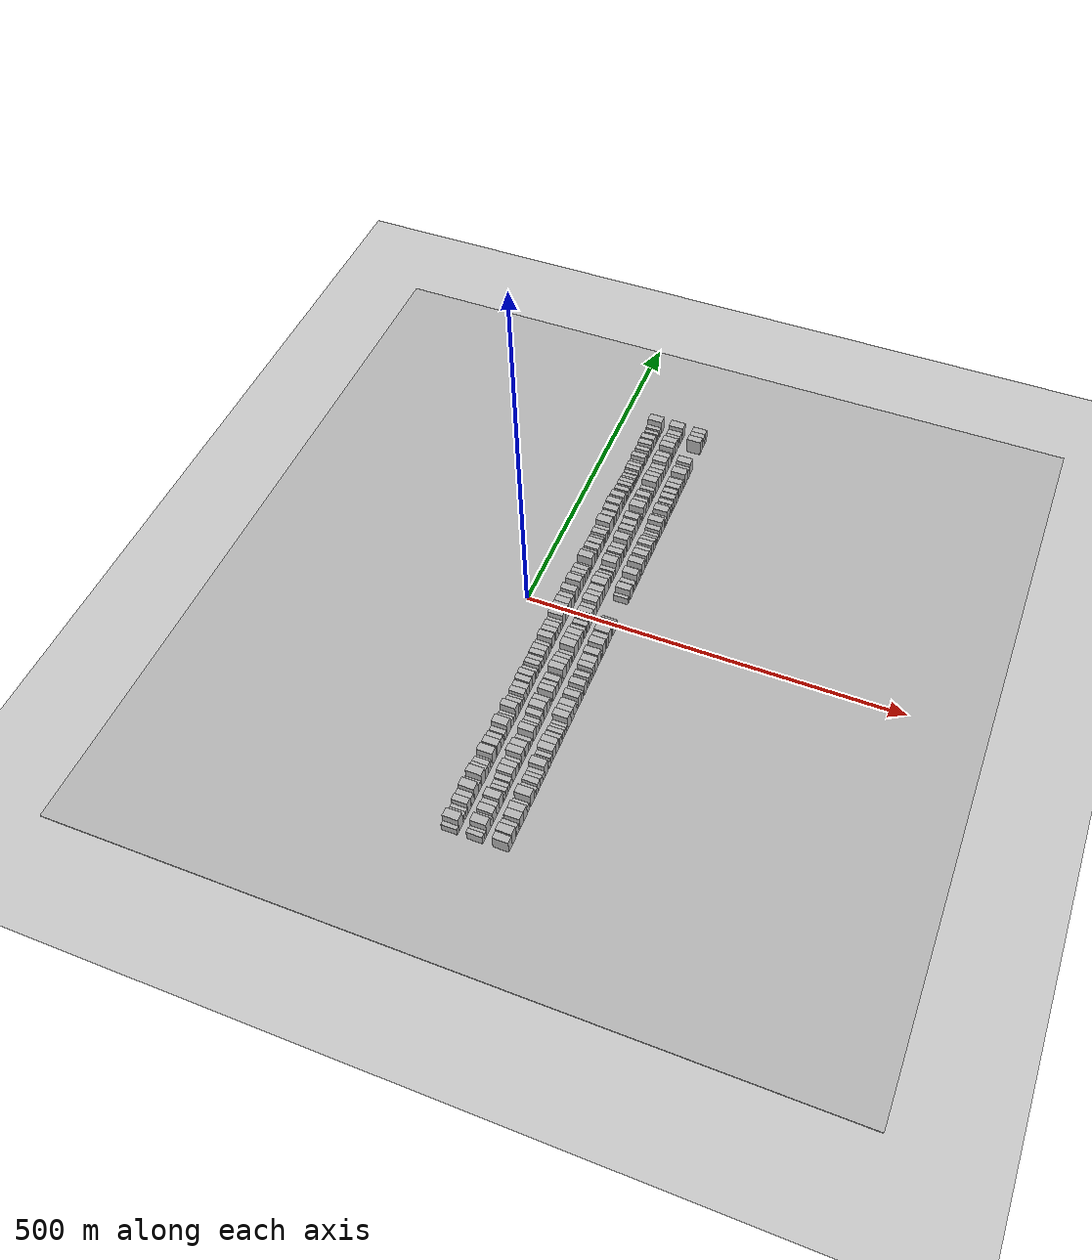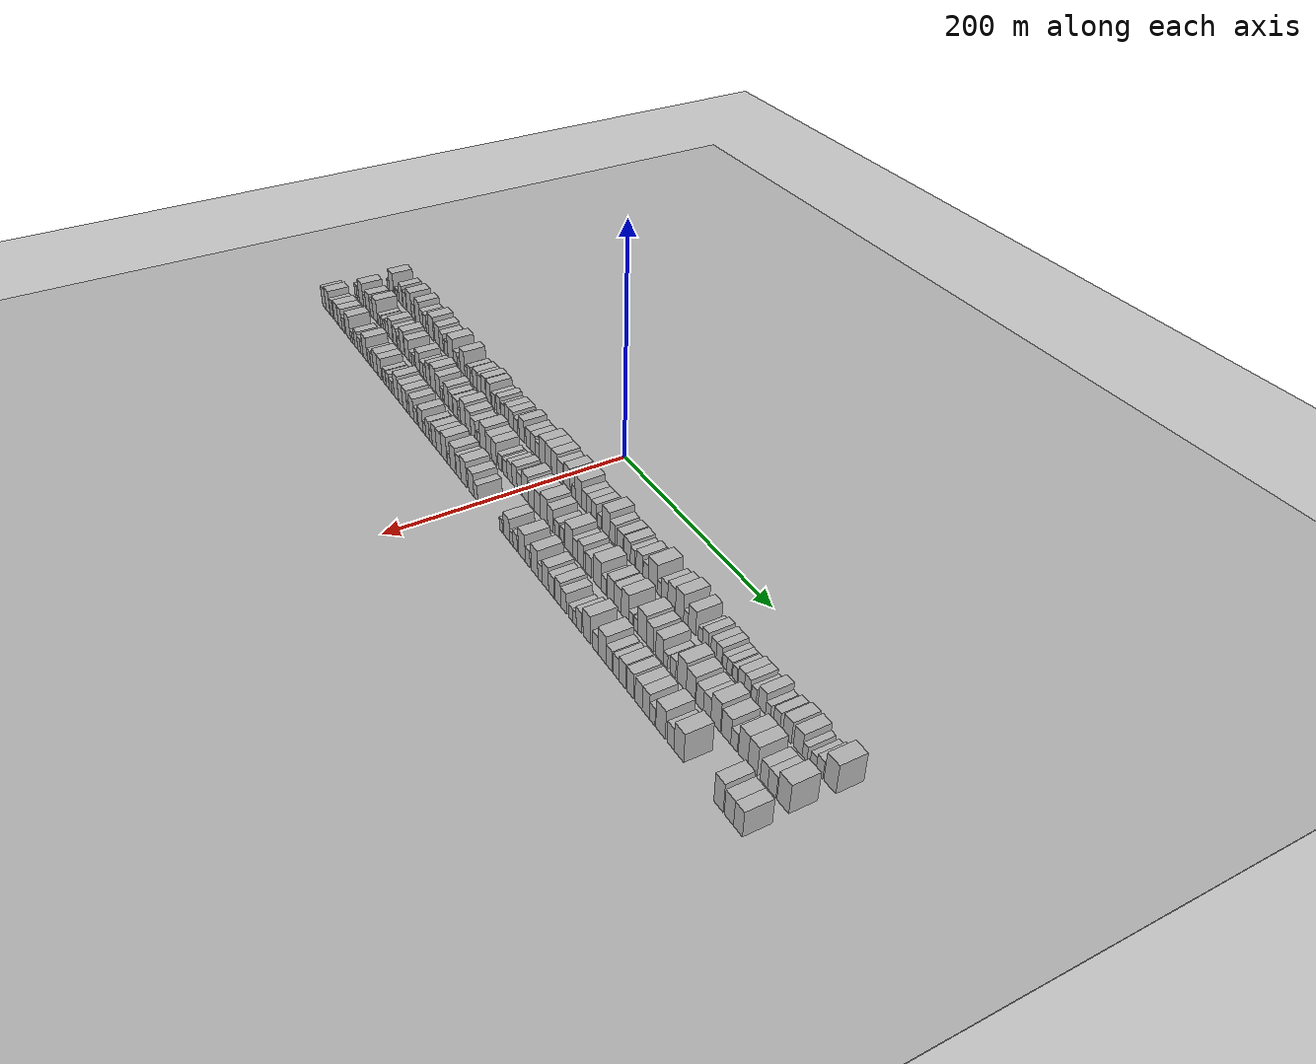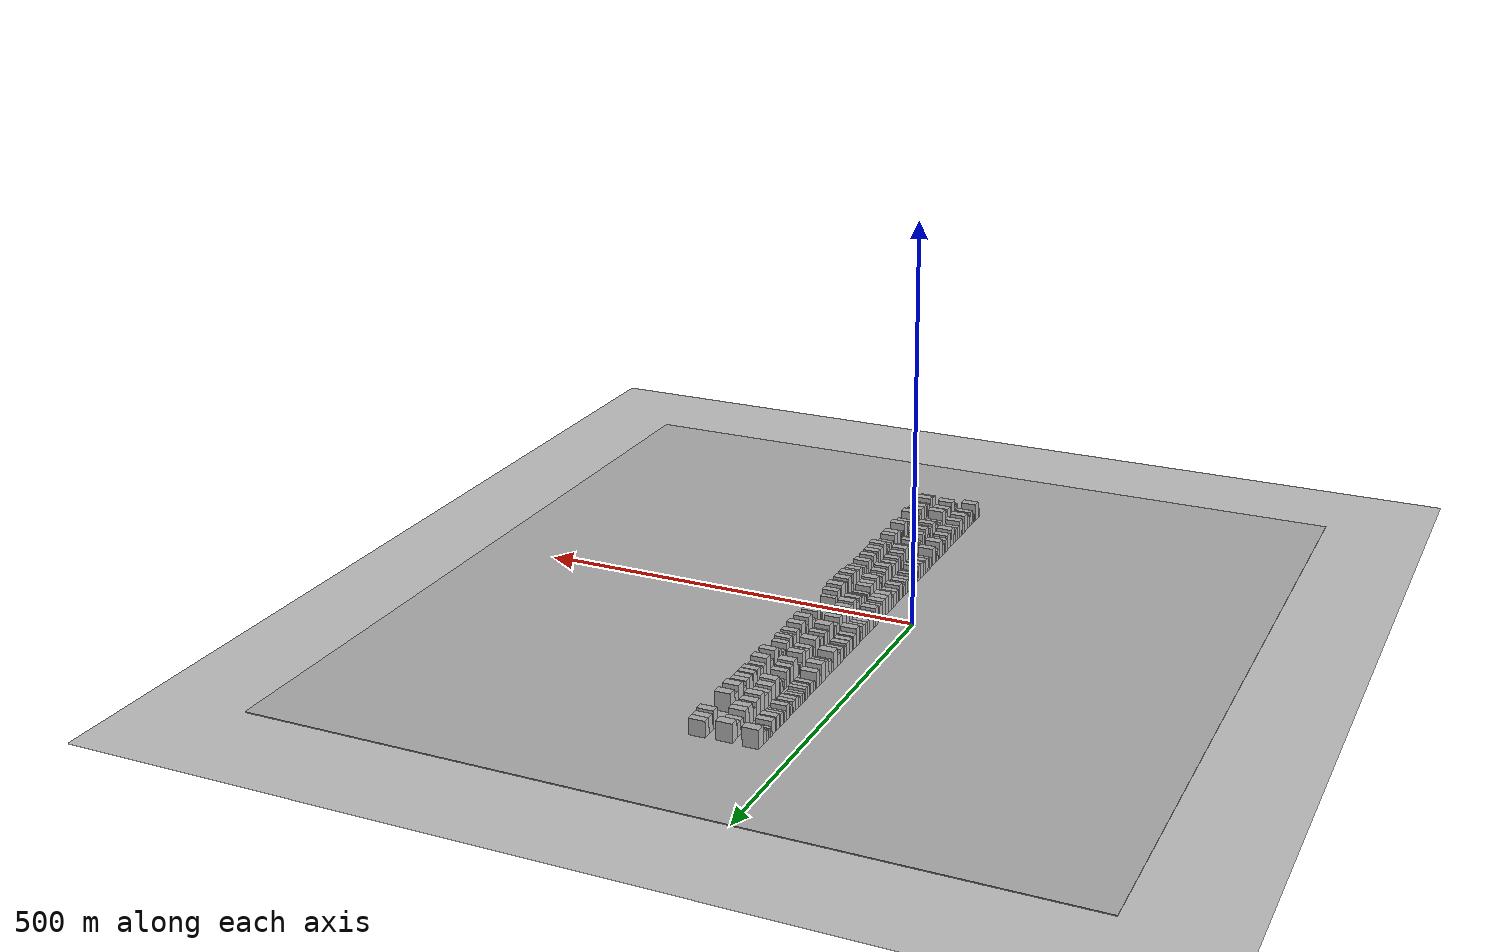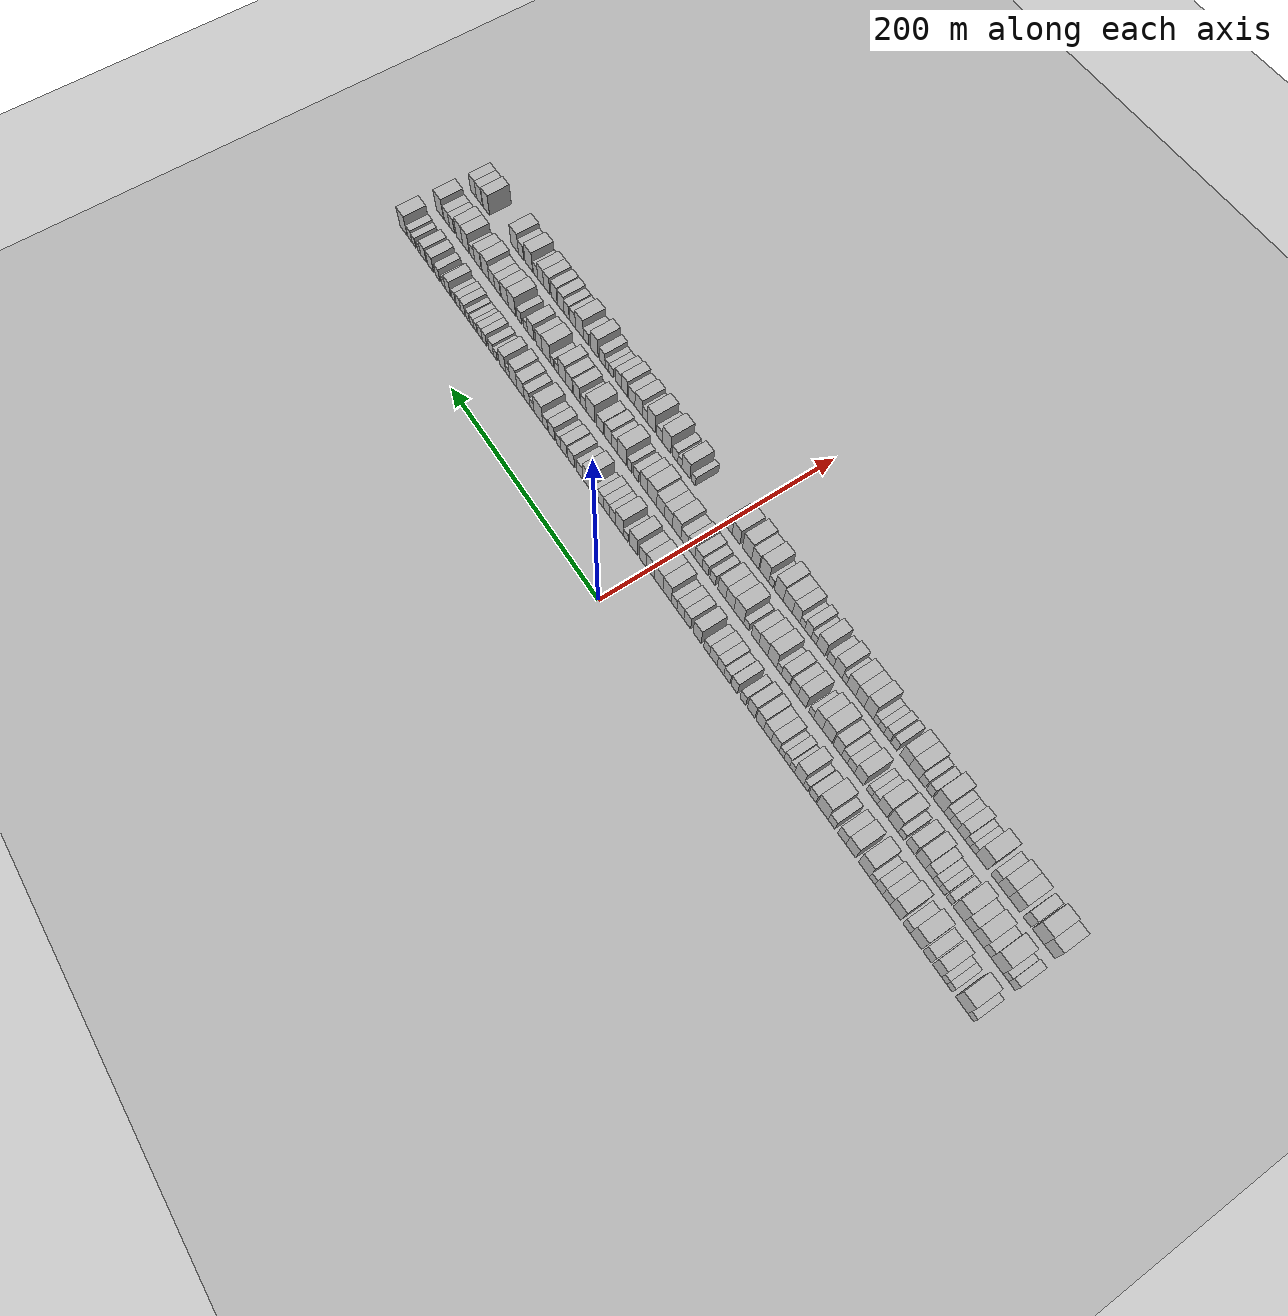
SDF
<?xml version="1.0" encoding="utf-8"?>

<sdf version="1.6">

   <world name="default">

      <gui fullscreen="0">

         <camera name="user_camera">

            <pose>-15 0 4.57585 0 0 0</pose>

            <view_controller>orbit</view_controller>

         </camera>

      </gui>

      <scene>

         <sky>

           <clouds>

             <speed>12</speed>

           </clouds>

         </sky>

         <ambient>0.4 0.4 0.4 1</ambient>

         <background>0.7 0.7 0.7 1</background>

         <shadows>1</shadows>

      </scene>

      <gravity>0 0 -9.8066</gravity>

      <magnetic_field>6e-06 2.3e-05 -4.2e-05</magnetic_field>

      <physics default="0" name="default_physics" type="ode">

         <ode>

            <solver>

               <type>quick</type>

               <iters>10</iters>

               <sor>1.0</sor>

               <use_dynamic_moi_rescaling>0</use_dynamic_moi_rescaling>

            </solver>

            <constraints>

               <cfm>0</cfm>

               <erp>0.2</erp>

               <contact_max_correcting_vel>100</contact_max_correcting_vel>

               <contact_surface_layer>0.001</contact_surface_layer>

            </constraints>

         </ode>

         <max_step_size>0.004</max_step_size>

         <real_time_factor>1</real_time_factor>

         <real_time_update_rate>250</real_time_update_rate>

      </physics>

      <light name="sun" type="directional">

         <cast_shadows>1</cast_shadows>

         <pose>0 0 10 0 0 0</pose>

         <diffuse>0.8 0.8 0.8 1</diffuse>

         <specular>0.2 0.2 0.2 1</specular>

         <attenuation>

            <range>1000</range>

            <constant>0.9</constant>

            <linear>0.01</linear>

            <quadratic>0.001</quadratic>

         </attenuation>

         <direction>-0.5 0.1 -0.9</direction>

      </light>

      <include>

         <name>ground_plane_1</name>

         <uri>model://HANNAS_ground_plane</uri>

         <pose>0 0 0  0 0 0</pose>

      </include>

      <include>

         <name>ground_plane_2</name>

         <uri>model://HANNAS_ground_plane</uri>

         <pose>100 0 0  0 0 0</pose>

      </include>

      <model name="building_1">

         <static>1</static>

         <pose frame="">50.0000 -345.2431 0 0.000000 0.000000 0.000000</pose>

         <link name="link">

            <pose frame="">0 0 6.00 0 0 0</pose>

            <collision name="collision">

               <geometry>

                  <box>

                     <size>20.0000 5.5138 12.0000</size>

                  </box>

               </geometry>

               <max_contacts>10</max_contacts>

               <surface>

                  <contact>

                     <ode/>

                  </contact>

                  <bounce/>

                  <friction>

                     <torsional>

                        <ode/>

                     </torsional>

                     <ode/>

                  </friction>

               </surface>

            </collision>

            <visual name="visual">

               <cast_shadows>0</cast_shadows>

               <geometry>

                  <box>

                     <size>20.0000 5.5138 12.0000</size>

                  </box>

               </geometry>

               <material>

                  <script>

                     <uri>model://HANNAS_wall/materials/scripts</uri>

                     <uri>model://HANNAS_wall/materials/textures</uri>

                     <name>vrc/HANNAS_wall</name>

                  </script>

               </material>

            </visual>

            <self_collide>0</self_collide>

            <enable_wind>0</enable_wind>

            <kinematic>0</kinematic>

         </link>

      </model>

      <model name="building_2">

         <static>1</static>

         <pose frame="">50.0000 -336.7843 0 0.000000 0.000000 0.000000</pose>

         <link name="link">

            <pose frame="">0 0 12.00 0 0 0</pose>

            <collision name="collision">

               <geometry>

                  <box>

                     <size>20.0000 11.4038 24.0000</size>

                  </box>

               </geometry>

               <max_contacts>10</max_contacts>

               <surface>

                  <contact>

                     <ode/>

                  </contact>

                  <bounce/>

                  <friction>

                     <torsional>

                        <ode/>

                     </torsional>

                     <ode/>

                  </friction>

               </surface>

            </collision>

            <visual name="visual">

               <cast_shadows>0</cast_shadows>

               <geometry>

                  <box>

                     <size>20.0000 11.4038 24.0000</size>

                  </box>

               </geometry>

               <material>

                  <script>

                     <uri>model://HANNAS_wall/materials/scripts</uri>

                     <uri>model://HANNAS_wall/materials/textures</uri>

                     <name>vrc/HANNAS_wall</name>

                  </script>

               </material>

            </visual>

            <self_collide>0</self_collide>

            <enable_wind>0</enable_wind>

            <kinematic>0</kinematic>

         </link>

      </model>

      <model name="building_3">

         <static>1</static>

         <pose frame="">50.0000 -325.4623 0 0.000000 0.000000 0.000000</pose>

         <link name="link">

            <pose frame="">0 0 6.00 0 0 0</pose>

            <collision name="collision">

               <geometry>

                  <box>

                     <size>20.0000 5.2402 12.0000</size>

                  </box>

               </geometry>

               <max_contacts>10</max_contacts>

               <surface>

                  <contact>

                     <ode/>

                  </contact>

                  <bounce/>

                  <friction>

                     <torsional>

                        <ode/>

                     </torsional>

                     <ode/>

                  </friction>

               </surface>

            </collision>

            <visual name="visual">

               <cast_shadows>0</cast_shadows>

               <geometry>

                  <box>

                     <size>20.0000 5.2402 12.0000</size>

                  </box>

               </geometry>

               <material>

                  <script>

                     <uri>model://HANNAS_wall/materials/scripts</uri>

                     <uri>model://HANNAS_wall/materials/textures</uri>

                     <name>vrc/HANNAS_wall</name>

                  </script>

               </material>

            </visual>

            <self_collide>0</self_collide>

            <enable_wind>0</enable_wind>

            <kinematic>0</kinematic>

         </link>

      </model>

      <model name="building_4">

         <static>1</static>

         <pose frame="">50.0000 -320.3732 0 0.000000 0.000000 0.000000</pose>

         <link name="link">

            <pose frame="">0 0 6.00 0 0 0</pose>

            <collision name="collision">

               <geometry>

                  <box>

                     <size>20.0000 4.9381 12.0000</size>

                  </box>

               </geometry>

               <max_contacts>10</max_contacts>

               <surface>

                  <contact>

                     <ode/>

                  </contact>

                  <bounce/>

                  <friction>

                     <torsional>

                        <ode/>

                     </torsional>

                     <ode/>

                  </friction>

               </surface>

            </collision>

            <visual name="visual">

               <cast_shadows>0</cast_shadows>

               <geometry>

                  <box>

                     <size>20.0000 4.9381 12.0000</size>

                  </box>

               </geometry>

               <material>

                  <script>

                     <uri>model://HANNAS_wall/materials/scripts</uri>

                     <uri>model://HANNAS_wall/materials/textures</uri>

                     <name>vrc/HANNAS_wall</name>

                  </script>

               </material>

            </visual>

            <self_collide>0</self_collide>

            <enable_wind>0</enable_wind>

            <kinematic>0</kinematic>

         </link>

      </model>

      <model name="building_5">

         <static>1</static>

         <pose frame="">50.0000 -313.5936 0 0.000000 0.000000 0.000000</pose>

         <link name="link">

            <pose frame="">0 0 10.50 0 0 0</pose>

            <collision name="collision">

               <geometry>

                  <box>

                     <size>20.0000 8.6210 21.0000</size>

                  </box>

               </geometry>

               <max_contacts>10</max_contacts>

               <surface>

                  <contact>

                     <ode/>

                  </contact>

                  <bounce/>

                  <friction>

                     <torsional>

                        <ode/>

                     </torsional>

                     <ode/>

                  </friction>

               </surface>

            </collision>

            <visual name="visual">

               <cast_shadows>0</cast_shadows>

               <geometry>

                  <box>

                     <size>20.0000 8.6210 21.0000</size>

                  </box>

               </geometry>

               <material>

                  <script>

                     <uri>model://HANNAS_wall/materials/scripts</uri>

                     <uri>model://HANNAS_wall/materials/textures</uri>

                     <name>vrc/HANNAS_wall</name>

                  </script>

               </material>

            </visual>

            <self_collide>0</self_collide>

            <enable_wind>0</enable_wind>

            <kinematic>0</kinematic>

         </link>

      </model>

      <model name="building_6">

         <static>1</static>

         <pose frame="">50.0000 -304.1750 0 0.000000 0.000000 0.000000</pose>

         <link name="link">

            <pose frame="">0 0 9.00 0 0 0</pose>

            <collision name="collision">

               <geometry>

                  <box>

                     <size>20.0000 8.2161 18.0000</size>

                  </box>

               </geometry>

               <max_contacts>10</max_contacts>

               <surface>

                  <contact>

                     <ode/>

                  </contact>

                  <bounce/>

                  <friction>

                     <torsional>

                        <ode/>

                     </torsional>

                     <ode/>

                  </friction>

               </surface>

            </collision>

            <visual name="visual">

               <cast_shadows>0</cast_shadows>

               <geometry>

                  <box>

                     <size>20.0000 8.2161 18.0000</size>

                  </box>

               </geometry>

               <material>

                  <script>

                     <uri>model://HANNAS_wall/materials/scripts</uri>

                     <uri>model://HANNAS_wall/materials/textures</uri>

                     <name>vrc/HANNAS_wall</name>

                  </script>

               </material>

            </visual>

            <self_collide>0</self_collide>

            <enable_wind>0</enable_wind>

            <kinematic>0</kinematic>

         </link>

      </model>

      <model name="building_7">

         <static>1</static>

         <pose frame="">50.0000 -293.4442 0 0.000000 0.000000 0.000000</pose>

         <link name="link">

            <pose frame="">0 0 12.00 0 0 0</pose>

            <collision name="collision">

               <geometry>

                  <box>

                     <size>20.0000 11.2455 24.0000</size>

                  </box>

               </geometry>

               <max_contacts>10</max_contacts>

               <surface>

                  <contact>

                     <ode/>

                  </contact>

                  <bounce/>

                  <friction>

                     <torsional>

                        <ode/>

                     </torsional>

                     <ode/>

                  </friction>

               </surface>

            </collision>

            <visual name="visual">

               <cast_shadows>0</cast_shadows>

               <geometry>

                  <box>

                     <size>20.0000 11.2455 24.0000</size>

                  </box>

               </geometry>

               <material>

                  <script>

                     <uri>model://HANNAS_wall/materials/scripts</uri>

                     <uri>model://HANNAS_wall/materials/textures</uri>

                     <name>vrc/HANNAS_wall</name>

                  </script>

               </material>

            </visual>

            <self_collide>0</self_collide>

            <enable_wind>0</enable_wind>

            <kinematic>0</kinematic>

         </link>

      </model>

      <model name="building_8">

         <static>1</static>

         <pose frame="">50.0000 -284.2073 0 0.000000 0.000000 0.000000</pose>

         <link name="link">

            <pose frame="">0 0 7.50 0 0 0</pose>

            <collision name="collision">

               <geometry>

                  <box>

                     <size>20.0000 7.2283 15.0000</size>

                  </box>

               </geometry>

               <max_contacts>10</max_contacts>

               <surface>

                  <contact>

                     <ode/>

                  </contact>

                  <bounce/>

                  <friction>

                     <torsional>

                        <ode/>

                     </torsional>

                     <ode/>

                  </friction>

               </surface>

            </collision>

            <visual name="visual">

               <cast_shadows>0</cast_shadows>

               <geometry>

                  <box>

                     <size>20.0000 7.2283 15.0000</size>

                  </box>

               </geometry>

               <material>

                  <script>

                     <uri>model://HANNAS_wall/materials/scripts</uri>

                     <uri>model://HANNAS_wall/materials/textures</uri>

                     <name>vrc/HANNAS_wall</name>

                  </script>

               </material>

            </visual>

            <self_collide>0</self_collide>

            <enable_wind>0</enable_wind>

            <kinematic>0</kinematic>

         </link>

      </model>

      <model name="building_9">

         <static>1</static>

         <pose frame="">50.0000 -273.3169 0 0.000000 0.000000 0.000000</pose>

         <link name="link">

            <pose frame="">0 0 12.00 0 0 0</pose>

            <collision name="collision">

               <geometry>

                  <box>

                     <size>20.0000 10.5524 24.0000</size>

                  </box>

               </geometry>

               <max_contacts>10</max_contacts>

               <surface>

                  <contact>

                     <ode/>

                  </contact>

                  <bounce/>

                  <friction>

                     <torsional>

                        <ode/>

                     </torsional>

                     <ode/>

                  </friction>

               </surface>

            </collision>

            <visual name="visual">

               <cast_shadows>0</cast_shadows>

               <geometry>

                  <box>

                     <size>20.0000 10.5524 24.0000</size>

                  </box>

               </geometry>

               <material>

                  <script>

                     <uri>model://HANNAS_wall/materials/scripts</uri>

                     <uri>model://HANNAS_wall/materials/textures</uri>

                     <name>vrc/HANNAS_wall</name>

                  </script>

               </material>

            </visual>

            <self_collide>0</self_collide>

            <enable_wind>0</enable_wind>

            <kinematic>0</kinematic>

         </link>

      </model>

      <model name="building_10">

         <static>1</static>

         <pose frame="">50.0000 -264.2243 0 0.000000 0.000000 0.000000</pose>

         <link name="link">

            <pose frame="">0 0 9.00 0 0 0</pose>

            <collision name="collision">

               <geometry>

                  <box>

                     <size>20.0000 7.6328 18.0000</size>

                  </box>

               </geometry>

               <max_contacts>10</max_contacts>

               <surface>

                  <contact>

                     <ode/>

                  </contact>

                  <bounce/>

                  <friction>

                     <torsional>

                        <ode/>

                     </torsional>

                     <ode/>

                  </friction>

               </surface>

            </collision>

            <visual name="visual">

               <cast_shadows>0</cast_shadows>

               <geometry>

                  <box>

                     <size>20.0000 7.6328 18.0000</size>

                  </box>

               </geometry>

               <material>

                  <script>

                     <uri>model://HANNAS_wall/materials/scripts</uri>

                     <uri>model://HANNAS_wall/materials/textures</uri>

                     <name>vrc/HANNAS_wall</name>

                  </script>

               </material>

            </visual>

            <self_collide>0</self_collide>

            <enable_wind>0</enable_wind>

            <kinematic>0</kinematic>

         </link>

      </model>

      <model name="building_11">

         <static>1</static>

         <pose frame="">50.0000 -256.8023 0 0.000000 0.000000 0.000000</pose>

         <link name="link">

            <pose frame="">0 0 9.00 0 0 0</pose>

            <collision name="collision">

               <geometry>

                  <box>

                     <size>20.0000 7.2111 18.0000</size>

                  </box>

               </geometry>

               <max_contacts>10</max_contacts>

               <surface>

                  <contact>

                     <ode/>

                  </contact>

                  <bounce/>

                  <friction>

                     <torsional>

                        <ode/>

                     </torsional>

                     <ode/>

                  </friction>

               </surface>

            </collision>

            <visual name="visual">

               <cast_shadows>0</cast_shadows>

               <geometry>

                  <box>

                     <size>20.0000 7.2111 18.0000</size>

                  </box>

               </geometry>

               <material>

                  <script>

                     <uri>model://HANNAS_wall/materials/scripts</uri>

                     <uri>model://HANNAS_wall/materials/textures</uri>

                     <name>vrc/HANNAS_wall</name>

                  </script>

               </material>

            </visual>

            <self_collide>0</self_collide>

            <enable_wind>0</enable_wind>

            <kinematic>0</kinematic>

         </link>

      </model>

      <model name="building_12">

         <static>1</static>

         <pose frame="">50.0000 -250.4106 0 0.000000 0.000000 0.000000</pose>

         <link name="link">

            <pose frame="">0 0 6.00 0 0 0</pose>

            <collision name="collision">

               <geometry>

                  <box>

                     <size>20.0000 5.5723 12.0000</size>

                  </box>

               </geometry>

               <max_contacts>10</max_contacts>

               <surface>

                  <contact>

                     <ode/>

                  </contact>

                  <bounce/>

                  <friction>

                     <torsional>

                        <ode/>

                     </torsional>

                     <ode/>

                  </friction>

               </surface>

            </collision>

            <visual name="visual">

               <cast_shadows>0</cast_shadows>

               <geometry>

                  <box>

                     <size>20.0000 5.5723 12.0000</size>

                  </box>

               </geometry>

               <material>

                  <script>

                     <uri>model://HANNAS_wall/materials/scripts</uri>

                     <uri>model://HANNAS_wall/materials/textures</uri>

                     <name>vrc/HANNAS_wall</name>

                  </script>

               </material>

            </visual>

            <self_collide>0</self_collide>

            <enable_wind>0</enable_wind>

            <kinematic>0</kinematic>

         </link>

      </model>

      <model name="building_13">

         <static>1</static>

         <pose frame="">50.0000 -242.0929 0 0.000000 0.000000 0.000000</pose>

         <link name="link">

            <pose frame="">0 0 12.00 0 0 0</pose>

            <collision name="collision">

               <geometry>

                  <box>

                     <size>20.0000 11.0631 24.0000</size>

                  </box>

               </geometry>

               <max_contacts>10</max_contacts>

               <surface>

                  <contact>

                     <ode/>

                  </contact>

                  <bounce/>

                  <friction>

                     <torsional>

                        <ode/>

                     </torsional>

                     <ode/>

                  </friction>

               </surface>

            </collision>

            <visual name="visual">

               <cast_shadows>0</cast_shadows>

               <geometry>

                  <box>

                     <size>20.0000 11.0631 24.0000</size>

                  </box>

               </geometry>

               <material>

                  <script>

                     <uri>model://HANNAS_wall/materials/scripts</uri>

                     <uri>model://HANNAS_wall/materials/textures</uri>

                     <name>vrc/HANNAS_wall</name>

                  </script>

               </material>

            </visual>

            <self_collide>0</self_collide>

            <enable_wind>0</enable_wind>

            <kinematic>0</kinematic>

         </link>

      </model>

      <model name="building_14">

         <static>1</static>

         <pose frame="">50.0000 -228.4945 0 0.000000 0.000000 0.000000</pose>

         <link name="link">

            <pose frame="">0 0 10.50 0 0 0</pose>

            <collision name="collision">

               <geometry>

                  <box>

                     <size>20.0000 10.1337 21.0000</size>

                  </box>

               </geometry>

               <max_contacts>10</max_contacts>

               <surface>

                  <contact>

                     <ode/>

                  </contact>

                  <bounce/>

                  <friction>

                     <torsional>

                        <ode/>

                     </torsional>

                     <ode/>

                  </friction>

               </surface>

            </collision>

            <visual name="visual">

               <cast_shadows>0</cast_shadows>

               <geometry>

                  <box>

                     <size>20.0000 10.1337 21.0000</size>

                  </box>

               </geometry>

               <material>

                  <script>

                     <uri>model://HANNAS_wall/materials/scripts</uri>

                     <uri>model://HANNAS_wall/materials/textures</uri>

                     <name>vrc/HANNAS_wall</name>

                  </script>

               </material>

            </visual>

            <self_collide>0</self_collide>

            <enable_wind>0</enable_wind>

            <kinematic>0</kinematic>

         </link>

      </model>

      <model name="building_15">

         <static>1</static>

         <pose frame="">50.0000 -219.2789 0 0.000000 0.000000 0.000000</pose>

         <link name="link">

            <pose frame="">0 0 9.00 0 0 0</pose>

            <collision name="collision">

               <geometry>

                  <box>

                     <size>20.0000 8.2975 18.0000</size>

                  </box>

               </geometry>

               <max_contacts>10</max_contacts>

               <surface>

                  <contact>

                     <ode/>

                  </contact>

                  <bounce/>

                  <friction>

                     <torsional>

                        <ode/>

                     </torsional>

                     <ode/>

                  </friction>

               </surface>

            </collision>

            <visual name="visual">

               <cast_shadows>0</cast_shadows>

               <geometry>

                  <box>

                     <size>20.0000 8.2975 18.0000</size>

                  </box>

               </geometry>

               <material>

                  <script>

                     <uri>model://HANNAS_wall/materials/scripts</uri>

                     <uri>model://HANNAS_wall/materials/textures</uri>

                     <name>vrc/HANNAS_wall</name>

                  </script>

               </material>

            </visual>

            <self_collide>0</self_collide>

            <enable_wind>0</enable_wind>

            <kinematic>0</kinematic>

         </link>

      </model>

      <model name="building_16">

         <static>1</static>

         <pose frame="">50.0000 -208.5931 0 0.000000 0.000000 0.000000</pose>

         <link name="link">

            <pose frame="">0 0 7.50 0 0 0</pose>

            <collision name="collision">

               <geometry>

                  <box>

                     <size>20.0000 7.0739 15.0000</size>

                  </box>

               </geometry>

               <max_contacts>10</max_contacts>

               <surface>

                  <contact>

                     <ode/>

                  </contact>

                  <bounce/>

                  <friction>

                     <torsional>

                        <ode/>

                     </torsional>

                     <ode/>

                  </friction>

               </surface>

            </collision>

            <visual name="visual">

               <cast_shadows>0</cast_shadows>

               <geometry>

                  <box>

                     <size>20.0000 7.0739 15.0000</size>

                  </box>

               </geometry>

               <material>

                  <script>

                     <uri>model://HANNAS_wall/materials/scripts</uri>

                     <uri>model://HANNAS_wall/materials/textures</uri>

                     <name>vrc/HANNAS_wall</name>

                  </script>

               </material>

            </visual>

            <self_collide>0</self_collide>

            <enable_wind>0</enable_wind>

            <kinematic>0</kinematic>

         </link>

      </model>

      <model name="building_17">

         <static>1</static>

         <pose frame="">50.0000 -199.1446 0 0.000000 0.000000 0.000000</pose>

         <link name="link">

            <pose frame="">0 0 12.00 0 0 0</pose>

            <collision name="collision">

               <geometry>

                  <box>

                     <size>20.0000 11.8231 24.0000</size>

                  </box>

               </geometry>

               <max_contacts>10</max_contacts>

               <surface>

                  <contact>

                     <ode/>

                  </contact>

                  <bounce/>

                  <friction>

                     <torsional>

                        <ode/>

                     </torsional>

                     <ode/>

                  </friction>

               </surface>

            </collision>

            <visual name="visual">

               <cast_shadows>0</cast_shadows>

               <geometry>

                  <box>

                     <size>20.0000 11.8231 24.0000</size>

                  </box>

               </geometry>

               <material>

                  <script>

                     <uri>model://HANNAS_wall/materials/scripts</uri>

                     <uri>model://HANNAS_wall/materials/textures</uri>

                     <name>vrc/HANNAS_wall</name>

                  </script>

               </material>

            </visual>

            <self_collide>0</self_collide>

            <enable_wind>0</enable_wind>

            <kinematic>0</kinematic>

         </link>

      </model>

      <model name="building_18">

         <static>1</static>

         <pose frame="">50.0000 -188.5425 0 0.000000 0.000000 0.000000</pose>

         <link name="link">

            <pose frame="">0 0 7.50 0 0 0</pose>

            <collision name="collision">

               <geometry>

                  <box>

                     <size>20.0000 7.3811 15.0000</size>

                  </box>

               </geometry>

               <max_contacts>10</max_contacts>

               <surface>

                  <contact>

                     <ode/>

                  </contact>

                  <bounce/>

                  <friction>

                     <torsional>

                        <ode/>

                     </torsional>

                     <ode/>

                  </friction>

               </surface>

            </collision>

            <visual name="visual">

               <cast_shadows>0</cast_shadows>

               <geometry>

                  <box>

                     <size>20.0000 7.3811 15.0000</size>

                  </box>

               </geometry>

               <material>

                  <script>

                     <uri>model://HANNAS_wall/materials/scripts</uri>

                     <uri>model://HANNAS_wall/materials/textures</uri>

                     <name>vrc/HANNAS_wall</name>

                  </script>

               </material>

            </visual>

            <self_collide>0</self_collide>

            <enable_wind>0</enable_wind>

            <kinematic>0</kinematic>

         </link>

      </model>

      <model name="building_19">

         <static>1</static>

         <pose frame="">50.0000 -181.4019 0 0.000000 0.000000 0.000000</pose>

         <link name="link">

            <pose frame="">0 0 6.00 0 0 0</pose>

            <collision name="collision">

               <geometry>

                  <box>

                     <size>20.0000 4.9000 12.0000</size>

                  </box>

               </geometry>

               <max_contacts>10</max_contacts>

               <surface>

                  <contact>

                     <ode/>

                  </contact>

                  <bounce/>

                  <friction>

                     <torsional>

                        <ode/>

                     </torsional>

                     <ode/>

                  </friction>

               </surface>

            </collision>

            <visual name="visual">

               <cast_shadows>0</cast_shadows>

               <geometry>

                  <box>

                     <size>20.0000 4.9000 12.0000</size>

                  </box>

               </geometry>

               <material>

                  <script>

                     <uri>model://HANNAS_wall/materials/scripts</uri>

                     <uri>model://HANNAS_wall/materials/textures</uri>

                     <name>vrc/HANNAS_wall</name>

                  </script>

               </material>

            </visual>

            <self_collide>0</self_collide>

            <enable_wind>0</enable_wind>

            <kinematic>0</kinematic>

         </link>

      </model>

      <model name="building_20">

         <static>1</static>

         <pose frame="">50.0000 -174.1154 0 0.000000 0.000000 0.000000</pose>

         <link name="link">

            <pose frame="">0 0 12.00 0 0 0</pose>

            <collision name="collision">

               <geometry>

                  <box>

                     <size>20.0000 9.6731 24.0000</size>

                  </box>

               </geometry>

               <max_contacts>10</max_contacts>

               <surface>

                  <contact>

                     <ode/>

                  </contact>

                  <bounce/>

                  <friction>

                     <torsional>

                        <ode/>

                     </torsional>

                     <ode/>

                  </friction>

               </surface>

            </collision>

            <visual name="visual">

               <cast_shadows>0</cast_shadows>

               <geometry>

                  <box>

                     <size>20.0000 9.6731 24.0000</size>

                  </box>

               </geometry>

               <material>

                  <script>

                     <uri>model://HANNAS_wall/materials/scripts</uri>

                     <uri>model://HANNAS_wall/materials/textures</uri>

                     <name>vrc/HANNAS_wall</name>

                  </script>

               </material>

            </visual>

            <self_collide>0</self_collide>

            <enable_wind>0</enable_wind>

            <kinematic>0</kinematic>

         </link>

      </model>

      <model name="building_21">

         <static>1</static>

         <pose frame="">50.0000 -166.7854 0 0.000000 0.000000 0.000000</pose>

         <link name="link">

            <pose frame="">0 0 6.00 0 0 0</pose>

            <collision name="collision">

               <geometry>

                  <box>

                     <size>20.0000 4.9869 12.0000</size>

                  </box>

               </geometry>

               <max_contacts>10</max_contacts>

               <surface>

                  <contact>

                     <ode/>

                  </contact>

                  <bounce/>

                  <friction>

                     <torsional>

                        <ode/>

                     </torsional>

                     <ode/>

                  </friction>

               </surface>

            </collision>

            <visual name="visual">

               <cast_shadows>0</cast_shadows>

               <geometry>

                  <box>

                     <size>20.0000 4.9869 12.0000</size>

                  </box>

               </geometry>

               <material>

                  <script>

                     <uri>model://HANNAS_wall/materials/scripts</uri>

                     <uri>model://HANNAS_wall/materials/textures</uri>

                     <name>vrc/HANNAS_wall</name>

                  </script>

               </material>

            </visual>

            <self_collide>0</self_collide>

            <enable_wind>0</enable_wind>

            <kinematic>0</kinematic>

         </link>

      </model>

      <model name="building_22">

         <static>1</static>

         <pose frame="">50.0000 -161.1091 0 0.000000 0.000000 0.000000</pose>

         <link name="link">

            <pose frame="">0 0 7.50 0 0 0</pose>

            <collision name="collision">

               <geometry>

                  <box>

                     <size>20.0000 6.3658 15.0000</size>

                  </box>

               </geometry>

               <max_contacts>10</max_contacts>

               <surface>

                  <contact>

                     <ode/>

                  </contact>

                  <bounce/>

                  <friction>

                     <torsional>

                        <ode/>

                     </torsional>

                     <ode/>

                  </friction>

               </surface>

            </collision>

            <visual name="visual">

               <cast_shadows>0</cast_shadows>

               <geometry>

                  <box>

                     <size>20.0000 6.3658 15.0000</size>

                  </box>

               </geometry>

               <material>

                  <script>

                     <uri>model://HANNAS_wall/materials/scripts</uri>

                     <uri>model://HANNAS_wall/materials/textures</uri>

                     <name>vrc/HANNAS_wall</name>

                  </script>

               </material>

            </visual>

            <self_collide>0</self_collide>

            <enable_wind>0</enable_wind>

            <kinematic>0</kinematic>

         </link>

      </model>

      <model name="building_23">

         <static>1</static>

         <pose frame="">50.0000 -155.2915 0 0.000000 0.000000 0.000000</pose>

         <link name="link">

            <pose frame="">0 0 6.00 0 0 0</pose>

            <collision name="collision">

               <geometry>

                  <box>

                     <size>20.0000 5.2694 12.0000</size>

                  </box>

               </geometry>

               <max_contacts>10</max_contacts>

               <surface>

                  <contact>

                     <ode/>

                  </contact>

                  <bounce/>

                  <friction>

                     <torsional>

                        <ode/>

                     </torsional>

                     <ode/>

                  </friction>

               </surface>

            </collision>

            <visual name="visual">

               <cast_shadows>0</cast_shadows>

               <geometry>

                  <box>

                     <size>20.0000 5.2694 12.0000</size>

                  </box>

               </geometry>

               <material>

                  <script>

                     <uri>model://HANNAS_wall/materials/scripts</uri>

                     <uri>model://HANNAS_wall/materials/textures</uri>

                     <name>vrc/HANNAS_wall</name>

                  </script>

               </material>

            </visual>

            <self_collide>0</self_collide>

            <enable_wind>0</enable_wind>

            <kinematic>0</kinematic>

         </link>

      </model>

      <model name="building_24">

         <static>1</static>

         <pose frame="">50.0000 -148.2918 0 0.000000 0.000000 0.000000</pose>

         <link name="link">

            <pose frame="">0 0 9.00 0 0 0</pose>

            <collision name="collision">

               <geometry>

                  <box>

                     <size>20.0000 8.7299 18.0000</size>

                  </box>

               </geometry>

               <max_contacts>10</max_contacts>

               <surface>

                  <contact>

                     <ode/>

                  </contact>

                  <bounce/>

                  <friction>

                     <torsional>

                        <ode/>

                     </torsional>

                     <ode/>

                  </friction>

               </surface>

            </collision>

            <visual name="visual">

               <cast_shadows>0</cast_shadows>

               <geometry>

                  <box>

                     <size>20.0000 8.7299 18.0000</size>

                  </box>

               </geometry>

               <material>

                  <script>

                     <uri>model://HANNAS_wall/materials/scripts</uri>

                     <uri>model://HANNAS_wall/materials/textures</uri>

                     <name>vrc/HANNAS_wall</name>

                  </script>

               </material>

            </visual>

            <self_collide>0</self_collide>

            <enable_wind>0</enable_wind>

            <kinematic>0</kinematic>

         </link>

      </model>

      <model name="building_25">

         <static>1</static>

         <pose frame="">50.0000 -139.7136 0 0.000000 0.000000 0.000000</pose>

         <link name="link">

            <pose frame="">0 0 9.00 0 0 0</pose>

            <collision name="collision">

               <geometry>

                  <box>

                     <size>20.0000 8.4266 18.0000</size>

                  </box>

               </geometry>

               <max_contacts>10</max_contacts>

               <surface>

                  <contact>

                     <ode/>

                  </contact>

                  <bounce/>

                  <friction>

                     <torsional>

                        <ode/>

                     </torsional>

                     <ode/>

                  </friction>

               </surface>

            </collision>

            <visual name="visual">

               <cast_shadows>0</cast_shadows>

               <geometry>

                  <box>

                     <size>20.0000 8.4266 18.0000</size>

                  </box>

               </geometry>

               <material>

                  <script>

                     <uri>model://HANNAS_wall/materials/scripts</uri>

                     <uri>model://HANNAS_wall/materials/textures</uri>

                     <name>vrc/HANNAS_wall</name>

                  </script>

               </material>

            </visual>

            <self_collide>0</self_collide>

            <enable_wind>0</enable_wind>

            <kinematic>0</kinematic>

         </link>

      </model>

      <model name="building_26">

         <static>1</static>

         <pose frame="">50.0000 -131.1972 0 0.000000 0.000000 0.000000</pose>

         <link name="link">

            <pose frame="">0 0 10.50 0 0 0</pose>

            <collision name="collision">

               <geometry>

                  <box>

                     <size>20.0000 8.6061 21.0000</size>

                  </box>

               </geometry>

               <max_contacts>10</max_contacts>

               <surface>

                  <contact>

                     <ode/>

                  </contact>

                  <bounce/>

                  <friction>

                     <torsional>

                        <ode/>

                     </torsional>

                     <ode/>

                  </friction>

               </surface>

            </collision>

            <visual name="visual">

               <cast_shadows>0</cast_shadows>

               <geometry>

                  <box>

                     <size>20.0000 8.6061 21.0000</size>

                  </box>

               </geometry>

               <material>

                  <script>

                     <uri>model://HANNAS_wall/materials/scripts</uri>

                     <uri>model://HANNAS_wall/materials/textures</uri>

                     <name>vrc/HANNAS_wall</name>

                  </script>

               </material>

            </visual>

            <self_collide>0</self_collide>

            <enable_wind>0</enable_wind>

            <kinematic>0</kinematic>

         </link>

      </model>

      <model name="building_27">

         <static>1</static>

         <pose frame="">50.0000 -121.6702 0 0.000000 0.000000 0.000000</pose>

         <link name="link">

            <pose frame="">0 0 10.50 0 0 0</pose>

            <collision name="collision">

               <geometry>

                  <box>

                     <size>20.0000 8.4480 21.0000</size>

                  </box>

               </geometry>

               <max_contacts>10</max_contacts>

               <surface>

                  <contact>

                     <ode/>

                  </contact>

                  <bounce/>

                  <friction>

                     <torsional>

                        <ode/>

                     </torsional>

                     <ode/>

                  </friction>

               </surface>

            </collision>

            <visual name="visual">

               <cast_shadows>0</cast_shadows>

               <geometry>

                  <box>

                     <size>20.0000 8.4480 21.0000</size>

                  </box>

               </geometry>

               <material>

                  <script>

                     <uri>model://HANNAS_wall/materials/scripts</uri>

                     <uri>model://HANNAS_wall/materials/textures</uri>

                     <name>vrc/HANNAS_wall</name>

                  </script>

               </material>

            </visual>

            <self_collide>0</self_collide>

            <enable_wind>0</enable_wind>

            <kinematic>0</kinematic>

         </link>

      </model>

      <model name="building_28">

         <static>1</static>

         <pose frame="">50.0000 -112.2499 0 0.000000 0.000000 0.000000</pose>

         <link name="link">

            <pose frame="">0 0 7.50 0 0 0</pose>

            <collision name="collision">

               <geometry>

                  <box>

                     <size>20.0000 6.3926 15.0000</size>

                  </box>

               </geometry>

               <max_contacts>10</max_contacts>

               <surface>

                  <contact>

                     <ode/>

                  </contact>

                  <bounce/>

                  <friction>

                     <torsional>

                        <ode/>

                     </torsional>

                     <ode/>

                  </friction>

               </surface>

            </collision>

            <visual name="visual">

               <cast_shadows>0</cast_shadows>

               <geometry>

                  <box>

                     <size>20.0000 6.3926 15.0000</size>

                  </box>

               </geometry>

               <material>

                  <script>

                     <uri>model://HANNAS_wall/materials/scripts</uri>

                     <uri>model://HANNAS_wall/materials/textures</uri>

                     <name>vrc/HANNAS_wall</name>

                  </script>

               </material>

            </visual>

            <self_collide>0</self_collide>

            <enable_wind>0</enable_wind>

            <kinematic>0</kinematic>

         </link>

      </model>

      <model name="building_29">

         <static>1</static>

         <pose frame="">50.0000 -102.4065 0 0.000000 0.000000 0.000000</pose>

         <link name="link">

            <pose frame="">0 0 9.00 0 0 0</pose>

            <collision name="collision">

               <geometry>

                  <box>

                     <size>20.0000 7.2943 18.0000</size>

                  </box>

               </geometry>

               <max_contacts>10</max_contacts>

               <surface>

                  <contact>

                     <ode/>

                  </contact>

                  <bounce/>

                  <friction>

                     <torsional>

                        <ode/>

                     </torsional>

                     <ode/>

                  </friction>

               </surface>

            </collision>

            <visual name="visual">

               <cast_shadows>0</cast_shadows>

               <geometry>

                  <box>

                     <size>20.0000 7.2943 18.0000</size>

                  </box>

               </geometry>

               <material>

                  <script>

                     <uri>model://HANNAS_wall/materials/scripts</uri>

                     <uri>model://HANNAS_wall/materials/textures</uri>

                     <name>vrc/HANNAS_wall</name>

                  </script>

               </material>

            </visual>

            <self_collide>0</self_collide>

            <enable_wind>0</enable_wind>

            <kinematic>0</kinematic>

         </link>

      </model>

      <model name="building_30">

         <static>1</static>

         <pose frame="">50.0000 -94.1300 0 0.000000 0.000000 0.000000</pose>

         <link name="link">

            <pose frame="">0 0 7.50 0 0 0</pose>

            <collision name="collision">

               <geometry>

                  <box>

                     <size>20.0000 7.2586 15.0000</size>

                  </box>

               </geometry>

               <max_contacts>10</max_contacts>

               <surface>

                  <contact>

                     <ode/>

                  </contact>

                  <bounce/>

                  <friction>

                     <torsional>

                        <ode/>

                     </torsional>

                     <ode/>

                  </friction>

               </surface>

            </collision>

            <visual name="visual">

               <cast_shadows>0</cast_shadows>

               <geometry>

                  <box>

                     <size>20.0000 7.2586 15.0000</size>

                  </box>

               </geometry>

               <material>

                  <script>

                     <uri>model://HANNAS_wall/materials/scripts</uri>

                     <uri>model://HANNAS_wall/materials/textures</uri>

                     <name>vrc/HANNAS_wall</name>

                  </script>

               </material>

            </visual>

            <self_collide>0</self_collide>

            <enable_wind>0</enable_wind>

            <kinematic>0</kinematic>

         </link>

      </model>

      <model name="building_31">

         <static>1</static>

         <pose frame="">50.0000 -86.5583 0 0.000000 0.000000 0.000000</pose>

         <link name="link">

            <pose frame="">0 0 9.00 0 0 0</pose>

            <collision name="collision">

               <geometry>

                  <box>

                     <size>20.0000 7.8849 18.0000</size>

                  </box>

               </geometry>

               <max_contacts>10</max_contacts>

               <surface>

                  <contact>

                     <ode/>

                  </contact>

                  <bounce/>

                  <friction>

                     <torsional>

                        <ode/>

                     </torsional>

                     <ode/>

                  </friction>

               </surface>

            </collision>

            <visual name="visual">

               <cast_shadows>0</cast_shadows>

               <geometry>

                  <box>

                     <size>20.0000 7.8849 18.0000</size>

                  </box>

               </geometry>

               <material>

                  <script>

                     <uri>model://HANNAS_wall/materials/scripts</uri>

                     <uri>model://HANNAS_wall/materials/textures</uri>

                     <name>vrc/HANNAS_wall</name>

                  </script>

               </material>

            </visual>

            <self_collide>0</self_collide>

            <enable_wind>0</enable_wind>

            <kinematic>0</kinematic>

         </link>

      </model>

      <model name="building_32">

         <static>1</static>

         <pose frame="">50.0000 -78.3560 0 0.000000 0.000000 0.000000</pose>

         <link name="link">

            <pose frame="">0 0 9.00 0 0 0</pose>

            <collision name="collision">

               <geometry>

                  <box>

                     <size>20.0000 8.5198 18.0000</size>

                  </box>

               </geometry>

               <max_contacts>10</max_contacts>

               <surface>

                  <contact>

                     <ode/>

                  </contact>

                  <bounce/>

                  <friction>

                     <torsional>

                        <ode/>

                     </torsional>

                     <ode/>

                  </friction>

               </surface>

            </collision>

            <visual name="visual">

               <cast_shadows>0</cast_shadows>

               <geometry>

                  <box>

                     <size>20.0000 8.5198 18.0000</size>

                  </box>

               </geometry>

               <material>

                  <script>

                     <uri>model://HANNAS_wall/materials/scripts</uri>

                     <uri>model://HANNAS_wall/materials/textures</uri>

                     <name>vrc/HANNAS_wall</name>

                  </script>

               </material>

            </visual>

            <self_collide>0</self_collide>

            <enable_wind>0</enable_wind>

            <kinematic>0</kinematic>

         </link>

      </model>

      <model name="building_33">

         <static>1</static>

         <pose frame="">50.0000 -70.5509 0 0.000000 0.000000 0.000000</pose>

         <link name="link">

            <pose frame="">0 0 7.50 0 0 0</pose>

            <collision name="collision">

               <geometry>

                  <box>

                     <size>20.0000 7.0905 15.0000</size>

                  </box>

               </geometry>

               <max_contacts>10</max_contacts>

               <surface>

                  <contact>

                     <ode/>

                  </contact>

                  <bounce/>

                  <friction>

                     <torsional>

                        <ode/>

                     </torsional>

                     <ode/>

                  </friction>

               </surface>

            </collision>

            <visual name="visual">

               <cast_shadows>0</cast_shadows>

               <geometry>

                  <box>

                     <size>20.0000 7.0905 15.0000</size>

                  </box>

               </geometry>

               <material>

                  <script>

                     <uri>model://HANNAS_wall/materials/scripts</uri>

                     <uri>model://HANNAS_wall/materials/textures</uri>

                     <name>vrc/HANNAS_wall</name>

                  </script>

               </material>

            </visual>

            <self_collide>0</self_collide>

            <enable_wind>0</enable_wind>

            <kinematic>0</kinematic>

         </link>

      </model>

      <model name="building_34">

         <static>1</static>

         <pose frame="">50.0000 -59.3128 0 0.000000 0.000000 0.000000</pose>

         <link name="link">

            <pose frame="">0 0 10.50 0 0 0</pose>

            <collision name="collision">

               <geometry>

                  <box>

                     <size>20.0000 9.3856 21.0000</size>

                  </box>

               </geometry>

               <max_contacts>10</max_contacts>

               <surface>

                  <contact>

                     <ode/>

                  </contact>

                  <bounce/>

                  <friction>

                     <torsional>

                        <ode/>

                     </torsional>

                     <ode/>

                  </friction>

               </surface>

            </collision>

            <visual name="visual">

               <cast_shadows>0</cast_shadows>

               <geometry>

                  <box>

                     <size>20.0000 9.3856 21.0000</size>

                  </box>

               </geometry>

               <material>

                  <script>

                     <uri>model://HANNAS_wall/materials/scripts</uri>

                     <uri>model://HANNAS_wall/materials/textures</uri>

                     <name>vrc/HANNAS_wall</name>

                  </script>

               </material>

            </visual>

            <self_collide>0</self_collide>

            <enable_wind>0</enable_wind>

            <kinematic>0</kinematic>

         </link>

      </model>

      <model name="building_35">

         <static>1</static>

         <pose frame="">50.0000 -47.5667 0 0.000000 0.000000 0.000000</pose>

         <link name="link">

            <pose frame="">0 0 9.00 0 0 0</pose>

            <collision name="collision">

               <geometry>

                  <box>

                     <size>20.0000 8.1066 18.0000</size>

                  </box>

               </geometry>

               <max_contacts>10</max_contacts>

               <surface>

                  <contact>

                     <ode/>

                  </contact>

                  <bounce/>

                  <friction>

                     <torsional>

                        <ode/>

                     </torsional>

                     <ode/>

                  </friction>

               </surface>

            </collision>

            <visual name="visual">

               <cast_shadows>0</cast_shadows>

               <geometry>

                  <box>

                     <size>20.0000 8.1066 18.0000</size>

                  </box>

               </geometry>

               <material>

                  <script>

                     <uri>model://HANNAS_wall/materials/scripts</uri>

                     <uri>model://HANNAS_wall/materials/textures</uri>

                     <name>vrc/HANNAS_wall</name>

                  </script>

               </material>

            </visual>

            <self_collide>0</self_collide>

            <enable_wind>0</enable_wind>

            <kinematic>0</kinematic>

         </link>

      </model>

      <model name="building_36">

         <static>1</static>

         <pose frame="">50.0000 -39.3551 0 0.000000 0.000000 0.000000</pose>

         <link name="link">

            <pose frame="">0 0 9.00 0 0 0</pose>

            <collision name="collision">

               <geometry>

                  <box>

                     <size>20.0000 8.3166 18.0000</size>

                  </box>

               </geometry>

               <max_contacts>10</max_contacts>

               <surface>

                  <contact>

                     <ode/>

                  </contact>

                  <bounce/>

                  <friction>

                     <torsional>

                        <ode/>

                     </torsional>

                     <ode/>

                  </friction>

               </surface>

            </collision>

            <visual name="visual">

               <cast_shadows>0</cast_shadows>

               <geometry>

                  <box>

                     <size>20.0000 8.3166 18.0000</size>

                  </box>

               </geometry>

               <material>

                  <script>

                     <uri>model://HANNAS_wall/materials/scripts</uri>

                     <uri>model://HANNAS_wall/materials/textures</uri>

                     <name>vrc/HANNAS_wall</name>

                  </script>

               </material>

            </visual>

            <self_collide>0</self_collide>

            <enable_wind>0</enable_wind>

            <kinematic>0</kinematic>

         </link>

      </model>

      <model name="building_37">

         <static>1</static>

         <pose frame="">50.0000 -31.7991 0 0.000000 0.000000 0.000000</pose>

         <link name="link">

            <pose frame="">0 0 7.50 0 0 0</pose>

            <collision name="collision">

               <geometry>

                  <box>

                     <size>20.0000 6.7954 15.0000</size>

                  </box>

               </geometry>

               <max_contacts>10</max_contacts>

               <surface>

                  <contact>

                     <ode/>

                  </contact>

                  <bounce/>

                  <friction>

                     <torsional>

                        <ode/>

                     </torsional>

                     <ode/>

                  </friction>

               </surface>

            </collision>

            <visual name="visual">

               <cast_shadows>0</cast_shadows>

               <geometry>

                  <box>

                     <size>20.0000 6.7954 15.0000</size>

                  </box>

               </geometry>

               <material>

                  <script>

                     <uri>model://HANNAS_wall/materials/scripts</uri>

                     <uri>model://HANNAS_wall/materials/textures</uri>

                     <name>vrc/HANNAS_wall</name>

                  </script>

               </material>

            </visual>

            <self_collide>0</self_collide>

            <enable_wind>0</enable_wind>

            <kinematic>0</kinematic>

         </link>

      </model>

      <model name="building_38">

         <static>1</static>

         <pose frame="">50.0000 -23.2896 0 0.000000 0.000000 0.000000</pose>

         <link name="link">

            <pose frame="">0 0 12.00 0 0 0</pose>

            <collision name="collision">

               <geometry>

                  <box>

                     <size>20.0000 10.2236 24.0000</size>

                  </box>

               </geometry>

               <max_contacts>10</max_contacts>

               <surface>

                  <contact>

                     <ode/>

                  </contact>

                  <bounce/>

                  <friction>

                     <torsional>

                        <ode/>

                     </torsional>

                     <ode/>

                  </friction>

               </surface>

            </collision>

            <visual name="visual">

               <cast_shadows>0</cast_shadows>

               <geometry>

                  <box>

                     <size>20.0000 10.2236 24.0000</size>

                  </box>

               </geometry>

               <material>

                  <script>

                     <uri>model://HANNAS_wall/materials/scripts</uri>

                     <uri>model://HANNAS_wall/materials/textures</uri>

                     <name>vrc/HANNAS_wall</name>

                  </script>

               </material>

            </visual>

            <self_collide>0</self_collide>

            <enable_wind>0</enable_wind>

            <kinematic>0</kinematic>

         </link>

      </model>

      <model name="building_39">

         <static>1</static>

         <pose frame="">50.0000 -12.8616 0 0.000000 0.000000 0.000000</pose>

         <link name="link">

            <pose frame="">0 0 12.00 0 0 0</pose>

            <collision name="collision">

               <geometry>

                  <box>

                     <size>20.0000 10.6323 24.0000</size>

                  </box>

               </geometry>

               <max_contacts>10</max_contacts>

               <surface>

                  <contact>

                     <ode/>

                  </contact>

                  <bounce/>

                  <friction>

                     <torsional>

                        <ode/>

                     </torsional>

                     <ode/>

                  </friction>

               </surface>

            </collision>

            <visual name="visual">

               <cast_shadows>0</cast_shadows>

               <geometry>

                  <box>

                     <size>20.0000 10.6323 24.0000</size>

                  </box>

               </geometry>

               <material>

                  <script>

                     <uri>model://HANNAS_wall/materials/scripts</uri>

                     <uri>model://HANNAS_wall/materials/textures</uri>

                     <name>vrc/HANNAS_wall</name>

                  </script>

               </material>

            </visual>

            <self_collide>0</self_collide>

            <enable_wind>0</enable_wind>

            <kinematic>0</kinematic>

         </link>

      </model>

      <model name="building_40">

         <static>1</static>

         <pose frame="">50.0000 -2.6944 0 0.000000 0.000000 0.000000</pose>

         <link name="link">

            <pose frame="">0 0 12.00 0 0 0</pose>

            <collision name="collision">

               <geometry>

                  <box>

                     <size>20.0000 9.7022 24.0000</size>

                  </box>

               </geometry>

               <max_contacts>10</max_contacts>

               <surface>

                  <contact>

                     <ode/>

                  </contact>

                  <bounce/>

                  <friction>

                     <torsional>

                        <ode/>

                     </torsional>

                     <ode/>

                  </friction>

               </surface>

            </collision>

            <visual name="visual">

               <cast_shadows>0</cast_shadows>

               <geometry>

                  <box>

                     <size>20.0000 9.7022 24.0000</size>

                  </box>

               </geometry>

               <material>

                  <script>

                     <uri>model://HANNAS_wall/materials/scripts</uri>

                     <uri>model://HANNAS_wall/materials/textures</uri>

                     <name>vrc/HANNAS_wall</name>

                  </script>

               </material>

            </visual>

            <self_collide>0</self_collide>

            <enable_wind>0</enable_wind>

            <kinematic>0</kinematic>

         </link>

      </model>

      <model name="building_41">

         <static>1</static>

         <pose frame="">50.0000 6.7219 0 0.000000 0.000000 0.000000</pose>

         <link name="link">

            <pose frame="">0 0 10.50 0 0 0</pose>

            <collision name="collision">

               <geometry>

                  <box>

                     <size>20.0000 9.1302 21.0000</size>

                  </box>

               </geometry>

               <max_contacts>10</max_contacts>

               <surface>

                  <contact>

                     <ode/>

                  </contact>

                  <bounce/>

                  <friction>

                     <torsional>

                        <ode/>

                     </torsional>

                     <ode/>

                  </friction>

               </surface>

            </collision>

            <visual name="visual">

               <cast_shadows>0</cast_shadows>

               <geometry>

                  <box>

                     <size>20.0000 9.1302 21.0000</size>

                  </box>

               </geometry>

               <material>

                  <script>

                     <uri>model://HANNAS_wall/materials/scripts</uri>

                     <uri>model://HANNAS_wall/materials/textures</uri>

                     <name>vrc/HANNAS_wall</name>

                  </script>

               </material>

            </visual>

            <self_collide>0</self_collide>

            <enable_wind>0</enable_wind>

            <kinematic>0</kinematic>

         </link>

      </model>

      <model name="building_42">

         <static>1</static>

         <pose frame="">50.0000 18.2332 0 0.000000 0.000000 0.000000</pose>

         <link name="link">

            <pose frame="">0 0 12.00 0 0 0</pose>

            <collision name="collision">

               <geometry>

                  <box>

                     <size>20.0000 9.8925 24.0000</size>

                  </box>

               </geometry>

               <max_contacts>10</max_contacts>

               <surface>

                  <contact>

                     <ode/>

                  </contact>

                  <bounce/>

                  <friction>

                     <torsional>

                        <ode/>

                     </torsional>

                     <ode/>

                  </friction>

               </surface>

            </collision>

            <visual name="visual">

               <cast_shadows>0</cast_shadows>

               <geometry>

                  <box>

                     <size>20.0000 9.8925 24.0000</size>

                  </box>

               </geometry>

               <material>

                  <script>

                     <uri>model://HANNAS_wall/materials/scripts</uri>

                     <uri>model://HANNAS_wall/materials/textures</uri>

                     <name>vrc/HANNAS_wall</name>

                  </script>

               </material>

            </visual>

            <self_collide>0</self_collide>

            <enable_wind>0</enable_wind>

            <kinematic>0</kinematic>

         </link>

      </model>

      <model name="building_43">

         <static>1</static>

         <pose frame="">50.0000 28.1427 0 0.000000 0.000000 0.000000</pose>

         <link name="link">

            <pose frame="">0 0 6.00 0 0 0</pose>

            <collision name="collision">

               <geometry>

                  <box>

                     <size>20.0000 5.9265 12.0000</size>

                  </box>

               </geometry>

               <max_contacts>10</max_contacts>

               <surface>

                  <contact>

                     <ode/>

                  </contact>

                  <bounce/>

                  <friction>

                     <torsional>

                        <ode/>

                     </torsional>

                     <ode/>

                  </friction>

               </surface>

            </collision>

            <visual name="visual">

               <cast_shadows>0</cast_shadows>

               <geometry>

                  <box>

                     <size>20.0000 5.9265 12.0000</size>

                  </box>

               </geometry>

               <material>

                  <script>

                     <uri>model://HANNAS_wall/materials/scripts</uri>

                     <uri>model://HANNAS_wall/materials/textures</uri>

                     <name>vrc/HANNAS_wall</name>

                  </script>

               </material>

            </visual>

            <self_collide>0</self_collide>

            <enable_wind>0</enable_wind>

            <kinematic>0</kinematic>

         </link>

      </model>

      <model name="building_44">

         <static>1</static>

         <pose frame="">50.0000 36.2251 0 0.000000 0.000000 0.000000</pose>

         <link name="link">

            <pose frame="">0 0 12.00 0 0 0</pose>

            <collision name="collision">

               <geometry>

                  <box>

                     <size>20.0000 10.2384 24.0000</size>

                  </box>

               </geometry>

               <max_contacts>10</max_contacts>

               <surface>

                  <contact>

                     <ode/>

                  </contact>

                  <bounce/>

                  <friction>

                     <torsional>

                        <ode/>

                     </torsional>

                     <ode/>

                  </friction>

               </surface>

            </collision>

            <visual name="visual">

               <cast_shadows>0</cast_shadows>

               <geometry>

                  <box>

                     <size>20.0000 10.2384 24.0000</size>

                  </box>

               </geometry>

               <material>

                  <script>

                     <uri>model://HANNAS_wall/materials/scripts</uri>

                     <uri>model://HANNAS_wall/materials/textures</uri>

                     <name>vrc/HANNAS_wall</name>

                  </script>

               </material>

            </visual>

            <self_collide>0</self_collide>

            <enable_wind>0</enable_wind>

            <kinematic>0</kinematic>

         </link>

      </model>

      <model name="building_45">

         <static>1</static>

         <pose frame="">50.0000 45.2157 0 0.000000 0.000000 0.000000</pose>

         <link name="link">

            <pose frame="">0 0 9.00 0 0 0</pose>

            <collision name="collision">

               <geometry>

                  <box>

                     <size>20.0000 7.7429 18.0000</size>

                  </box>

               </geometry>

               <max_contacts>10</max_contacts>

               <surface>

                  <contact>

                     <ode/>

                  </contact>

                  <bounce/>

                  <friction>

                     <torsional>

                        <ode/>

                     </torsional>

                     <ode/>

                  </friction>

               </surface>

            </collision>

            <visual name="visual">

               <cast_shadows>0</cast_shadows>

               <geometry>

                  <box>

                     <size>20.0000 7.7429 18.0000</size>

                  </box>

               </geometry>

               <material>

                  <script>

                     <uri>model://HANNAS_wall/materials/scripts</uri>

                     <uri>model://HANNAS_wall/materials/textures</uri>

                     <name>vrc/HANNAS_wall</name>

                  </script>

               </material>

            </visual>

            <self_collide>0</self_collide>

            <enable_wind>0</enable_wind>

            <kinematic>0</kinematic>

         </link>

      </model>

      <model name="building_46">

         <static>1</static>

         <pose frame="">50.0000 52.6903 0 0.000000 0.000000 0.000000</pose>

         <link name="link">

            <pose frame="">0 0 9.00 0 0 0</pose>

            <collision name="collision">

               <geometry>

                  <box>

                     <size>20.0000 7.2062 18.0000</size>

                  </box>

               </geometry>

               <max_contacts>10</max_contacts>

               <surface>

                  <contact>

                     <ode/>

                  </contact>

                  <bounce/>

                  <friction>

                     <torsional>

                        <ode/>

                     </torsional>

                     <ode/>

                  </friction>

               </surface>

            </collision>

            <visual name="visual">

               <cast_shadows>0</cast_shadows>

               <geometry>

                  <box>

                     <size>20.0000 7.2062 18.0000</size>

                  </box>

               </geometry>

               <material>

                  <script>

                     <uri>model://HANNAS_wall/materials/scripts</uri>

                     <uri>model://HANNAS_wall/materials/textures</uri>

                     <name>vrc/HANNAS_wall</name>

                  </script>

               </material>

            </visual>

            <self_collide>0</self_collide>

            <enable_wind>0</enable_wind>

            <kinematic>0</kinematic>

         </link>

      </model>

      <model name="building_47">

         <static>1</static>

         <pose frame="">50.0000 60.0051 0 0.000000 0.000000 0.000000</pose>

         <link name="link">

            <pose frame="">0 0 9.00 0 0 0</pose>

            <collision name="collision">

               <geometry>

                  <box>

                     <size>20.0000 7.4235 18.0000</size>

                  </box>

               </geometry>

               <max_contacts>10</max_contacts>

               <surface>

                  <contact>

                     <ode/>

                  </contact>

                  <bounce/>

                  <friction>

                     <torsional>

                        <ode/>

                     </torsional>

                     <ode/>

                  </friction>

               </surface>

            </collision>

            <visual name="visual">

               <cast_shadows>0</cast_shadows>

               <geometry>

                  <box>

                     <size>20.0000 7.4235 18.0000</size>

                  </box>

               </geometry>

               <material>

                  <script>

                     <uri>model://HANNAS_wall/materials/scripts</uri>

                     <uri>model://HANNAS_wall/materials/textures</uri>

                     <name>vrc/HANNAS_wall</name>

                  </script>

               </material>

            </visual>

            <self_collide>0</self_collide>

            <enable_wind>0</enable_wind>

            <kinematic>0</kinematic>

         </link>

      </model>

      <model name="building_48">

         <static>1</static>

         <pose frame="">50.0000 68.1985 0 0.000000 0.000000 0.000000</pose>

         <link name="link">

            <pose frame="">0 0 6.00 0 0 0</pose>

            <collision name="collision">

               <geometry>

                  <box>

                     <size>20.0000 4.9632 12.0000</size>

                  </box>

               </geometry>

               <max_contacts>10</max_contacts>

               <surface>

                  <contact>

                     <ode/>

                  </contact>

                  <bounce/>

                  <friction>

                     <torsional>

                        <ode/>

                     </torsional>

                     <ode/>

                  </friction>

               </surface>

            </collision>

            <visual name="visual">

               <cast_shadows>0</cast_shadows>

               <geometry>

                  <box>

                     <size>20.0000 4.9632 12.0000</size>

                  </box>

               </geometry>

               <material>

                  <script>

                     <uri>model://HANNAS_wall/materials/scripts</uri>

                     <uri>model://HANNAS_wall/materials/textures</uri>

                     <name>vrc/HANNAS_wall</name>

                  </script>

               </material>

            </visual>

            <self_collide>0</self_collide>

            <enable_wind>0</enable_wind>

            <kinematic>0</kinematic>

         </link>

      </model>

      <model name="building_49">

         <static>1</static>

         <pose frame="">50.0000 78.1641 0 0.000000 0.000000 0.000000</pose>

         <link name="link">

            <pose frame="">0 0 12.00 0 0 0</pose>

            <collision name="collision">

               <geometry>

                  <box>

                     <size>20.0000 10.9681 24.0000</size>

                  </box>

               </geometry>

               <max_contacts>10</max_contacts>

               <surface>

                  <contact>

                     <ode/>

                  </contact>

                  <bounce/>

                  <friction>

                     <torsional>

                        <ode/>

                     </torsional>

                     <ode/>

                  </friction>

               </surface>

            </collision>

            <visual name="visual">

               <cast_shadows>0</cast_shadows>

               <geometry>

                  <box>

                     <size>20.0000 10.9681 24.0000</size>

                  </box>

               </geometry>

               <material>

                  <script>

                     <uri>model://HANNAS_wall/materials/scripts</uri>

                     <uri>model://HANNAS_wall/materials/textures</uri>

                     <name>vrc/HANNAS_wall</name>

                  </script>

               </material>

            </visual>

            <self_collide>0</self_collide>

            <enable_wind>0</enable_wind>

            <kinematic>0</kinematic>

         </link>

      </model>

      <model name="building_50">

         <static>1</static>

         <pose frame="">50.0000 87.7127 0 0.000000 0.000000 0.000000</pose>

         <link name="link">

            <pose frame="">0 0 9.00 0 0 0</pose>

            <collision name="collision">

               <geometry>

                  <box>

                     <size>20.0000 8.1291 18.0000</size>

                  </box>

               </geometry>

               <max_contacts>10</max_contacts>

               <surface>

                  <contact>

                     <ode/>

                  </contact>

                  <bounce/>

                  <friction>

                     <torsional>

                        <ode/>

                     </torsional>

                     <ode/>

                  </friction>

               </surface>

            </collision>

            <visual name="visual">

               <cast_shadows>0</cast_shadows>

               <geometry>

                  <box>

                     <size>20.0000 8.1291 18.0000</size>

                  </box>

               </geometry>

               <material>

                  <script>

                     <uri>model://HANNAS_wall/materials/scripts</uri>

                     <uri>model://HANNAS_wall/materials/textures</uri>

                     <name>vrc/HANNAS_wall</name>

                  </script>

               </material>

            </visual>

            <self_collide>0</self_collide>

            <enable_wind>0</enable_wind>

            <kinematic>0</kinematic>

         </link>

      </model>

      <model name="building_51">

         <static>1</static>

         <pose frame="">50.0000 99.1199 0 0.000000 0.000000 0.000000</pose>

         <link name="link">

            <pose frame="">0 0 9.00 0 0 0</pose>

            <collision name="collision">

               <geometry>

                  <box>

                     <size>20.0000 8.6852 18.0000</size>

                  </box>

               </geometry>

               <max_contacts>10</max_contacts>

               <surface>

                  <contact>

                     <ode/>

                  </contact>

                  <bounce/>

                  <friction>

                     <torsional>

                        <ode/>

                     </torsional>

                     <ode/>

                  </friction>

               </surface>

            </collision>

            <visual name="visual">

               <cast_shadows>0</cast_shadows>

               <geometry>

                  <box>

                     <size>20.0000 8.6852 18.0000</size>

                  </box>

               </geometry>

               <material>

                  <script>

                     <uri>model://HANNAS_wall/materials/scripts</uri>

                     <uri>model://HANNAS_wall/materials/textures</uri>

                     <name>vrc/HANNAS_wall</name>

                  </script>

               </material>

            </visual>

            <self_collide>0</self_collide>

            <enable_wind>0</enable_wind>

            <kinematic>0</kinematic>

         </link>

      </model>

      <model name="building_52">

         <static>1</static>

         <pose frame="">50.0000 108.9129 0 0.000000 0.000000 0.000000</pose>

         <link name="link">

            <pose frame="">0 0 9.00 0 0 0</pose>

            <collision name="collision">

               <geometry>

                  <box>

                     <size>20.0000 8.9007 18.0000</size>

                  </box>

               </geometry>

               <max_contacts>10</max_contacts>

               <surface>

                  <contact>

                     <ode/>

                  </contact>

                  <bounce/>

                  <friction>

                     <torsional>

                        <ode/>

                     </torsional>

                     <ode/>

                  </friction>

               </surface>

            </collision>

            <visual name="visual">

               <cast_shadows>0</cast_shadows>

               <geometry>

                  <box>

                     <size>20.0000 8.9007 18.0000</size>

                  </box>

               </geometry>

               <material>

                  <script>

                     <uri>model://HANNAS_wall/materials/scripts</uri>

                     <uri>model://HANNAS_wall/materials/textures</uri>

                     <name>vrc/HANNAS_wall</name>

                  </script>

               </material>

            </visual>

            <self_collide>0</self_collide>

            <enable_wind>0</enable_wind>

            <kinematic>0</kinematic>

         </link>

      </model>

      <model name="building_53">

         <static>1</static>

         <pose frame="">50.0000 116.4401 0 0.000000 0.000000 0.000000</pose>

         <link name="link">

            <pose frame="">0 0 7.50 0 0 0</pose>

            <collision name="collision">

               <geometry>

                  <box>

                     <size>20.0000 6.1538 15.0000</size>

                  </box>

               </geometry>

               <max_contacts>10</max_contacts>

               <surface>

                  <contact>

                     <ode/>

                  </contact>

                  <bounce/>

                  <friction>

                     <torsional>

                        <ode/>

                     </torsional>

                     <ode/>

                  </friction>

               </surface>

            </collision>

            <visual name="visual">

               <cast_shadows>0</cast_shadows>

               <geometry>

                  <box>

                     <size>20.0000 6.1538 15.0000</size>

                  </box>

               </geometry>

               <material>

                  <script>

                     <uri>model://HANNAS_wall/materials/scripts</uri>

                     <uri>model://HANNAS_wall/materials/textures</uri>

                     <name>vrc/HANNAS_wall</name>

                  </script>

               </material>

            </visual>

            <self_collide>0</self_collide>

            <enable_wind>0</enable_wind>

            <kinematic>0</kinematic>

         </link>

      </model>

      <model name="building_54">

         <static>1</static>

         <pose frame="">50.0000 125.7920 0 0.000000 0.000000 0.000000</pose>

         <link name="link">

            <pose frame="">0 0 9.00 0 0 0</pose>

            <collision name="collision">

               <geometry>

                  <box>

                     <size>20.0000 8.5500 18.0000</size>

                  </box>

               </geometry>

               <max_contacts>10</max_contacts>

               <surface>

                  <contact>

                     <ode/>

                  </contact>

                  <bounce/>

                  <friction>

                     <torsional>

                        <ode/>

                     </torsional>

                     <ode/>

                  </friction>

               </surface>

            </collision>

            <visual name="visual">

               <cast_shadows>0</cast_shadows>

               <geometry>

                  <box>

                     <size>20.0000 8.5500 18.0000</size>

                  </box>

               </geometry>

               <material>

                  <script>

                     <uri>model://HANNAS_wall/materials/scripts</uri>

                     <uri>model://HANNAS_wall/materials/textures</uri>

                     <name>vrc/HANNAS_wall</name>

                  </script>

               </material>

            </visual>

            <self_collide>0</self_collide>

            <enable_wind>0</enable_wind>

            <kinematic>0</kinematic>

         </link>

      </model>

      <model name="building_55">

         <static>1</static>

         <pose frame="">50.0000 134.5148 0 0.000000 0.000000 0.000000</pose>

         <link name="link">

            <pose frame="">0 0 7.50 0 0 0</pose>

            <collision name="collision">

               <geometry>

                  <box>

                     <size>20.0000 6.8956 15.0000</size>

                  </box>

               </geometry>

               <max_contacts>10</max_contacts>

               <surface>

                  <contact>

                     <ode/>

                  </contact>

                  <bounce/>

                  <friction>

                     <torsional>

                        <ode/>

                     </torsional>

                     <ode/>

                  </friction>

               </surface>

            </collision>

            <visual name="visual">

               <cast_shadows>0</cast_shadows>

               <geometry>

                  <box>

                     <size>20.0000 6.8956 15.0000</size>

                  </box>

               </geometry>

               <material>

                  <script>

                     <uri>model://HANNAS_wall/materials/scripts</uri>

                     <uri>model://HANNAS_wall/materials/textures</uri>

                     <name>vrc/HANNAS_wall</name>

                  </script>

               </material>

            </visual>

            <self_collide>0</self_collide>

            <enable_wind>0</enable_wind>

            <kinematic>0</kinematic>

         </link>

      </model>

      <model name="building_56">

         <static>1</static>

         <pose frame="">50.0000 143.9495 0 0.000000 0.000000 0.000000</pose>

         <link name="link">

            <pose frame="">0 0 12.00 0 0 0</pose>

            <collision name="collision">

               <geometry>

                  <box>

                     <size>20.0000 11.9737 24.0000</size>

                  </box>

               </geometry>

               <max_contacts>10</max_contacts>

               <surface>

                  <contact>

                     <ode/>

                  </contact>

                  <bounce/>

                  <friction>

                     <torsional>

                        <ode/>

                     </torsional>

                     <ode/>

                  </friction>

               </surface>

            </collision>

            <visual name="visual">

               <cast_shadows>0</cast_shadows>

               <geometry>

                  <box>

                     <size>20.0000 11.9737 24.0000</size>

                  </box>

               </geometry>

               <material>

                  <script>

                     <uri>model://HANNAS_wall/materials/scripts</uri>

                     <uri>model://HANNAS_wall/materials/textures</uri>

                     <name>vrc/HANNAS_wall</name>

                  </script>

               </material>

            </visual>

            <self_collide>0</self_collide>

            <enable_wind>0</enable_wind>

            <kinematic>0</kinematic>

         </link>

      </model>

      <model name="building_57">

         <static>1</static>

         <pose frame="">50.0000 152.7781 0 0.000000 0.000000 0.000000</pose>

         <link name="link">

            <pose frame="">0 0 6.00 0 0 0</pose>

            <collision name="collision">

               <geometry>

                  <box>

                     <size>20.0000 5.6834 12.0000</size>

                  </box>

               </geometry>

               <max_contacts>10</max_contacts>

               <surface>

                  <contact>

                     <ode/>

                  </contact>

                  <bounce/>

                  <friction>

                     <torsional>

                        <ode/>

                     </torsional>

                     <ode/>

                  </friction>

               </surface>

            </collision>

            <visual name="visual">

               <cast_shadows>0</cast_shadows>

               <geometry>

                  <box>

                     <size>20.0000 5.6834 12.0000</size>

                  </box>

               </geometry>

               <material>

                  <script>

                     <uri>model://HANNAS_wall/materials/scripts</uri>

                     <uri>model://HANNAS_wall/materials/textures</uri>

                     <name>vrc/HANNAS_wall</name>

                  </script>

               </material>

            </visual>

            <self_collide>0</self_collide>

            <enable_wind>0</enable_wind>

            <kinematic>0</kinematic>

         </link>

      </model>

      <model name="building_58">

         <static>1</static>

         <pose frame="">50.0000 159.6650 0 0.000000 0.000000 0.000000</pose>

         <link name="link">

            <pose frame="">0 0 9.00 0 0 0</pose>

            <collision name="collision">

               <geometry>

                  <box>

                     <size>20.0000 8.0905 18.0000</size>

                  </box>

               </geometry>

               <max_contacts>10</max_contacts>

               <surface>

                  <contact>

                     <ode/>

                  </contact>

                  <bounce/>

                  <friction>

                     <torsional>

                        <ode/>

                     </torsional>

                     <ode/>

                  </friction>

               </surface>

            </collision>

            <visual name="visual">

               <cast_shadows>0</cast_shadows>

               <geometry>

                  <box>

                     <size>20.0000 8.0905 18.0000</size>

                  </box>

               </geometry>

               <material>

                  <script>

                     <uri>model://HANNAS_wall/materials/scripts</uri>

                     <uri>model://HANNAS_wall/materials/textures</uri>

                     <name>vrc/HANNAS_wall</name>

                  </script>

               </material>

            </visual>

            <self_collide>0</self_collide>

            <enable_wind>0</enable_wind>

            <kinematic>0</kinematic>

         </link>

      </model>

      <model name="building_59">

         <static>1</static>

         <pose frame="">50.0000 168.8208 0 0.000000 0.000000 0.000000</pose>

         <link name="link">

            <pose frame="">0 0 10.50 0 0 0</pose>

            <collision name="collision">

               <geometry>

                  <box>

                     <size>20.0000 10.2211 21.0000</size>

                  </box>

               </geometry>

               <max_contacts>10</max_contacts>

               <surface>

                  <contact>

                     <ode/>

                  </contact>

                  <bounce/>

                  <friction>

                     <torsional>

                        <ode/>

                     </torsional>

                     <ode/>

                  </friction>

               </surface>

            </collision>

            <visual name="visual">

               <cast_shadows>0</cast_shadows>

               <geometry>

                  <box>

                     <size>20.0000 10.2211 21.0000</size>

                  </box>

               </geometry>

               <material>

                  <script>

                     <uri>model://HANNAS_wall/materials/scripts</uri>

                     <uri>model://HANNAS_wall/materials/textures</uri>

                     <name>vrc/HANNAS_wall</name>

                  </script>

               </material>

            </visual>

            <self_collide>0</self_collide>

            <enable_wind>0</enable_wind>

            <kinematic>0</kinematic>

         </link>

      </model>

      <model name="building_60">

         <static>1</static>

         <pose frame="">50.0000 179.0510 0 0.000000 0.000000 0.000000</pose>

         <link name="link">

            <pose frame="">0 0 12.00 0 0 0</pose>

            <collision name="collision">

               <geometry>

                  <box>

                     <size>20.0000 10.2393 24.0000</size>

                  </box>

               </geometry>

               <max_contacts>10</max_contacts>

               <surface>

                  <contact>

                     <ode/>

                  </contact>

                  <bounce/>

                  <friction>

                     <torsional>

                        <ode/>

                     </torsional>

                     <ode/>

                  </friction>

               </surface>

            </collision>

            <visual name="visual">

               <cast_shadows>0</cast_shadows>

               <geometry>

                  <box>

                     <size>20.0000 10.2393 24.0000</size>

                  </box>

               </geometry>

               <material>

                  <script>

                     <uri>model://HANNAS_wall/materials/scripts</uri>

                     <uri>model://HANNAS_wall/materials/textures</uri>

                     <name>vrc/HANNAS_wall</name>

                  </script>

               </material>

            </visual>

            <self_collide>0</self_collide>

            <enable_wind>0</enable_wind>

            <kinematic>0</kinematic>

         </link>

      </model>

      <model name="building_61">

         <static>1</static>

         <pose frame="">50.0000 187.0893 0 0.000000 0.000000 0.000000</pose>

         <link name="link">

            <pose frame="">0 0 6.00 0 0 0</pose>

            <collision name="collision">

               <geometry>

                  <box>

                     <size>20.0000 5.8373 12.0000</size>

                  </box>

               </geometry>

               <max_contacts>10</max_contacts>

               <surface>

                  <contact>

                     <ode/>

                  </contact>

                  <bounce/>

                  <friction>

                     <torsional>

                        <ode/>

                     </torsional>

                     <ode/>

                  </friction>

               </surface>

            </collision>

            <visual name="visual">

               <cast_shadows>0</cast_shadows>

               <geometry>

                  <box>

                     <size>20.0000 5.8373 12.0000</size>

                  </box>

               </geometry>

               <material>

                  <script>

                     <uri>model://HANNAS_wall/materials/scripts</uri>

                     <uri>model://HANNAS_wall/materials/textures</uri>

                     <name>vrc/HANNAS_wall</name>

                  </script>

               </material>

            </visual>

            <self_collide>0</self_collide>

            <enable_wind>0</enable_wind>

            <kinematic>0</kinematic>

         </link>

      </model>

      <model name="building_62">

         <static>1</static>

         <pose frame="">50.0000 194.6850 0 0.000000 0.000000 0.000000</pose>

         <link name="link">

            <pose frame="">0 0 10.50 0 0 0</pose>

            <collision name="collision">

               <geometry>

                  <box>

                     <size>20.0000 9.3541 21.0000</size>

                  </box>

               </geometry>

               <max_contacts>10</max_contacts>

               <surface>

                  <contact>

                     <ode/>

                  </contact>

                  <bounce/>

                  <friction>

                     <torsional>

                        <ode/>

                     </torsional>

                     <ode/>

                  </friction>

               </surface>

            </collision>

            <visual name="visual">

               <cast_shadows>0</cast_shadows>

               <geometry>

                  <box>

                     <size>20.0000 9.3541 21.0000</size>

                  </box>

               </geometry>

               <material>

                  <script>

                     <uri>model://HANNAS_wall/materials/scripts</uri>

                     <uri>model://HANNAS_wall/materials/textures</uri>

                     <name>vrc/HANNAS_wall</name>

                  </script>

               </material>

            </visual>

            <self_collide>0</self_collide>

            <enable_wind>0</enable_wind>

            <kinematic>0</kinematic>

         </link>

      </model>

      <model name="building_63">

         <static>1</static>

         <pose frame="">50.0000 205.0098 0 0.000000 0.000000 0.000000</pose>

         <link name="link">

            <pose frame="">0 0 6.00 0 0 0</pose>

            <collision name="collision">

               <geometry>

                  <box>

                     <size>20.0000 5.2954 12.0000</size>

                  </box>

               </geometry>

               <max_contacts>10</max_contacts>

               <surface>

                  <contact>

                     <ode/>

                  </contact>

                  <bounce/>

                  <friction>

                     <torsional>

                        <ode/>

                     </torsional>

                     <ode/>

                  </friction>

               </surface>

            </collision>

            <visual name="visual">

               <cast_shadows>0</cast_shadows>

               <geometry>

                  <box>

                     <size>20.0000 5.2954 12.0000</size>

                  </box>

               </geometry>

               <material>

                  <script>

                     <uri>model://HANNAS_wall/materials/scripts</uri>

                     <uri>model://HANNAS_wall/materials/textures</uri>

                     <name>vrc/HANNAS_wall</name>

                  </script>

               </material>

            </visual>

            <self_collide>0</self_collide>

            <enable_wind>0</enable_wind>

            <kinematic>0</kinematic>

         </link>

      </model>

      <model name="building_64">

         <static>1</static>

         <pose frame="">50.0000 211.2053 0 0.000000 0.000000 0.000000</pose>

         <link name="link">

            <pose frame="">0 0 7.50 0 0 0</pose>

            <collision name="collision">

               <geometry>

                  <box>

                     <size>20.0000 7.0957 15.0000</size>

                  </box>

               </geometry>

               <max_contacts>10</max_contacts>

               <surface>

                  <contact>

                     <ode/>

                  </contact>

                  <bounce/>

                  <friction>

                     <torsional>

                        <ode/>

                     </torsional>

                     <ode/>

                  </friction>

               </surface>

            </collision>

            <visual name="visual">

               <cast_shadows>0</cast_shadows>

               <geometry>

                  <box>

                     <size>20.0000 7.0957 15.0000</size>

                  </box>

               </geometry>

               <material>

                  <script>

                     <uri>model://HANNAS_wall/materials/scripts</uri>

                     <uri>model://HANNAS_wall/materials/textures</uri>

                     <name>vrc/HANNAS_wall</name>

                  </script>

               </material>

            </visual>

            <self_collide>0</self_collide>

            <enable_wind>0</enable_wind>

            <kinematic>0</kinematic>

         </link>

      </model>

      <model name="building_65">

         <static>1</static>

         <pose frame="">50.0000 220.9267 0 0.000000 0.000000 0.000000</pose>

         <link name="link">

            <pose frame="">0 0 7.50 0 0 0</pose>

            <collision name="collision">

               <geometry>

                  <box>

                     <size>20.0000 6.3471 15.0000</size>

                  </box>

               </geometry>

               <max_contacts>10</max_contacts>

               <surface>

                  <contact>

                     <ode/>

                  </contact>

                  <bounce/>

                  <friction>

                     <torsional>

                        <ode/>

                     </torsional>

                     <ode/>

                  </friction>

               </surface>

            </collision>

            <visual name="visual">

               <cast_shadows>0</cast_shadows>

               <geometry>

                  <box>

                     <size>20.0000 6.3471 15.0000</size>

                  </box>

               </geometry>

               <material>

                  <script>

                     <uri>model://HANNAS_wall/materials/scripts</uri>

                     <uri>model://HANNAS_wall/materials/textures</uri>

                     <name>vrc/HANNAS_wall</name>

                  </script>

               </material>

            </visual>

            <self_collide>0</self_collide>

            <enable_wind>0</enable_wind>

            <kinematic>0</kinematic>

         </link>

      </model>

      <model name="building_66">

         <static>1</static>

         <pose frame="">50.0000 227.3407 0 0.000000 0.000000 0.000000</pose>

         <link name="link">

            <pose frame="">0 0 7.50 0 0 0</pose>

            <collision name="collision">

               <geometry>

                  <box>

                     <size>20.0000 6.4809 15.0000</size>

                  </box>

               </geometry>

               <max_contacts>10</max_contacts>

               <surface>

                  <contact>

                     <ode/>

                  </contact>

                  <bounce/>

                  <friction>

                     <torsional>

                        <ode/>

                     </torsional>

                     <ode/>

                  </friction>

               </surface>

            </collision>

            <visual name="visual">

               <cast_shadows>0</cast_shadows>

               <geometry>

                  <box>

                     <size>20.0000 6.4809 15.0000</size>

                  </box>

               </geometry>

               <material>

                  <script>

                     <uri>model://HANNAS_wall/materials/scripts</uri>

                     <uri>model://HANNAS_wall/materials/textures</uri>

                     <name>vrc/HANNAS_wall</name>

                  </script>

               </material>

            </visual>

            <self_collide>0</self_collide>

            <enable_wind>0</enable_wind>

            <kinematic>0</kinematic>

         </link>

      </model>

      <model name="building_67">

         <static>1</static>

         <pose frame="">50.0000 233.9903 0 0.000000 0.000000 0.000000</pose>

         <link name="link">

            <pose frame="">0 0 6.00 0 0 0</pose>

            <collision name="collision">

               <geometry>

                  <box>

                     <size>20.0000 4.8182 12.0000</size>

                  </box>

               </geometry>

               <max_contacts>10</max_contacts>

               <surface>

                  <contact>

                     <ode/>

                  </contact>

                  <bounce/>

                  <friction>

                     <torsional>

                        <ode/>

                     </torsional>

                     <ode/>

                  </friction>

               </surface>

            </collision>

            <visual name="visual">

               <cast_shadows>0</cast_shadows>

               <geometry>

                  <box>

                     <size>20.0000 4.8182 12.0000</size>

                  </box>

               </geometry>

               <material>

                  <script>

                     <uri>model://HANNAS_wall/materials/scripts</uri>

                     <uri>model://HANNAS_wall/materials/textures</uri>

                     <name>vrc/HANNAS_wall</name>

                  </script>

               </material>

            </visual>

            <self_collide>0</self_collide>

            <enable_wind>0</enable_wind>

            <kinematic>0</kinematic>

         </link>

      </model>

      <model name="building_68">

         <static>1</static>

         <pose frame="">50.0000 239.2247 0 0.000000 0.000000 0.000000</pose>

         <link name="link">

            <pose frame="">0 0 6.00 0 0 0</pose>

            <collision name="collision">

               <geometry>

                  <box>

                     <size>20.0000 5.6506 12.0000</size>

                  </box>

               </geometry>

               <max_contacts>10</max_contacts>

               <surface>

                  <contact>

                     <ode/>

                  </contact>

                  <bounce/>

                  <friction>

                     <torsional>

                        <ode/>

                     </torsional>

                     <ode/>

                  </friction>

               </surface>

            </collision>

            <visual name="visual">

               <cast_shadows>0</cast_shadows>

               <geometry>

                  <box>

                     <size>20.0000 5.6506 12.0000</size>

                  </box>

               </geometry>

               <material>

                  <script>

                     <uri>model://HANNAS_wall/materials/scripts</uri>

                     <uri>model://HANNAS_wall/materials/textures</uri>

                     <name>vrc/HANNAS_wall</name>

                  </script>

               </material>

            </visual>

            <self_collide>0</self_collide>

            <enable_wind>0</enable_wind>

            <kinematic>0</kinematic>

         </link>

      </model>

      <model name="building_69">

         <static>1</static>

         <pose frame="">50.0000 245.6717 0 0.000000 0.000000 0.000000</pose>

         <link name="link">

            <pose frame="">0 0 6.00 0 0 0</pose>

            <collision name="collision">

               <geometry>

                  <box>

                     <size>20.0000 5.2436 12.0000</size>

                  </box>

               </geometry>

               <max_contacts>10</max_contacts>

               <surface>

                  <contact>

                     <ode/>

                  </contact>

                  <bounce/>

                  <friction>

                     <torsional>

                        <ode/>

                     </torsional>

                     <ode/>

                  </friction>

               </surface>

            </collision>

            <visual name="visual">

               <cast_shadows>0</cast_shadows>

               <geometry>

                  <box>

                     <size>20.0000 5.2436 12.0000</size>

                  </box>

               </geometry>

               <material>

                  <script>

                     <uri>model://HANNAS_wall/materials/scripts</uri>

                     <uri>model://HANNAS_wall/materials/textures</uri>

                     <name>vrc/HANNAS_wall</name>

                  </script>

               </material>

            </visual>

            <self_collide>0</self_collide>

            <enable_wind>0</enable_wind>

            <kinematic>0</kinematic>

         </link>

      </model>

      <model name="building_70">

         <static>1</static>

         <pose frame="">50.0000 252.8627 0 0.000000 0.000000 0.000000</pose>

         <link name="link">

            <pose frame="">0 0 7.50 0 0 0</pose>

            <collision name="collision">

               <geometry>

                  <box>

                     <size>20.0000 7.1384 15.0000</size>

                  </box>

               </geometry>

               <max_contacts>10</max_contacts>

               <surface>

                  <contact>

                     <ode/>

                  </contact>

                  <bounce/>

                  <friction>

                     <torsional>

                        <ode/>

                     </torsional>

                     <ode/>

                  </friction>

               </surface>

            </collision>

            <visual name="visual">

               <cast_shadows>0</cast_shadows>

               <geometry>

                  <box>

                     <size>20.0000 7.1384 15.0000</size>

                  </box>

               </geometry>

               <material>

                  <script>

                     <uri>model://HANNAS_wall/materials/scripts</uri>

                     <uri>model://HANNAS_wall/materials/textures</uri>

                     <name>vrc/HANNAS_wall</name>

                  </script>

               </material>

            </visual>

            <self_collide>0</self_collide>

            <enable_wind>0</enable_wind>

            <kinematic>0</kinematic>

         </link>

      </model>

      <model name="building_71">

         <static>1</static>

         <pose frame="">50.0000 259.7722 0 0.000000 0.000000 0.000000</pose>

         <link name="link">

            <pose frame="">0 0 7.50 0 0 0</pose>

            <collision name="collision">

               <geometry>

                  <box>

                     <size>20.0000 6.6804 15.0000</size>

                  </box>

               </geometry>

               <max_contacts>10</max_contacts>

               <surface>

                  <contact>

                     <ode/>

                  </contact>

                  <bounce/>

                  <friction>

                     <torsional>

                        <ode/>

                     </torsional>

                     <ode/>

                  </friction>

               </surface>

            </collision>

            <visual name="visual">

               <cast_shadows>0</cast_shadows>

               <geometry>

                  <box>

                     <size>20.0000 6.6804 15.0000</size>

                  </box>

               </geometry>

               <material>

                  <script>

                     <uri>model://HANNAS_wall/materials/scripts</uri>

                     <uri>model://HANNAS_wall/materials/textures</uri>

                     <name>vrc/HANNAS_wall</name>

                  </script>

               </material>

            </visual>

            <self_collide>0</self_collide>

            <enable_wind>0</enable_wind>

            <kinematic>0</kinematic>

         </link>

      </model>

      <model name="building_72">

         <static>1</static>

         <pose frame="">50.0000 266.8628 0 0.000000 0.000000 0.000000</pose>

         <link name="link">

            <pose frame="">0 0 6.00 0 0 0</pose>

            <collision name="collision">

               <geometry>

                  <box>

                     <size>20.0000 5.5008 12.0000</size>

                  </box>

               </geometry>

               <max_contacts>10</max_contacts>

               <surface>

                  <contact>

                     <ode/>

                  </contact>

                  <bounce/>

                  <friction>

                     <torsional>

                        <ode/>

                     </torsional>

                     <ode/>

                  </friction>

               </surface>

            </collision>

            <visual name="visual">

               <cast_shadows>0</cast_shadows>

               <geometry>

                  <box>

                     <size>20.0000 5.5008 12.0000</size>

                  </box>

               </geometry>

               <material>

                  <script>

                     <uri>model://HANNAS_wall/materials/scripts</uri>

                     <uri>model://HANNAS_wall/materials/textures</uri>

                     <name>vrc/HANNAS_wall</name>

                  </script>

               </material>

            </visual>

            <self_collide>0</self_collide>

            <enable_wind>0</enable_wind>

            <kinematic>0</kinematic>

         </link>

      </model>

      <model name="building_73">

         <static>1</static>

         <pose frame="">50.0000 275.6861 0 0.000000 0.000000 0.000000</pose>

         <link name="link">

            <pose frame="">0 0 9.00 0 0 0</pose>

            <collision name="collision">

               <geometry>

                  <box>

                     <size>20.0000 8.1459 18.0000</size>

                  </box>

               </geometry>

               <max_contacts>10</max_contacts>

               <surface>

                  <contact>

                     <ode/>

                  </contact>

                  <bounce/>

                  <friction>

                     <torsional>

                        <ode/>

                     </torsional>

                     <ode/>

                  </friction>

               </surface>

            </collision>

            <visual name="visual">

               <cast_shadows>0</cast_shadows>

               <geometry>

                  <box>

                     <size>20.0000 8.1459 18.0000</size>

                  </box>

               </geometry>

               <material>

                  <script>

                     <uri>model://HANNAS_wall/materials/scripts</uri>

                     <uri>model://HANNAS_wall/materials/textures</uri>

                     <name>vrc/HANNAS_wall</name>

                  </script>

               </material>

            </visual>

            <self_collide>0</self_collide>

            <enable_wind>0</enable_wind>

            <kinematic>0</kinematic>

         </link>

      </model>

      <model name="building_74">

         <static>1</static>

         <pose frame="">50.0000 282.4000 0 0.000000 0.000000 0.000000</pose>

         <link name="link">

            <pose frame="">0 0 6.00 0 0 0</pose>

            <collision name="collision">

               <geometry>

                  <box>

                     <size>20.0000 5.2819 12.0000</size>

                  </box>

               </geometry>

               <max_contacts>10</max_contacts>

               <surface>

                  <contact>

                     <ode/>

                  </contact>

                  <bounce/>

                  <friction>

                     <torsional>

                        <ode/>

                     </torsional>

                     <ode/>

                  </friction>

               </surface>

            </collision>

            <visual name="visual">

               <cast_shadows>0</cast_shadows>

               <geometry>

                  <box>

                     <size>20.0000 5.2819 12.0000</size>

                  </box>

               </geometry>

               <material>

                  <script>

                     <uri>model://HANNAS_wall/materials/scripts</uri>

                     <uri>model://HANNAS_wall/materials/textures</uri>

                     <name>vrc/HANNAS_wall</name>

                  </script>

               </material>

            </visual>

            <self_collide>0</self_collide>

            <enable_wind>0</enable_wind>

            <kinematic>0</kinematic>

         </link>

      </model>

      <model name="building_75">

         <static>1</static>

         <pose frame="">50.0000 291.5356 0 0.000000 0.000000 0.000000</pose>

         <link name="link">

            <pose frame="">0 0 7.50 0 0 0</pose>

            <collision name="collision">

               <geometry>

                  <box>

                     <size>20.0000 6.9893 15.0000</size>

                  </box>

               </geometry>

               <max_contacts>10</max_contacts>

               <surface>

                  <contact>

                     <ode/>

                  </contact>

                  <bounce/>

                  <friction>

                     <torsional>

                        <ode/>

                     </torsional>

                     <ode/>

                  </friction>

               </surface>

            </collision>

            <visual name="visual">

               <cast_shadows>0</cast_shadows>

               <geometry>

                  <box>

                     <size>20.0000 6.9893 15.0000</size>

                  </box>

               </geometry>

               <material>

                  <script>

                     <uri>model://HANNAS_wall/materials/scripts</uri>

                     <uri>model://HANNAS_wall/materials/textures</uri>

                     <name>vrc/HANNAS_wall</name>

                  </script>

               </material>

            </visual>

            <self_collide>0</self_collide>

            <enable_wind>0</enable_wind>

            <kinematic>0</kinematic>

         </link>

      </model>

      <model name="building_76">

         <static>1</static>

         <pose frame="">50.0000 302.4908 0 0.000000 0.000000 0.000000</pose>

         <link name="link">

            <pose frame="">0 0 9.00 0 0 0</pose>

            <collision name="collision">

               <geometry>

                  <box>

                     <size>20.0000 8.9212 18.0000</size>

                  </box>

               </geometry>

               <max_contacts>10</max_contacts>

               <surface>

                  <contact>

                     <ode/>

                  </contact>

                  <bounce/>

                  <friction>

                     <torsional>

                        <ode/>

                     </torsional>

                     <ode/>

                  </friction>

               </surface>

            </collision>

            <visual name="visual">

               <cast_shadows>0</cast_shadows>

               <geometry>

                  <box>

                     <size>20.0000 8.9212 18.0000</size>

                  </box>

               </geometry>

               <material>

                  <script>

                     <uri>model://HANNAS_wall/materials/scripts</uri>

                     <uri>model://HANNAS_wall/materials/textures</uri>

                     <name>vrc/HANNAS_wall</name>

                  </script>

               </material>

            </visual>

            <self_collide>0</self_collide>

            <enable_wind>0</enable_wind>

            <kinematic>0</kinematic>

         </link>

      </model>

      <model name="building_77">

         <static>1</static>

         <pose frame="">50.0000 313.4377 0 0.000000 0.000000 0.000000</pose>

         <link name="link">

            <pose frame="">0 0 9.00 0 0 0</pose>

            <collision name="collision">

               <geometry>

                  <box>

                     <size>20.0000 8.9725 18.0000</size>

                  </box>

               </geometry>

               <max_contacts>10</max_contacts>

               <surface>

                  <contact>

                     <ode/>

                  </contact>

                  <bounce/>

                  <friction>

                     <torsional>

                        <ode/>

                     </torsional>

                     <ode/>

                  </friction>

               </surface>

            </collision>

            <visual name="visual">

               <cast_shadows>0</cast_shadows>

               <geometry>

                  <box>

                     <size>20.0000 8.9725 18.0000</size>

                  </box>

               </geometry>

               <material>

                  <script>

                     <uri>model://HANNAS_wall/materials/scripts</uri>

                     <uri>model://HANNAS_wall/materials/textures</uri>

                     <name>vrc/HANNAS_wall</name>

                  </script>

               </material>

            </visual>

            <self_collide>0</self_collide>

            <enable_wind>0</enable_wind>

            <kinematic>0</kinematic>

         </link>

      </model>

      <model name="building_78">

         <static>1</static>

         <pose frame="">50.0000 320.3829 0 0.000000 0.000000 0.000000</pose>

         <link name="link">

            <pose frame="">0 0 6.00 0 0 0</pose>

            <collision name="collision">

               <geometry>

                  <box>

                     <size>20.0000 4.9179 12.0000</size>

                  </box>

               </geometry>

               <max_contacts>10</max_contacts>

               <surface>

                  <contact>

                     <ode/>

                  </contact>

                  <bounce/>

                  <friction>

                     <torsional>

                        <ode/>

                     </torsional>

                     <ode/>

                  </friction>

               </surface>

            </collision>

            <visual name="visual">

               <cast_shadows>0</cast_shadows>

               <geometry>

                  <box>

                     <size>20.0000 4.9179 12.0000</size>

                  </box>

               </geometry>

               <material>

                  <script>

                     <uri>model://HANNAS_wall/materials/scripts</uri>

                     <uri>model://HANNAS_wall/materials/textures</uri>

                     <name>vrc/HANNAS_wall</name>

                  </script>

               </material>

            </visual>

            <self_collide>0</self_collide>

            <enable_wind>0</enable_wind>

            <kinematic>0</kinematic>

         </link>

      </model>

      <model name="building_79">

         <static>1</static>

         <pose frame="">50.0000 328.7776 0 0.000000 0.000000 0.000000</pose>

         <link name="link">

            <pose frame="">0 0 6.00 0 0 0</pose>

            <collision name="collision">

               <geometry>

                  <box>

                     <size>20.0000 5.8714 12.0000</size>

                  </box>

               </geometry>

               <max_contacts>10</max_contacts>

               <surface>

                  <contact>

                     <ode/>

                  </contact>

                  <bounce/>

                  <friction>

                     <torsional>

                        <ode/>

                     </torsional>

                     <ode/>

                  </friction>

               </surface>

            </collision>

            <visual name="visual">

               <cast_shadows>0</cast_shadows>

               <geometry>

                  <box>

                     <size>20.0000 5.8714 12.0000</size>

                  </box>

               </geometry>

               <material>

                  <script>

                     <uri>model://HANNAS_wall/materials/scripts</uri>

                     <uri>model://HANNAS_wall/materials/textures</uri>

                     <name>vrc/HANNAS_wall</name>

                  </script>

               </material>

            </visual>

            <self_collide>0</self_collide>

            <enable_wind>0</enable_wind>

            <kinematic>0</kinematic>

         </link>

      </model>

      <model name="building_80">

         <static>1</static>

         <pose frame="">50.0000 335.0555 0 0.000000 0.000000 0.000000</pose>

         <link name="link">

            <pose frame="">0 0 7.50 0 0 0</pose>

            <collision name="collision">

               <geometry>

                  <box>

                     <size>20.0000 6.6845 15.0000</size>

                  </box>

               </geometry>

               <max_contacts>10</max_contacts>

               <surface>

                  <contact>

                     <ode/>

                  </contact>

                  <bounce/>

                  <friction>

                     <torsional>

                        <ode/>

                     </torsional>

                     <ode/>

                  </friction>

               </surface>

            </collision>

            <visual name="visual">

               <cast_shadows>0</cast_shadows>

               <geometry>

                  <box>

                     <size>20.0000 6.6845 15.0000</size>

                  </box>

               </geometry>

               <material>

                  <script>

                     <uri>model://HANNAS_wall/materials/scripts</uri>

                     <uri>model://HANNAS_wall/materials/textures</uri>

                     <name>vrc/HANNAS_wall</name>

                  </script>

               </material>

            </visual>

            <self_collide>0</self_collide>

            <enable_wind>0</enable_wind>

            <kinematic>0</kinematic>

         </link>

      </model>

      <model name="building_81">

         <static>1</static>

         <pose frame="">50.0000 345.1932 0 0.000000 0.000000 0.000000</pose>

         <link name="link">

            <pose frame="">0 0 12.00 0 0 0</pose>

            <collision name="collision">

               <geometry>

                  <box>

                     <size>20.0000 11.5908 24.0000</size>

                  </box>

               </geometry>

               <max_contacts>10</max_contacts>

               <surface>

                  <contact>

                     <ode/>

                  </contact>

                  <bounce/>

                  <friction>

                     <torsional>

                        <ode/>

                     </torsional>

                     <ode/>

                  </friction>

               </surface>

            </collision>

            <visual name="visual">

               <cast_shadows>0</cast_shadows>

               <geometry>

                  <box>

                     <size>20.0000 11.5908 24.0000</size>

                  </box>

               </geometry>

               <material>

                  <script>

                     <uri>model://HANNAS_wall/materials/scripts</uri>

                     <uri>model://HANNAS_wall/materials/textures</uri>

                     <name>vrc/HANNAS_wall</name>

                  </script>

               </material>

            </visual>

            <self_collide>0</self_collide>

            <enable_wind>0</enable_wind>

            <kinematic>0</kinematic>

         </link>

      </model>

      <model name="building_82">

         <static>1</static>

         <pose frame="">82.0000 -344.9787 0 0.000000 0.000000 0.000000</pose>

         <link name="link">

            <pose frame="">0 0 7.50 0 0 0</pose>

            <collision name="collision">

               <geometry>

                  <box>

                     <size>20.0000 6.0426 15.0000</size>

                  </box>

               </geometry>

               <max_contacts>10</max_contacts>

               <surface>

                  <contact>

                     <ode/>

                  </contact>

                  <bounce/>

                  <friction>

                     <torsional>

                        <ode/>

                     </torsional>

                     <ode/>

                  </friction>

               </surface>

            </collision>

            <visual name="visual">

               <cast_shadows>0</cast_shadows>

               <geometry>

                  <box>

                     <size>20.0000 6.0426 15.0000</size>

                  </box>

               </geometry>

               <material>

                  <script>

                     <uri>model://HANNAS_wall/materials/scripts</uri>

                     <uri>model://HANNAS_wall/materials/textures</uri>

                     <name>vrc/HANNAS_wall</name>

                  </script>

               </material>

            </visual>

            <self_collide>0</self_collide>

            <enable_wind>0</enable_wind>

            <kinematic>0</kinematic>

         </link>

      </model>

      <model name="building_83">

         <static>1</static>

         <pose frame="">82.0000 -339.3766 0 0.000000 0.000000 0.000000</pose>

         <link name="link">

            <pose frame="">0 0 6.00 0 0 0</pose>

            <collision name="collision">

               <geometry>

                  <box>

                     <size>20.0000 5.1616 12.0000</size>

                  </box>

               </geometry>

               <max_contacts>10</max_contacts>

               <surface>

                  <contact>

                     <ode/>

                  </contact>

                  <bounce/>

                  <friction>

                     <torsional>

                        <ode/>

                     </torsional>

                     <ode/>

                  </friction>

               </surface>

            </collision>

            <visual name="visual">

               <cast_shadows>0</cast_shadows>

               <geometry>

                  <box>

                     <size>20.0000 5.1616 12.0000</size>

                  </box>

               </geometry>

               <material>

                  <script>

                     <uri>model://HANNAS_wall/materials/scripts</uri>

                     <uri>model://HANNAS_wall/materials/textures</uri>

                     <name>vrc/HANNAS_wall</name>

                  </script>

               </material>

            </visual>

            <self_collide>0</self_collide>

            <enable_wind>0</enable_wind>

            <kinematic>0</kinematic>

         </link>

      </model>

      <model name="building_84">

         <static>1</static>

         <pose frame="">82.0000 -331.1213 0 0.000000 0.000000 0.000000</pose>

         <link name="link">

            <pose frame="">0 0 12.00 0 0 0</pose>

            <collision name="collision">

               <geometry>

                  <box>

                     <size>20.0000 11.3489 24.0000</size>

                  </box>

               </geometry>

               <max_contacts>10</max_contacts>

               <surface>

                  <contact>

                     <ode/>

                  </contact>

                  <bounce/>

                  <friction>

                     <torsional>

                        <ode/>

                     </torsional>

                     <ode/>

                  </friction>

               </surface>

            </collision>

            <visual name="visual">

               <cast_shadows>0</cast_shadows>

               <geometry>

                  <box>

                     <size>20.0000 11.3489 24.0000</size>

                  </box>

               </geometry>

               <material>

                  <script>

                     <uri>model://HANNAS_wall/materials/scripts</uri>

                     <uri>model://HANNAS_wall/materials/textures</uri>

                     <name>vrc/HANNAS_wall</name>

                  </script>

               </material>

            </visual>

            <self_collide>0</self_collide>

            <enable_wind>0</enable_wind>

            <kinematic>0</kinematic>

         </link>

      </model>

      <model name="building_85">

         <static>1</static>

         <pose frame="">82.0000 -322.1058 0 0.000000 0.000000 0.000000</pose>

         <link name="link">

            <pose frame="">0 0 7.50 0 0 0</pose>

            <collision name="collision">

               <geometry>

                  <box>

                     <size>20.0000 6.6821 15.0000</size>

                  </box>

               </geometry>

               <max_contacts>10</max_contacts>

               <surface>

                  <contact>

                     <ode/>

                  </contact>

                  <bounce/>

                  <friction>

                     <torsional>

                        <ode/>

                     </torsional>

                     <ode/>

                  </friction>

               </surface>

            </collision>

            <visual name="visual">

               <cast_shadows>0</cast_shadows>

               <geometry>

                  <box>

                     <size>20.0000 6.6821 15.0000</size>

                  </box>

               </geometry>

               <material>

                  <script>

                     <uri>model://HANNAS_wall/materials/scripts</uri>

                     <uri>model://HANNAS_wall/materials/textures</uri>

                     <name>vrc/HANNAS_wall</name>

                  </script>

               </material>

            </visual>

            <self_collide>0</self_collide>

            <enable_wind>0</enable_wind>

            <kinematic>0</kinematic>

         </link>

      </model>

      <model name="building_86">

         <static>1</static>

         <pose frame="">82.0000 -313.6438 0 0.000000 0.000000 0.000000</pose>

         <link name="link">

            <pose frame="">0 0 10.50 0 0 0</pose>

            <collision name="collision">

               <geometry>

                  <box>

                     <size>20.0000 10.2419 21.0000</size>

                  </box>

               </geometry>

               <max_contacts>10</max_contacts>

               <surface>

                  <contact>

                     <ode/>

                  </contact>

                  <bounce/>

                  <friction>

                     <torsional>

                        <ode/>

                     </torsional>

                     <ode/>

                  </friction>

               </surface>

            </collision>

            <visual name="visual">

               <cast_shadows>0</cast_shadows>

               <geometry>

                  <box>

                     <size>20.0000 10.2419 21.0000</size>

                  </box>

               </geometry>

               <material>

                  <script>

                     <uri>model://HANNAS_wall/materials/scripts</uri>

                     <uri>model://HANNAS_wall/materials/textures</uri>

                     <name>vrc/HANNAS_wall</name>

                  </script>

               </material>

            </visual>

            <self_collide>0</self_collide>

            <enable_wind>0</enable_wind>

            <kinematic>0</kinematic>

         </link>

      </model>

      <model name="building_87">

         <static>1</static>

         <pose frame="">82.0000 -304.4915 0 0.000000 0.000000 0.000000</pose>

         <link name="link">

            <pose frame="">0 0 9.00 0 0 0</pose>

            <collision name="collision">

               <geometry>

                  <box>

                     <size>20.0000 8.0625 18.0000</size>

                  </box>

               </geometry>

               <max_contacts>10</max_contacts>

               <surface>

                  <contact>

                     <ode/>

                  </contact>

                  <bounce/>

                  <friction>

                     <torsional>

                        <ode/>

                     </torsional>

                     <ode/>

                  </friction>

               </surface>

            </collision>

            <visual name="visual">

               <cast_shadows>0</cast_shadows>

               <geometry>

                  <box>

                     <size>20.0000 8.0625 18.0000</size>

                  </box>

               </geometry>

               <material>

                  <script>

                     <uri>model://HANNAS_wall/materials/scripts</uri>

                     <uri>model://HANNAS_wall/materials/textures</uri>

                     <name>vrc/HANNAS_wall</name>

                  </script>

               </material>

            </visual>

            <self_collide>0</self_collide>

            <enable_wind>0</enable_wind>

            <kinematic>0</kinematic>

         </link>

      </model>

      <model name="building_88">

         <static>1</static>

         <pose frame="">82.0000 -295.0354 0 0.000000 0.000000 0.000000</pose>

         <link name="link">

            <pose frame="">0 0 12.00 0 0 0</pose>

            <collision name="collision">

               <geometry>

                  <box>

                     <size>20.0000 10.8496 24.0000</size>

                  </box>

               </geometry>

               <max_contacts>10</max_contacts>

               <surface>

                  <contact>

                     <ode/>

                  </contact>

                  <bounce/>

                  <friction>

                     <torsional>

                        <ode/>

                     </torsional>

                     <ode/>

                  </friction>

               </surface>

            </collision>

            <visual name="visual">

               <cast_shadows>0</cast_shadows>

               <geometry>

                  <box>

                     <size>20.0000 10.8496 24.0000</size>

                  </box>

               </geometry>

               <material>

                  <script>

                     <uri>model://HANNAS_wall/materials/scripts</uri>

                     <uri>model://HANNAS_wall/materials/textures</uri>

                     <name>vrc/HANNAS_wall</name>

                  </script>

               </material>

            </visual>

            <self_collide>0</self_collide>

            <enable_wind>0</enable_wind>

            <kinematic>0</kinematic>

         </link>

      </model>

      <model name="building_89">

         <static>1</static>

         <pose frame="">82.0000 -285.7194 0 0.000000 0.000000 0.000000</pose>

         <link name="link">

            <pose frame="">0 0 6.00 0 0 0</pose>

            <collision name="collision">

               <geometry>

                  <box>

                     <size>20.0000 5.7826 12.0000</size>

                  </box>

               </geometry>

               <max_contacts>10</max_contacts>

               <surface>

                  <contact>

                     <ode/>

                  </contact>

                  <bounce/>

                  <friction>

                     <torsional>

                        <ode/>

                     </torsional>

                     <ode/>

                  </friction>

               </surface>

            </collision>

            <visual name="visual">

               <cast_shadows>0</cast_shadows>

               <geometry>

                  <box>

                     <size>20.0000 5.7826 12.0000</size>

                  </box>

               </geometry>

               <material>

                  <script>

                     <uri>model://HANNAS_wall/materials/scripts</uri>

                     <uri>model://HANNAS_wall/materials/textures</uri>

                     <name>vrc/HANNAS_wall</name>

                  </script>

               </material>

            </visual>

            <self_collide>0</self_collide>

            <enable_wind>0</enable_wind>

            <kinematic>0</kinematic>

         </link>

      </model>

      <model name="building_90">

         <static>1</static>

         <pose frame="">82.0000 -279.0039 0 0.000000 0.000000 0.000000</pose>

         <link name="link">

            <pose frame="">0 0 6.00 0 0 0</pose>

            <collision name="collision">

               <geometry>

                  <box>

                     <size>20.0000 5.6483 12.0000</size>

                  </box>

               </geometry>

               <max_contacts>10</max_contacts>

               <surface>

                  <contact>

                     <ode/>

                  </contact>

                  <bounce/>

                  <friction>

                     <torsional>

                        <ode/>

                     </torsional>

                     <ode/>

                  </friction>

               </surface>

            </collision>

            <visual name="visual">

               <cast_shadows>0</cast_shadows>

               <geometry>

                  <box>

                     <size>20.0000 5.6483 12.0000</size>

                  </box>

               </geometry>

               <material>

                  <script>

                     <uri>model://HANNAS_wall/materials/scripts</uri>

                     <uri>model://HANNAS_wall/materials/textures</uri>

                     <name>vrc/HANNAS_wall</name>

                  </script>

               </material>

            </visual>

            <self_collide>0</self_collide>

            <enable_wind>0</enable_wind>

            <kinematic>0</kinematic>

         </link>

      </model>

      <model name="building_91">

         <static>1</static>

         <pose frame="">82.0000 -273.2246 0 0.000000 0.000000 0.000000</pose>

         <link name="link">

            <pose frame="">0 0 6.00 0 0 0</pose>

            <collision name="collision">

               <geometry>

                  <box>

                     <size>20.0000 5.9104 12.0000</size>

                  </box>

               </geometry>

               <max_contacts>10</max_contacts>

               <surface>

                  <contact>

                     <ode/>

                  </contact>

                  <bounce/>

                  <friction>

                     <torsional>

                        <ode/>

                     </torsional>

                     <ode/>

                  </friction>

               </surface>

            </collision>

            <visual name="visual">

               <cast_shadows>0</cast_shadows>

               <geometry>

                  <box>

                     <size>20.0000 5.9104 12.0000</size>

                  </box>

               </geometry>

               <material>

                  <script>

                     <uri>model://HANNAS_wall/materials/scripts</uri>

                     <uri>model://HANNAS_wall/materials/textures</uri>

                     <name>vrc/HANNAS_wall</name>

                  </script>

               </material>

            </visual>

            <self_collide>0</self_collide>

            <enable_wind>0</enable_wind>

            <kinematic>0</kinematic>

         </link>

      </model>

      <model name="building_92">

         <static>1</static>

         <pose frame="">82.0000 -266.5337 0 0.000000 0.000000 0.000000</pose>

         <link name="link">

            <pose frame="">0 0 7.50 0 0 0</pose>

            <collision name="collision">

               <geometry>

                  <box>

                     <size>20.0000 7.4715 15.0000</size>

                  </box>

               </geometry>

               <max_contacts>10</max_contacts>

               <surface>

                  <contact>

                     <ode/>

                  </contact>

                  <bounce/>

                  <friction>

                     <torsional>

                        <ode/>

                     </torsional>

                     <ode/>

                  </friction>

               </surface>

            </collision>

            <visual name="visual">

               <cast_shadows>0</cast_shadows>

               <geometry>

                  <box>

                     <size>20.0000 7.4715 15.0000</size>

                  </box>

               </geometry>

               <material>

                  <script>

                     <uri>model://HANNAS_wall/materials/scripts</uri>

                     <uri>model://HANNAS_wall/materials/textures</uri>

                     <name>vrc/HANNAS_wall</name>

                  </script>

               </material>

            </visual>

            <self_collide>0</self_collide>

            <enable_wind>0</enable_wind>

            <kinematic>0</kinematic>

         </link>

      </model>

      <model name="building_93">

         <static>1</static>

         <pose frame="">82.0000 -257.8873 0 0.000000 0.000000 0.000000</pose>

         <link name="link">

            <pose frame="">0 0 10.50 0 0 0</pose>

            <collision name="collision">

               <geometry>

                  <box>

                     <size>20.0000 9.8212 21.0000</size>

                  </box>

               </geometry>

               <max_contacts>10</max_contacts>

               <surface>

                  <contact>

                     <ode/>

                  </contact>

                  <bounce/>

                  <friction>

                     <torsional>

                        <ode/>

                     </torsional>

                     <ode/>

                  </friction>

               </surface>

            </collision>

            <visual name="visual">

               <cast_shadows>0</cast_shadows>

               <geometry>

                  <box>

                     <size>20.0000 9.8212 21.0000</size>

                  </box>

               </geometry>

               <material>

                  <script>

                     <uri>model://HANNAS_wall/materials/scripts</uri>

                     <uri>model://HANNAS_wall/materials/textures</uri>

                     <name>vrc/HANNAS_wall</name>

                  </script>

               </material>

            </visual>

            <self_collide>0</self_collide>

            <enable_wind>0</enable_wind>

            <kinematic>0</kinematic>

         </link>

      </model>

      <model name="building_94">

         <static>1</static>

         <pose frame="">82.0000 -247.6939 0 0.000000 0.000000 0.000000</pose>

         <link name="link">

            <pose frame="">0 0 9.00 0 0 0</pose>

            <collision name="collision">

               <geometry>

                  <box>

                     <size>20.0000 8.5656 18.0000</size>

                  </box>

               </geometry>

               <max_contacts>10</max_contacts>

               <surface>

                  <contact>

                     <ode/>

                  </contact>

                  <bounce/>

                  <friction>

                     <torsional>

                        <ode/>

                     </torsional>

                     <ode/>

                  </friction>

               </surface>

            </collision>

            <visual name="visual">

               <cast_shadows>0</cast_shadows>

               <geometry>

                  <box>

                     <size>20.0000 8.5656 18.0000</size>

                  </box>

               </geometry>

               <material>

                  <script>

                     <uri>model://HANNAS_wall/materials/scripts</uri>

                     <uri>model://HANNAS_wall/materials/textures</uri>

                     <name>vrc/HANNAS_wall</name>

                  </script>

               </material>

            </visual>

            <self_collide>0</self_collide>

            <enable_wind>0</enable_wind>

            <kinematic>0</kinematic>

         </link>

      </model>

      <model name="building_95">

         <static>1</static>

         <pose frame="">82.0000 -238.4251 0 0.000000 0.000000 0.000000</pose>

         <link name="link">

            <pose frame="">0 0 6.00 0 0 0</pose>

            <collision name="collision">

               <geometry>

                  <box>

                     <size>20.0000 5.9721 12.0000</size>

                  </box>

               </geometry>

               <max_contacts>10</max_contacts>

               <surface>

                  <contact>

                     <ode/>

                  </contact>

                  <bounce/>

                  <friction>

                     <torsional>

                        <ode/>

                     </torsional>

                     <ode/>

                  </friction>

               </surface>

            </collision>

            <visual name="visual">

               <cast_shadows>0</cast_shadows>

               <geometry>

                  <box>

                     <size>20.0000 5.9721 12.0000</size>

                  </box>

               </geometry>

               <material>

                  <script>

                     <uri>model://HANNAS_wall/materials/scripts</uri>

                     <uri>model://HANNAS_wall/materials/textures</uri>

                     <name>vrc/HANNAS_wall</name>

                  </script>

               </material>

            </visual>

            <self_collide>0</self_collide>

            <enable_wind>0</enable_wind>

            <kinematic>0</kinematic>

         </link>

      </model>

      <model name="building_96">

         <static>1</static>

         <pose frame="">82.0000 -230.4019 0 0.000000 0.000000 0.000000</pose>

         <link name="link">

            <pose frame="">0 0 12.00 0 0 0</pose>

            <collision name="collision">

               <geometry>

                  <box>

                     <size>20.0000 10.0741 24.0000</size>

                  </box>

               </geometry>

               <max_contacts>10</max_contacts>

               <surface>

                  <contact>

                     <ode/>

                  </contact>

                  <bounce/>

                  <friction>

                     <torsional>

                        <ode/>

                     </torsional>

                     <ode/>

                  </friction>

               </surface>

            </collision>

            <visual name="visual">

               <cast_shadows>0</cast_shadows>

               <geometry>

                  <box>

                     <size>20.0000 10.0741 24.0000</size>

                  </box>

               </geometry>

               <material>

                  <script>

                     <uri>model://HANNAS_wall/materials/scripts</uri>

                     <uri>model://HANNAS_wall/materials/textures</uri>

                     <name>vrc/HANNAS_wall</name>

                  </script>

               </material>

            </visual>

            <self_collide>0</self_collide>

            <enable_wind>0</enable_wind>

            <kinematic>0</kinematic>

         </link>

      </model>

      <model name="building_97">

         <static>1</static>

         <pose frame="">82.0000 -219.4289 0 0.000000 0.000000 0.000000</pose>

         <link name="link">

            <pose frame="">0 0 10.50 0 0 0</pose>

            <collision name="collision">

               <geometry>

                  <box>

                     <size>20.0000 9.8720 21.0000</size>

                  </box>

               </geometry>

               <max_contacts>10</max_contacts>

               <surface>

                  <contact>

                     <ode/>

                  </contact>

                  <bounce/>

                  <friction>

                     <torsional>

                        <ode/>

                     </torsional>

                     <ode/>

                  </friction>

               </surface>

            </collision>

            <visual name="visual">

               <cast_shadows>0</cast_shadows>

               <geometry>

                  <box>

                     <size>20.0000 9.8720 21.0000</size>

                  </box>

               </geometry>

               <material>

                  <script>

                     <uri>model://HANNAS_wall/materials/scripts</uri>

                     <uri>model://HANNAS_wall/materials/textures</uri>

                     <name>vrc/HANNAS_wall</name>

                  </script>

               </material>

            </visual>

            <self_collide>0</self_collide>

            <enable_wind>0</enable_wind>

            <kinematic>0</kinematic>

         </link>

      </model>

      <model name="building_98">

         <static>1</static>

         <pose frame="">82.0000 -211.5435 0 0.000000 0.000000 0.000000</pose>

         <link name="link">

            <pose frame="">0 0 6.00 0 0 0</pose>

            <collision name="collision">

               <geometry>

                  <box>

                     <size>20.0000 5.8987 12.0000</size>

                  </box>

               </geometry>

               <max_contacts>10</max_contacts>

               <surface>

                  <contact>

                     <ode/>

                  </contact>

                  <bounce/>

                  <friction>

                     <torsional>

                        <ode/>

                     </torsional>

                     <ode/>

                  </friction>

               </surface>

            </collision>

            <visual name="visual">

               <cast_shadows>0</cast_shadows>

               <geometry>

                  <box>

                     <size>20.0000 5.8987 12.0000</size>

                  </box>

               </geometry>

               <material>

                  <script>

                     <uri>model://HANNAS_wall/materials/scripts</uri>

                     <uri>model://HANNAS_wall/materials/textures</uri>

                     <name>vrc/HANNAS_wall</name>

                  </script>

               </material>

            </visual>

            <self_collide>0</self_collide>

            <enable_wind>0</enable_wind>

            <kinematic>0</kinematic>

         </link>

      </model>

      <model name="building_99">

         <static>1</static>

         <pose frame="">82.0000 -205.8228 0 0.000000 0.000000 0.000000</pose>

         <link name="link">

            <pose frame="">0 0 6.00 0 0 0</pose>

            <collision name="collision">

               <geometry>

                  <box>

                     <size>20.0000 5.5427 12.0000</size>

                  </box>

               </geometry>

               <max_contacts>10</max_contacts>

               <surface>

                  <contact>

                     <ode/>

                  </contact>

                  <bounce/>

                  <friction>

                     <torsional>

                        <ode/>

                     </torsional>

                     <ode/>

                  </friction>

               </surface>

            </collision>

            <visual name="visual">

               <cast_shadows>0</cast_shadows>

               <geometry>

                  <box>

                     <size>20.0000 5.5427 12.0000</size>

                  </box>

               </geometry>

               <material>

                  <script>

                     <uri>model://HANNAS_wall/materials/scripts</uri>

                     <uri>model://HANNAS_wall/materials/textures</uri>

                     <name>vrc/HANNAS_wall</name>

                  </script>

               </material>

            </visual>

            <self_collide>0</self_collide>

            <enable_wind>0</enable_wind>

            <kinematic>0</kinematic>

         </link>

      </model>

      <model name="building_100">

         <static>1</static>

         <pose frame="">82.0000 -195.2191 0 0.000000 0.000000 0.000000</pose>

         <link name="link">

            <pose frame="">0 0 10.50 0 0 0</pose>

            <collision name="collision">

               <geometry>

                  <box>

                     <size>20.0000 9.6647 21.0000</size>

                  </box>

               </geometry>

               <max_contacts>10</max_contacts>

               <surface>

                  <contact>

                     <ode/>

                  </contact>

                  <bounce/>

                  <friction>

                     <torsional>

                        <ode/>

                     </torsional>

                     <ode/>

                  </friction>

               </surface>

            </collision>

            <visual name="visual">

               <cast_shadows>0</cast_shadows>

               <geometry>

                  <box>

                     <size>20.0000 9.6647 21.0000</size>

                  </box>

               </geometry>

               <material>

                  <script>

                     <uri>model://HANNAS_wall/materials/scripts</uri>

                     <uri>model://HANNAS_wall/materials/textures</uri>

                     <name>vrc/HANNAS_wall</name>

                  </script>

               </material>

            </visual>

            <self_collide>0</self_collide>

            <enable_wind>0</enable_wind>

            <kinematic>0</kinematic>

         </link>

      </model>

      <model name="building_101">

         <static>1</static>

         <pose frame="">82.0000 -186.6621 0 0.000000 0.000000 0.000000</pose>

         <link name="link">

            <pose frame="">0 0 7.50 0 0 0</pose>

            <collision name="collision">

               <geometry>

                  <box>

                     <size>20.0000 7.4494 15.0000</size>

                  </box>

               </geometry>

               <max_contacts>10</max_contacts>

               <surface>

                  <contact>

                     <ode/>

                  </contact>

                  <bounce/>

                  <friction>

                     <torsional>

                        <ode/>

                     </torsional>

                     <ode/>

                  </friction>

               </surface>

            </collision>

            <visual name="visual">

               <cast_shadows>0</cast_shadows>

               <geometry>

                  <box>

                     <size>20.0000 7.4494 15.0000</size>

                  </box>

               </geometry>

               <material>

                  <script>

                     <uri>model://HANNAS_wall/materials/scripts</uri>

                     <uri>model://HANNAS_wall/materials/textures</uri>

                     <name>vrc/HANNAS_wall</name>

                  </script>

               </material>

            </visual>

            <self_collide>0</self_collide>

            <enable_wind>0</enable_wind>

            <kinematic>0</kinematic>

         </link>

      </model>

      <model name="building_102">

         <static>1</static>

         <pose frame="">82.0000 -179.8243 0 0.000000 0.000000 0.000000</pose>

         <link name="link">

            <pose frame="">0 0 7.50 0 0 0</pose>

            <collision name="collision">

               <geometry>

                  <box>

                     <size>20.0000 6.2263 15.0000</size>

                  </box>

               </geometry>

               <max_contacts>10</max_contacts>

               <surface>

                  <contact>

                     <ode/>

                  </contact>

                  <bounce/>

                  <friction>

                     <torsional>

                        <ode/>

                     </torsional>

                     <ode/>

                  </friction>

               </surface>

            </collision>

            <visual name="visual">

               <cast_shadows>0</cast_shadows>

               <geometry>

                  <box>

                     <size>20.0000 6.2263 15.0000</size>

                  </box>

               </geometry>

               <material>

                  <script>

                     <uri>model://HANNAS_wall/materials/scripts</uri>

                     <uri>model://HANNAS_wall/materials/textures</uri>

                     <name>vrc/HANNAS_wall</name>

                  </script>

               </material>

            </visual>

            <self_collide>0</self_collide>

            <enable_wind>0</enable_wind>

            <kinematic>0</kinematic>

         </link>

      </model>

      <model name="building_103">

         <static>1</static>

         <pose frame="">82.0000 -172.3309 0 0.000000 0.000000 0.000000</pose>

         <link name="link">

            <pose frame="">0 0 10.50 0 0 0</pose>

            <collision name="collision">

               <geometry>

                  <box>

                     <size>20.0000 8.7605 21.0000</size>

                  </box>

               </geometry>

               <max_contacts>10</max_contacts>

               <surface>

                  <contact>

                     <ode/>

                  </contact>

                  <bounce/>

                  <friction>

                     <torsional>

                        <ode/>

                     </torsional>

                     <ode/>

                  </friction>

               </surface>

            </collision>

            <visual name="visual">

               <cast_shadows>0</cast_shadows>

               <geometry>

                  <box>

                     <size>20.0000 8.7605 21.0000</size>

                  </box>

               </geometry>

               <material>

                  <script>

                     <uri>model://HANNAS_wall/materials/scripts</uri>

                     <uri>model://HANNAS_wall/materials/textures</uri>

                     <name>vrc/HANNAS_wall</name>

                  </script>

               </material>

            </visual>

            <self_collide>0</self_collide>

            <enable_wind>0</enable_wind>

            <kinematic>0</kinematic>

         </link>

      </model>

      <model name="building_104">

         <static>1</static>

         <pose frame="">82.0000 -161.5767 0 0.000000 0.000000 0.000000</pose>

         <link name="link">

            <pose frame="">0 0 12.00 0 0 0</pose>

            <collision name="collision">

               <geometry>

                  <box>

                     <size>20.0000 10.7479 24.0000</size>

                  </box>

               </geometry>

               <max_contacts>10</max_contacts>

               <surface>

                  <contact>

                     <ode/>

                  </contact>

                  <bounce/>

                  <friction>

                     <torsional>

                        <ode/>

                     </torsional>

                     <ode/>

                  </friction>

               </surface>

            </collision>

            <visual name="visual">

               <cast_shadows>0</cast_shadows>

               <geometry>

                  <box>

                     <size>20.0000 10.7479 24.0000</size>

                  </box>

               </geometry>

               <material>

                  <script>

                     <uri>model://HANNAS_wall/materials/scripts</uri>

                     <uri>model://HANNAS_wall/materials/textures</uri>

                     <name>vrc/HANNAS_wall</name>

                  </script>

               </material>

            </visual>

            <self_collide>0</self_collide>

            <enable_wind>0</enable_wind>

            <kinematic>0</kinematic>

         </link>

      </model>

      <model name="building_105">

         <static>1</static>

         <pose frame="">82.0000 -151.5156 0 0.000000 0.000000 0.000000</pose>

         <link name="link">

            <pose frame="">0 0 10.50 0 0 0</pose>

            <collision name="collision">

               <geometry>

                  <box>

                     <size>20.0000 9.3743 21.0000</size>

                  </box>

               </geometry>

               <max_contacts>10</max_contacts>

               <surface>

                  <contact>

                     <ode/>

                  </contact>

                  <bounce/>

                  <friction>

                     <torsional>

                        <ode/>

                     </torsional>

                     <ode/>

                  </friction>

               </surface>

            </collision>

            <visual name="visual">

               <cast_shadows>0</cast_shadows>

               <geometry>

                  <box>

                     <size>20.0000 9.3743 21.0000</size>

                  </box>

               </geometry>

               <material>

                  <script>

                     <uri>model://HANNAS_wall/materials/scripts</uri>

                     <uri>model://HANNAS_wall/materials/textures</uri>

                     <name>vrc/HANNAS_wall</name>

                  </script>

               </material>

            </visual>

            <self_collide>0</self_collide>

            <enable_wind>0</enable_wind>

            <kinematic>0</kinematic>

         </link>

      </model>

      <model name="building_106">

         <static>1</static>

         <pose frame="">82.0000 -144.1608 0 0.000000 0.000000 0.000000</pose>

         <link name="link">

            <pose frame="">0 0 6.00 0 0 0</pose>

            <collision name="collision">

               <geometry>

                  <box>

                     <size>20.0000 5.3353 12.0000</size>

                  </box>

               </geometry>

               <max_contacts>10</max_contacts>

               <surface>

                  <contact>

                     <ode/>

                  </contact>

                  <bounce/>

                  <friction>

                     <torsional>

                        <ode/>

                     </torsional>

                     <ode/>

                  </friction>

               </surface>

            </collision>

            <visual name="visual">

               <cast_shadows>0</cast_shadows>

               <geometry>

                  <box>

                     <size>20.0000 5.3353 12.0000</size>

                  </box>

               </geometry>

               <material>

                  <script>

                     <uri>model://HANNAS_wall/materials/scripts</uri>

                     <uri>model://HANNAS_wall/materials/textures</uri>

                     <name>vrc/HANNAS_wall</name>

                  </script>

               </material>

            </visual>

            <self_collide>0</self_collide>

            <enable_wind>0</enable_wind>

            <kinematic>0</kinematic>

         </link>

      </model>

      <model name="building_107">

         <static>1</static>

         <pose frame="">82.0000 -133.9199 0 0.000000 0.000000 0.000000</pose>

         <link name="link">

            <pose frame="">0 0 10.50 0 0 0</pose>

            <collision name="collision">

               <geometry>

                  <box>

                     <size>20.0000 9.1466 21.0000</size>

                  </box>

               </geometry>

               <max_contacts>10</max_contacts>

               <surface>

                  <contact>

                     <ode/>

                  </contact>

                  <bounce/>

                  <friction>

                     <torsional>

                        <ode/>

                     </torsional>

                     <ode/>

                  </friction>

               </surface>

            </collision>

            <visual name="visual">

               <cast_shadows>0</cast_shadows>

               <geometry>

                  <box>

                     <size>20.0000 9.1466 21.0000</size>

                  </box>

               </geometry>

               <material>

                  <script>

                     <uri>model://HANNAS_wall/materials/scripts</uri>

                     <uri>model://HANNAS_wall/materials/textures</uri>

                     <name>vrc/HANNAS_wall</name>

                  </script>

               </material>

            </visual>

            <self_collide>0</self_collide>

            <enable_wind>0</enable_wind>

            <kinematic>0</kinematic>

         </link>

      </model>

      <model name="building_108">

         <static>1</static>

         <pose frame="">82.0000 -125.2699 0 0.000000 0.000000 0.000000</pose>

         <link name="link">

            <pose frame="">0 0 9.00 0 0 0</pose>

            <collision name="collision">

               <geometry>

                  <box>

                     <size>20.0000 8.1534 18.0000</size>

                  </box>

               </geometry>

               <max_contacts>10</max_contacts>

               <surface>

                  <contact>

                     <ode/>

                  </contact>

                  <bounce/>

                  <friction>

                     <torsional>

                        <ode/>

                     </torsional>

                     <ode/>

                  </friction>

               </surface>

            </collision>

            <visual name="visual">

               <cast_shadows>0</cast_shadows>

               <geometry>

                  <box>

                     <size>20.0000 8.1534 18.0000</size>

                  </box>

               </geometry>

               <material>

                  <script>

                     <uri>model://HANNAS_wall/materials/scripts</uri>

                     <uri>model://HANNAS_wall/materials/textures</uri>

                     <name>vrc/HANNAS_wall</name>

                  </script>

               </material>

            </visual>

            <self_collide>0</self_collide>

            <enable_wind>0</enable_wind>

            <kinematic>0</kinematic>

         </link>

      </model>

      <model name="building_109">

         <static>1</static>

         <pose frame="">82.0000 -115.6940 0 0.000000 0.000000 0.000000</pose>

         <link name="link">

            <pose frame="">0 0 9.00 0 0 0</pose>

            <collision name="collision">

               <geometry>

                  <box>

                     <size>20.0000 8.9985 18.0000</size>

                  </box>

               </geometry>

               <max_contacts>10</max_contacts>

               <surface>

                  <contact>

                     <ode/>

                  </contact>

                  <bounce/>

                  <friction>

                     <torsional>

                        <ode/>

                     </torsional>

                     <ode/>

                  </friction>

               </surface>

            </collision>

            <visual name="visual">

               <cast_shadows>0</cast_shadows>

               <geometry>

                  <box>

                     <size>20.0000 8.9985 18.0000</size>

                  </box>

               </geometry>

               <material>

                  <script>

                     <uri>model://HANNAS_wall/materials/scripts</uri>

                     <uri>model://HANNAS_wall/materials/textures</uri>

                     <name>vrc/HANNAS_wall</name>

                  </script>

               </material>

            </visual>

            <self_collide>0</self_collide>

            <enable_wind>0</enable_wind>

            <kinematic>0</kinematic>

         </link>

      </model>

      <model name="building_110">

         <static>1</static>

         <pose frame="">82.0000 -108.4485 0 0.000000 0.000000 0.000000</pose>

         <link name="link">

            <pose frame="">0 0 6.00 0 0 0</pose>

            <collision name="collision">

               <geometry>

                  <box>

                     <size>20.0000 5.4926 12.0000</size>

                  </box>

               </geometry>

               <max_contacts>10</max_contacts>

               <surface>

                  <contact>

                     <ode/>

                  </contact>

                  <bounce/>

                  <friction>

                     <torsional>

                        <ode/>

                     </torsional>

                     <ode/>

                  </friction>

               </surface>

            </collision>

            <visual name="visual">

               <cast_shadows>0</cast_shadows>

               <geometry>

                  <box>

                     <size>20.0000 5.4926 12.0000</size>

                  </box>

               </geometry>

               <material>

                  <script>

                     <uri>model://HANNAS_wall/materials/scripts</uri>

                     <uri>model://HANNAS_wall/materials/textures</uri>

                     <name>vrc/HANNAS_wall</name>

                  </script>

               </material>

            </visual>

            <self_collide>0</self_collide>

            <enable_wind>0</enable_wind>

            <kinematic>0</kinematic>

         </link>

      </model>

      <model name="building_111">

         <static>1</static>

         <pose frame="">82.0000 -100.6240 0 0.000000 0.000000 0.000000</pose>

         <link name="link">

            <pose frame="">0 0 12.00 0 0 0</pose>

            <collision name="collision">

               <geometry>

                  <box>

                     <size>20.0000 10.1564 24.0000</size>

                  </box>

               </geometry>

               <max_contacts>10</max_contacts>

               <surface>

                  <contact>

                     <ode/>

                  </contact>

                  <bounce/>

                  <friction>

                     <torsional>

                        <ode/>

                     </torsional>

                     <ode/>

                  </friction>

               </surface>

            </collision>

            <visual name="visual">

               <cast_shadows>0</cast_shadows>

               <geometry>

                  <box>

                     <size>20.0000 10.1564 24.0000</size>

                  </box>

               </geometry>

               <material>

                  <script>

                     <uri>model://HANNAS_wall/materials/scripts</uri>

                     <uri>model://HANNAS_wall/materials/textures</uri>

                     <name>vrc/HANNAS_wall</name>

                  </script>

               </material>

            </visual>

            <self_collide>0</self_collide>

            <enable_wind>0</enable_wind>

            <kinematic>0</kinematic>

         </link>

      </model>

      <model name="building_112">

         <static>1</static>

         <pose frame="">82.0000 -90.5231 0 0.000000 0.000000 0.000000</pose>

         <link name="link">

            <pose frame="">0 0 10.50 0 0 0</pose>

            <collision name="collision">

               <geometry>

                  <box>

                     <size>20.0000 10.0453 21.0000</size>

                  </box>

               </geometry>

               <max_contacts>10</max_contacts>

               <surface>

                  <contact>

                     <ode/>

                  </contact>

                  <bounce/>

                  <friction>

                     <torsional>

                        <ode/>

                     </torsional>

                     <ode/>

                  </friction>

               </surface>

            </collision>

            <visual name="visual">

               <cast_shadows>0</cast_shadows>

               <geometry>

                  <box>

                     <size>20.0000 10.0453 21.0000</size>

                  </box>

               </geometry>

               <material>

                  <script>

                     <uri>model://HANNAS_wall/materials/scripts</uri>

                     <uri>model://HANNAS_wall/materials/textures</uri>

                     <name>vrc/HANNAS_wall</name>

                  </script>

               </material>

            </visual>

            <self_collide>0</self_collide>

            <enable_wind>0</enable_wind>

            <kinematic>0</kinematic>

         </link>

      </model>

      <model name="building_113">

         <static>1</static>

         <pose frame="">82.0000 -81.2311 0 0.000000 0.000000 0.000000</pose>

         <link name="link">

            <pose frame="">0 0 9.00 0 0 0</pose>

            <collision name="collision">

               <geometry>

                  <box>

                     <size>20.0000 8.5388 18.0000</size>

                  </box>

               </geometry>

               <max_contacts>10</max_contacts>

               <surface>

                  <contact>

                     <ode/>

                  </contact>

                  <bounce/>

                  <friction>

                     <torsional>

                        <ode/>

                     </torsional>

                     <ode/>

                  </friction>

               </surface>

            </collision>

            <visual name="visual">

               <cast_shadows>0</cast_shadows>

               <geometry>

                  <box>

                     <size>20.0000 8.5388 18.0000</size>

                  </box>

               </geometry>

               <material>

                  <script>

                     <uri>model://HANNAS_wall/materials/scripts</uri>

                     <uri>model://HANNAS_wall/materials/textures</uri>

                     <name>vrc/HANNAS_wall</name>

                  </script>

               </material>

            </visual>

            <self_collide>0</self_collide>

            <enable_wind>0</enable_wind>

            <kinematic>0</kinematic>

         </link>

      </model>

      <model name="building_114">

         <static>1</static>

         <pose frame="">82.0000 -71.0365 0 0.000000 0.000000 0.000000</pose>

         <link name="link">

            <pose frame="">0 0 6.00 0 0 0</pose>

            <collision name="collision">

               <geometry>

                  <box>

                     <size>20.0000 5.8503 12.0000</size>

                  </box>

               </geometry>

               <max_contacts>10</max_contacts>

               <surface>

                  <contact>

                     <ode/>

                  </contact>

                  <bounce/>

                  <friction>

                     <torsional>

                        <ode/>

                     </torsional>

                     <ode/>

                  </friction>

               </surface>

            </collision>

            <visual name="visual">

               <cast_shadows>0</cast_shadows>

               <geometry>

                  <box>

                     <size>20.0000 5.8503 12.0000</size>

                  </box>

               </geometry>

               <material>

                  <script>

                     <uri>model://HANNAS_wall/materials/scripts</uri>

                     <uri>model://HANNAS_wall/materials/textures</uri>

                     <name>vrc/HANNAS_wall</name>

                  </script>

               </material>

            </visual>

            <self_collide>0</self_collide>

            <enable_wind>0</enable_wind>

            <kinematic>0</kinematic>

         </link>

      </model>

      <model name="building_115">

         <static>1</static>

         <pose frame="">82.0000 -62.3715 0 0.000000 0.000000 0.000000</pose>

         <link name="link">

            <pose frame="">0 0 12.00 0 0 0</pose>

            <collision name="collision">

               <geometry>

                  <box>

                     <size>20.0000 11.4798 24.0000</size>

                  </box>

               </geometry>

               <max_contacts>10</max_contacts>

               <surface>

                  <contact>

                     <ode/>

                  </contact>

                  <bounce/>

                  <friction>

                     <torsional>

                        <ode/>

                     </torsional>

                     <ode/>

                  </friction>

               </surface>

            </collision>

            <visual name="visual">

               <cast_shadows>0</cast_shadows>

               <geometry>

                  <box>

                     <size>20.0000 11.4798 24.0000</size>

                  </box>

               </geometry>

               <material>

                  <script>

                     <uri>model://HANNAS_wall/materials/scripts</uri>

                     <uri>model://HANNAS_wall/materials/textures</uri>

                     <name>vrc/HANNAS_wall</name>

                  </script>

               </material>

            </visual>

            <self_collide>0</self_collide>

            <enable_wind>0</enable_wind>

            <kinematic>0</kinematic>

         </link>

      </model>

      <model name="building_116">

         <static>1</static>

         <pose frame="">82.0000 -51.8162 0 0.000000 0.000000 0.000000</pose>

         <link name="link">

            <pose frame="">0 0 10.50 0 0 0</pose>

            <collision name="collision">

               <geometry>

                  <box>

                     <size>20.0000 9.6308 21.0000</size>

                  </box>

               </geometry>

               <max_contacts>10</max_contacts>

               <surface>

                  <contact>

                     <ode/>

                  </contact>

                  <bounce/>

                  <friction>

                     <torsional>

                        <ode/>

                     </torsional>

                     <ode/>

                  </friction>

               </surface>

            </collision>

            <visual name="visual">

               <cast_shadows>0</cast_shadows>

               <geometry>

                  <box>

                     <size>20.0000 9.6308 21.0000</size>

                  </box>

               </geometry>

               <material>

                  <script>

                     <uri>model://HANNAS_wall/materials/scripts</uri>

                     <uri>model://HANNAS_wall/materials/textures</uri>

                     <name>vrc/HANNAS_wall</name>

                  </script>

               </material>

            </visual>

            <self_collide>0</self_collide>

            <enable_wind>0</enable_wind>

            <kinematic>0</kinematic>

         </link>

      </model>

      <model name="building_117">

         <static>1</static>

         <pose frame="">82.0000 -42.3027 0 0.000000 0.000000 0.000000</pose>

         <link name="link">

            <pose frame="">0 0 10.50 0 0 0</pose>

            <collision name="collision">

               <geometry>

                  <box>

                     <size>20.0000 9.3961 21.0000</size>

                  </box>

               </geometry>

               <max_contacts>10</max_contacts>

               <surface>

                  <contact>

                     <ode/>

                  </contact>

                  <bounce/>

                  <friction>

                     <torsional>

                        <ode/>

                     </torsional>

                     <ode/>

                  </friction>

               </surface>

            </collision>

            <visual name="visual">

               <cast_shadows>0</cast_shadows>

               <geometry>

                  <box>

                     <size>20.0000 9.3961 21.0000</size>

                  </box>

               </geometry>

               <material>

                  <script>

                     <uri>model://HANNAS_wall/materials/scripts</uri>

                     <uri>model://HANNAS_wall/materials/textures</uri>

                     <name>vrc/HANNAS_wall</name>

                  </script>

               </material>

            </visual>

            <self_collide>0</self_collide>

            <enable_wind>0</enable_wind>

            <kinematic>0</kinematic>

         </link>

      </model>

      <model name="building_118">

         <static>1</static>

         <pose frame="">82.0000 -31.3505 0 0.000000 0.000000 0.000000</pose>

         <link name="link">

            <pose frame="">0 0 7.50 0 0 0</pose>

            <collision name="collision">

               <geometry>

                  <box>

                     <size>20.0000 6.5084 15.0000</size>

                  </box>

               </geometry>

               <max_contacts>10</max_contacts>

               <surface>

                  <contact>

                     <ode/>

                  </contact>

                  <bounce/>

                  <friction>

                     <torsional>

                        <ode/>

                     </torsional>

                     <ode/>

                  </friction>

               </surface>

            </collision>

            <visual name="visual">

               <cast_shadows>0</cast_shadows>

               <geometry>

                  <box>

                     <size>20.0000 6.5084 15.0000</size>

                  </box>

               </geometry>

               <material>

                  <script>

                     <uri>model://HANNAS_wall/materials/scripts</uri>

                     <uri>model://HANNAS_wall/materials/textures</uri>

                     <name>vrc/HANNAS_wall</name>

                  </script>

               </material>

            </visual>

            <self_collide>0</self_collide>

            <enable_wind>0</enable_wind>

            <kinematic>0</kinematic>

         </link>

      </model>

      <model name="building_119">

         <static>1</static>

         <pose frame="">82.0000 -22.4010 0 0.000000 0.000000 0.000000</pose>

         <link name="link">

            <pose frame="">0 0 7.50 0 0 0</pose>

            <collision name="collision">

               <geometry>

                  <box>

                     <size>20.0000 7.3905 15.0000</size>

                  </box>

               </geometry>

               <max_contacts>10</max_contacts>

               <surface>

                  <contact>

                     <ode/>

                  </contact>

                  <bounce/>

                  <friction>

                     <torsional>

                        <ode/>

                     </torsional>

                     <ode/>

                  </friction>

               </surface>

            </collision>

            <visual name="visual">

               <cast_shadows>0</cast_shadows>

               <geometry>

                  <box>

                     <size>20.0000 7.3905 15.0000</size>

                  </box>

               </geometry>

               <material>

                  <script>

                     <uri>model://HANNAS_wall/materials/scripts</uri>

                     <uri>model://HANNAS_wall/materials/textures</uri>

                     <name>vrc/HANNAS_wall</name>

                  </script>

               </material>

            </visual>

            <self_collide>0</self_collide>

            <enable_wind>0</enable_wind>

            <kinematic>0</kinematic>

         </link>

      </model>

      <model name="building_120">

         <static>1</static>

         <pose frame="">82.0000 -14.3293 0 0.000000 0.000000 0.000000</pose>

         <link name="link">

            <pose frame="">0 0 9.00 0 0 0</pose>

            <collision name="collision">

               <geometry>

                  <box>

                     <size>20.0000 8.7530 18.0000</size>

                  </box>

               </geometry>

               <max_contacts>10</max_contacts>

               <surface>

                  <contact>

                     <ode/>

                  </contact>

                  <bounce/>

                  <friction>

                     <torsional>

                        <ode/>

                     </torsional>

                     <ode/>

                  </friction>

               </surface>

            </collision>

            <visual name="visual">

               <cast_shadows>0</cast_shadows>

               <geometry>

                  <box>

                     <size>20.0000 8.7530 18.0000</size>

                  </box>

               </geometry>

               <material>

                  <script>

                     <uri>model://HANNAS_wall/materials/scripts</uri>

                     <uri>model://HANNAS_wall/materials/textures</uri>

                     <name>vrc/HANNAS_wall</name>

                  </script>

               </material>

            </visual>

            <self_collide>0</self_collide>

            <enable_wind>0</enable_wind>

            <kinematic>0</kinematic>

         </link>

      </model>

      <model name="building_121">

         <static>1</static>

         <pose frame="">82.0000 -5.7515 0 0.000000 0.000000 0.000000</pose>

         <link name="link">

            <pose frame="">0 0 10.50 0 0 0</pose>

            <collision name="collision">

               <geometry>

                  <box>

                     <size>20.0000 8.4025 21.0000</size>

                  </box>

               </geometry>

               <max_contacts>10</max_contacts>

               <surface>

                  <contact>

                     <ode/>

                  </contact>

                  <bounce/>

                  <friction>

                     <torsional>

                        <ode/>

                     </torsional>

                     <ode/>

                  </friction>

               </surface>

            </collision>

            <visual name="visual">

               <cast_shadows>0</cast_shadows>

               <geometry>

                  <box>

                     <size>20.0000 8.4025 21.0000</size>

                  </box>

               </geometry>

               <material>

                  <script>

                     <uri>model://HANNAS_wall/materials/scripts</uri>

                     <uri>model://HANNAS_wall/materials/textures</uri>

                     <name>vrc/HANNAS_wall</name>

                  </script>

               </material>

            </visual>

            <self_collide>0</self_collide>

            <enable_wind>0</enable_wind>

            <kinematic>0</kinematic>

         </link>

      </model>

      <model name="building_122">

         <static>1</static>

         <pose frame="">82.0000 2.7932 0 0.000000 0.000000 0.000000</pose>

         <link name="link">

            <pose frame="">0 0 9.00 0 0 0</pose>

            <collision name="collision">

               <geometry>

                  <box>

                     <size>20.0000 8.6870 18.0000</size>

                  </box>

               </geometry>

               <max_contacts>10</max_contacts>

               <surface>

                  <contact>

                     <ode/>

                  </contact>

                  <bounce/>

                  <friction>

                     <torsional>

                        <ode/>

                     </torsional>

                     <ode/>

                  </friction>

               </surface>

            </collision>

            <visual name="visual">

               <cast_shadows>0</cast_shadows>

               <geometry>

                  <box>

                     <size>20.0000 8.6870 18.0000</size>

                  </box>

               </geometry>

               <material>

                  <script>

                     <uri>model://HANNAS_wall/materials/scripts</uri>

                     <uri>model://HANNAS_wall/materials/textures</uri>

                     <name>vrc/HANNAS_wall</name>

                  </script>

               </material>

            </visual>

            <self_collide>0</self_collide>

            <enable_wind>0</enable_wind>

            <kinematic>0</kinematic>

         </link>

      </model>

      <model name="building_123">

         <static>1</static>

         <pose frame="">82.0000 12.4283 0 0.000000 0.000000 0.000000</pose>

         <link name="link">

            <pose frame="">0 0 12.00 0 0 0</pose>

            <collision name="collision">

               <geometry>

                  <box>

                     <size>20.0000 10.5831 24.0000</size>

                  </box>

               </geometry>

               <max_contacts>10</max_contacts>

               <surface>

                  <contact>

                     <ode/>

                  </contact>

                  <bounce/>

                  <friction>

                     <torsional>

                        <ode/>

                     </torsional>

                     <ode/>

                  </friction>

               </surface>

            </collision>

            <visual name="visual">

               <cast_shadows>0</cast_shadows>

               <geometry>

                  <box>

                     <size>20.0000 10.5831 24.0000</size>

                  </box>

               </geometry>

               <material>

                  <script>

                     <uri>model://HANNAS_wall/materials/scripts</uri>

                     <uri>model://HANNAS_wall/materials/textures</uri>

                     <name>vrc/HANNAS_wall</name>

                  </script>

               </material>

            </visual>

            <self_collide>0</self_collide>

            <enable_wind>0</enable_wind>

            <kinematic>0</kinematic>

         </link>

      </model>

      <model name="building_124">

         <static>1</static>

         <pose frame="">82.0000 22.6753 0 0.000000 0.000000 0.000000</pose>

         <link name="link">

            <pose frame="">0 0 10.50 0 0 0</pose>

            <collision name="collision">

               <geometry>

                  <box>

                     <size>20.0000 9.9110 21.0000</size>

                  </box>

               </geometry>

               <max_contacts>10</max_contacts>

               <surface>

                  <contact>

                     <ode/>

                  </contact>

                  <bounce/>

                  <friction>

                     <torsional>

                        <ode/>

                     </torsional>

                     <ode/>

                  </friction>

               </surface>

            </collision>

            <visual name="visual">

               <cast_shadows>0</cast_shadows>

               <geometry>

                  <box>

                     <size>20.0000 9.9110 21.0000</size>

                  </box>

               </geometry>

               <material>

                  <script>

                     <uri>model://HANNAS_wall/materials/scripts</uri>

                     <uri>model://HANNAS_wall/materials/textures</uri>

                     <name>vrc/HANNAS_wall</name>

                  </script>

               </material>

            </visual>

            <self_collide>0</self_collide>

            <enable_wind>0</enable_wind>

            <kinematic>0</kinematic>

         </link>

      </model>

      <model name="building_125">

         <static>1</static>

         <pose frame="">82.0000 32.5608 0 0.000000 0.000000 0.000000</pose>

         <link name="link">

            <pose frame="">0 0 10.50 0 0 0</pose>

            <collision name="collision">

               <geometry>

                  <box>

                     <size>20.0000 9.8601 21.0000</size>

                  </box>

               </geometry>

               <max_contacts>10</max_contacts>

               <surface>

                  <contact>

                     <ode/>

                  </contact>

                  <bounce/>

                  <friction>

                     <torsional>

                        <ode/>

                     </torsional>

                     <ode/>

                  </friction>

               </surface>

            </collision>

            <visual name="visual">

               <cast_shadows>0</cast_shadows>

               <geometry>

                  <box>

                     <size>20.0000 9.8601 21.0000</size>

                  </box>

               </geometry>

               <material>

                  <script>

                     <uri>model://HANNAS_wall/materials/scripts</uri>

                     <uri>model://HANNAS_wall/materials/textures</uri>

                     <name>vrc/HANNAS_wall</name>

                  </script>

               </material>

            </visual>

            <self_collide>0</self_collide>

            <enable_wind>0</enable_wind>

            <kinematic>0</kinematic>

         </link>

      </model>

      <model name="building_126">

         <static>1</static>

         <pose frame="">82.0000 43.2886 0 0.000000 0.000000 0.000000</pose>

         <link name="link">

            <pose frame="">0 0 12.00 0 0 0</pose>

            <collision name="collision">

               <geometry>

                  <box>

                     <size>20.0000 11.5955 24.0000</size>

                  </box>

               </geometry>

               <max_contacts>10</max_contacts>

               <surface>

                  <contact>

                     <ode/>

                  </contact>

                  <bounce/>

                  <friction>

                     <torsional>

                        <ode/>

                     </torsional>

                     <ode/>

                  </friction>

               </surface>

            </collision>

            <visual name="visual">

               <cast_shadows>0</cast_shadows>

               <geometry>

                  <box>

                     <size>20.0000 11.5955 24.0000</size>

                  </box>

               </geometry>

               <material>

                  <script>

                     <uri>model://HANNAS_wall/materials/scripts</uri>

                     <uri>model://HANNAS_wall/materials/textures</uri>

                     <name>vrc/HANNAS_wall</name>

                  </script>

               </material>

            </visual>

            <self_collide>0</self_collide>

            <enable_wind>0</enable_wind>

            <kinematic>0</kinematic>

         </link>

      </model>

      <model name="building_127">

         <static>1</static>

         <pose frame="">82.0000 53.6057 0 0.000000 0.000000 0.000000</pose>

         <link name="link">

            <pose frame="">0 0 10.50 0 0 0</pose>

            <collision name="collision">

               <geometry>

                  <box>

                     <size>20.0000 9.0386 21.0000</size>

                  </box>

               </geometry>

               <max_contacts>10</max_contacts>

               <surface>

                  <contact>

                     <ode/>

                  </contact>

                  <bounce/>

                  <friction>

                     <torsional>

                        <ode/>

                     </torsional>

                     <ode/>

                  </friction>

               </surface>

            </collision>

            <visual name="visual">

               <cast_shadows>0</cast_shadows>

               <geometry>

                  <box>

                     <size>20.0000 9.0386 21.0000</size>

                  </box>

               </geometry>

               <material>

                  <script>

                     <uri>model://HANNAS_wall/materials/scripts</uri>

                     <uri>model://HANNAS_wall/materials/textures</uri>

                     <name>vrc/HANNAS_wall</name>

                  </script>

               </material>

            </visual>

            <self_collide>0</self_collide>

            <enable_wind>0</enable_wind>

            <kinematic>0</kinematic>

         </link>

      </model>

      <model name="building_128">

         <static>1</static>

         <pose frame="">82.0000 63.6280 0 0.000000 0.000000 0.000000</pose>

         <link name="link">

            <pose frame="">0 0 7.50 0 0 0</pose>

            <collision name="collision">

               <geometry>

                  <box>

                     <size>20.0000 7.0060 15.0000</size>

                  </box>

               </geometry>

               <max_contacts>10</max_contacts>

               <surface>

                  <contact>

                     <ode/>

                  </contact>

                  <bounce/>

                  <friction>

                     <torsional>

                        <ode/>

                     </torsional>

                     <ode/>

                  </friction>

               </surface>

            </collision>

            <visual name="visual">

               <cast_shadows>0</cast_shadows>

               <geometry>

                  <box>

                     <size>20.0000 7.0060 15.0000</size>

                  </box>

               </geometry>

               <material>

                  <script>

                     <uri>model://HANNAS_wall/materials/scripts</uri>

                     <uri>model://HANNAS_wall/materials/textures</uri>

                     <name>vrc/HANNAS_wall</name>

                  </script>

               </material>

            </visual>

            <self_collide>0</self_collide>

            <enable_wind>0</enable_wind>

            <kinematic>0</kinematic>

         </link>

      </model>

      <model name="building_129">

         <static>1</static>

         <pose frame="">82.0000 72.1640 0 0.000000 0.000000 0.000000</pose>

         <link name="link">

            <pose frame="">0 0 7.50 0 0 0</pose>

            <collision name="collision">

               <geometry>

                  <box>

                     <size>20.0000 6.0661 15.0000</size>

                  </box>

               </geometry>

               <max_contacts>10</max_contacts>

               <surface>

                  <contact>

                     <ode/>

                  </contact>

                  <bounce/>

                  <friction>

                     <torsional>

                        <ode/>

                     </torsional>

                     <ode/>

                  </friction>

               </surface>

            </collision>

            <visual name="visual">

               <cast_shadows>0</cast_shadows>

               <geometry>

                  <box>

                     <size>20.0000 6.0661 15.0000</size>

                  </box>

               </geometry>

               <material>

                  <script>

                     <uri>model://HANNAS_wall/materials/scripts</uri>

                     <uri>model://HANNAS_wall/materials/textures</uri>

                     <name>vrc/HANNAS_wall</name>

                  </script>

               </material>

            </visual>

            <self_collide>0</self_collide>

            <enable_wind>0</enable_wind>

            <kinematic>0</kinematic>

         </link>

      </model>

      <model name="building_130">

         <static>1</static>

         <pose frame="">82.0000 82.0512 0 0.000000 0.000000 0.000000</pose>

         <link name="link">

            <pose frame="">0 0 12.00 0 0 0</pose>

            <collision name="collision">

               <geometry>

                  <box>

                     <size>20.0000 11.7082 24.0000</size>

                  </box>

               </geometry>

               <max_contacts>10</max_contacts>

               <surface>

                  <contact>

                     <ode/>

                  </contact>

                  <bounce/>

                  <friction>

                     <torsional>

                        <ode/>

                     </torsional>

                     <ode/>

                  </friction>

               </surface>

            </collision>

            <visual name="visual">

               <cast_shadows>0</cast_shadows>

               <geometry>

                  <box>

                     <size>20.0000 11.7082 24.0000</size>

                  </box>

               </geometry>

               <material>

                  <script>

                     <uri>model://HANNAS_wall/materials/scripts</uri>

                     <uri>model://HANNAS_wall/materials/textures</uri>

                     <name>vrc/HANNAS_wall</name>

                  </script>

               </material>

            </visual>

            <self_collide>0</self_collide>

            <enable_wind>0</enable_wind>

            <kinematic>0</kinematic>

         </link>

      </model>

      <model name="building_131">

         <static>1</static>

         <pose frame="">82.0000 91.9675 0 0.000000 0.000000 0.000000</pose>

         <link name="link">

            <pose frame="">0 0 9.00 0 0 0</pose>

            <collision name="collision">

               <geometry>

                  <box>

                     <size>20.0000 8.1244 18.0000</size>

                  </box>

               </geometry>

               <max_contacts>10</max_contacts>

               <surface>

                  <contact>

                     <ode/>

                  </contact>

                  <bounce/>

                  <friction>

                     <torsional>

                        <ode/>

                     </torsional>

                     <ode/>

                  </friction>

               </surface>

            </collision>

            <visual name="visual">

               <cast_shadows>0</cast_shadows>

               <geometry>

                  <box>

                     <size>20.0000 8.1244 18.0000</size>

                  </box>

               </geometry>

               <material>

                  <script>

                     <uri>model://HANNAS_wall/materials/scripts</uri>

                     <uri>model://HANNAS_wall/materials/textures</uri>

                     <name>vrc/HANNAS_wall</name>

                  </script>

               </material>

            </visual>

            <self_collide>0</self_collide>

            <enable_wind>0</enable_wind>

            <kinematic>0</kinematic>

         </link>

      </model>

      <model name="building_132">

         <static>1</static>

         <pose frame="">82.0000 100.2681 0 0.000000 0.000000 0.000000</pose>

         <link name="link">

            <pose frame="">0 0 10.50 0 0 0</pose>

            <collision name="collision">

               <geometry>

                  <box>

                     <size>20.0000 8.4769 21.0000</size>

                  </box>

               </geometry>

               <max_contacts>10</max_contacts>

               <surface>

                  <contact>

                     <ode/>

                  </contact>

                  <bounce/>

                  <friction>

                     <torsional>

                        <ode/>

                     </torsional>

                     <ode/>

                  </friction>

               </surface>

            </collision>

            <visual name="visual">

               <cast_shadows>0</cast_shadows>

               <geometry>

                  <box>

                     <size>20.0000 8.4769 21.0000</size>

                  </box>

               </geometry>

               <material>

                  <script>

                     <uri>model://HANNAS_wall/materials/scripts</uri>

                     <uri>model://HANNAS_wall/materials/textures</uri>

                     <name>vrc/HANNAS_wall</name>

                  </script>

               </material>

            </visual>

            <self_collide>0</self_collide>

            <enable_wind>0</enable_wind>

            <kinematic>0</kinematic>

         </link>

      </model>

      <model name="building_133">

         <static>1</static>

         <pose frame="">82.0000 110.8708 0 0.000000 0.000000 0.000000</pose>

         <link name="link">

            <pose frame="">0 0 9.00 0 0 0</pose>

            <collision name="collision">

               <geometry>

                  <box>

                     <size>20.0000 8.7285 18.0000</size>

                  </box>

               </geometry>

               <max_contacts>10</max_contacts>

               <surface>

                  <contact>

                     <ode/>

                  </contact>

                  <bounce/>

                  <friction>

                     <torsional>

                        <ode/>

                     </torsional>

                     <ode/>

                  </friction>

               </surface>

            </collision>

            <visual name="visual">

               <cast_shadows>0</cast_shadows>

               <geometry>

                  <box>

                     <size>20.0000 8.7285 18.0000</size>

                  </box>

               </geometry>

               <material>

                  <script>

                     <uri>model://HANNAS_wall/materials/scripts</uri>

                     <uri>model://HANNAS_wall/materials/textures</uri>

                     <name>vrc/HANNAS_wall</name>

                  </script>

               </material>

            </visual>

            <self_collide>0</self_collide>

            <enable_wind>0</enable_wind>

            <kinematic>0</kinematic>

         </link>

      </model>

      <model name="building_134">

         <static>1</static>

         <pose frame="">82.0000 124.0056 0 0.000000 0.000000 0.000000</pose>

         <link name="link">

            <pose frame="">0 0 12.00 0 0 0</pose>

            <collision name="collision">

               <geometry>

                  <box>

                     <size>20.0000 11.5410 24.0000</size>

                  </box>

               </geometry>

               <max_contacts>10</max_contacts>

               <surface>

                  <contact>

                     <ode/>

                  </contact>

                  <bounce/>

                  <friction>

                     <torsional>

                        <ode/>

                     </torsional>

                     <ode/>

                  </friction>

               </surface>

            </collision>

            <visual name="visual">

               <cast_shadows>0</cast_shadows>

               <geometry>

                  <box>

                     <size>20.0000 11.5410 24.0000</size>

                  </box>

               </geometry>

               <material>

                  <script>

                     <uri>model://HANNAS_wall/materials/scripts</uri>

                     <uri>model://HANNAS_wall/materials/textures</uri>

                     <name>vrc/HANNAS_wall</name>

                  </script>

               </material>

            </visual>

            <self_collide>0</self_collide>

            <enable_wind>0</enable_wind>

            <kinematic>0</kinematic>

         </link>

      </model>

      <model name="building_135">

         <static>1</static>

         <pose frame="">82.0000 133.3144 0 0.000000 0.000000 0.000000</pose>

         <link name="link">

            <pose frame="">0 0 7.50 0 0 0</pose>

            <collision name="collision">

               <geometry>

                  <box>

                     <size>20.0000 7.0767 15.0000</size>

                  </box>

               </geometry>

               <max_contacts>10</max_contacts>

               <surface>

                  <contact>

                     <ode/>

                  </contact>

                  <bounce/>

                  <friction>

                     <torsional>

                        <ode/>

                     </torsional>

                     <ode/>

                  </friction>

               </surface>

            </collision>

            <visual name="visual">

               <cast_shadows>0</cast_shadows>

               <geometry>

                  <box>

                     <size>20.0000 7.0767 15.0000</size>

                  </box>

               </geometry>

               <material>

                  <script>

                     <uri>model://HANNAS_wall/materials/scripts</uri>

                     <uri>model://HANNAS_wall/materials/textures</uri>

                     <name>vrc/HANNAS_wall</name>

                  </script>

               </material>

            </visual>

            <self_collide>0</self_collide>

            <enable_wind>0</enable_wind>

            <kinematic>0</kinematic>

         </link>

      </model>

      <model name="building_136">

         <static>1</static>

         <pose frame="">82.0000 142.4510 0 0.000000 0.000000 0.000000</pose>

         <link name="link">

            <pose frame="">0 0 10.50 0 0 0</pose>

            <collision name="collision">

               <geometry>

                  <box>

                     <size>20.0000 9.1964 21.0000</size>

                  </box>

               </geometry>

               <max_contacts>10</max_contacts>

               <surface>

                  <contact>

                     <ode/>

                  </contact>

                  <bounce/>

                  <friction>

                     <torsional>

                        <ode/>

                     </torsional>

                     <ode/>

                  </friction>

               </surface>

            </collision>

            <visual name="visual">

               <cast_shadows>0</cast_shadows>

               <geometry>

                  <box>

                     <size>20.0000 9.1964 21.0000</size>

                  </box>

               </geometry>

               <material>

                  <script>

                     <uri>model://HANNAS_wall/materials/scripts</uri>

                     <uri>model://HANNAS_wall/materials/textures</uri>

                     <name>vrc/HANNAS_wall</name>

                  </script>

               </material>

            </visual>

            <self_collide>0</self_collide>

            <enable_wind>0</enable_wind>

            <kinematic>0</kinematic>

         </link>

      </model>

      <model name="building_137">

         <static>1</static>

         <pose frame="">82.0000 152.7873 0 0.000000 0.000000 0.000000</pose>

         <link name="link">

            <pose frame="">0 0 10.50 0 0 0</pose>

            <collision name="collision">

               <geometry>

                  <box>

                     <size>20.0000 9.4762 21.0000</size>

                  </box>

               </geometry>

               <max_contacts>10</max_contacts>

               <surface>

                  <contact>

                     <ode/>

                  </contact>

                  <bounce/>

                  <friction>

                     <torsional>

                        <ode/>

                     </torsional>

                     <ode/>

                  </friction>

               </surface>

            </collision>

            <visual name="visual">

               <cast_shadows>0</cast_shadows>

               <geometry>

                  <box>

                     <size>20.0000 9.4762 21.0000</size>

                  </box>

               </geometry>

               <material>

                  <script>

                     <uri>model://HANNAS_wall/materials/scripts</uri>

                     <uri>model://HANNAS_wall/materials/textures</uri>

                     <name>vrc/HANNAS_wall</name>

                  </script>

               </material>

            </visual>

            <self_collide>0</self_collide>

            <enable_wind>0</enable_wind>

            <kinematic>0</kinematic>

         </link>

      </model>

      <model name="building_138">

         <static>1</static>

         <pose frame="">82.0000 162.4746 0 0.000000 0.000000 0.000000</pose>

         <link name="link">

            <pose frame="">0 0 12.00 0 0 0</pose>

            <collision name="collision">

               <geometry>

                  <box>

                     <size>20.0000 9.8985 24.0000</size>

                  </box>

               </geometry>

               <max_contacts>10</max_contacts>

               <surface>

                  <contact>

                     <ode/>

                  </contact>

                  <bounce/>

                  <friction>

                     <torsional>

                        <ode/>

                     </torsional>

                     <ode/>

                  </friction>

               </surface>

            </collision>

            <visual name="visual">

               <cast_shadows>0</cast_shadows>

               <geometry>

                  <box>

                     <size>20.0000 9.8985 24.0000</size>

                  </box>

               </geometry>

               <material>

                  <script>

                     <uri>model://HANNAS_wall/materials/scripts</uri>

                     <uri>model://HANNAS_wall/materials/textures</uri>

                     <name>vrc/HANNAS_wall</name>

                  </script>

               </material>

            </visual>

            <self_collide>0</self_collide>

            <enable_wind>0</enable_wind>

            <kinematic>0</kinematic>

         </link>

      </model>

      <model name="building_139">

         <static>1</static>

         <pose frame="">82.0000 170.2102 0 0.000000 0.000000 0.000000</pose>

         <link name="link">

            <pose frame="">0 0 6.00 0 0 0</pose>

            <collision name="collision">

               <geometry>

                  <box>

                     <size>20.0000 5.5726 12.0000</size>

                  </box>

               </geometry>

               <max_contacts>10</max_contacts>

               <surface>

                  <contact>

                     <ode/>

                  </contact>

                  <bounce/>

                  <friction>

                     <torsional>

                        <ode/>

                     </torsional>

                     <ode/>

                  </friction>

               </surface>

            </collision>

            <visual name="visual">

               <cast_shadows>0</cast_shadows>

               <geometry>

                  <box>

                     <size>20.0000 5.5726 12.0000</size>

                  </box>

               </geometry>

               <material>

                  <script>

                     <uri>model://HANNAS_wall/materials/scripts</uri>

                     <uri>model://HANNAS_wall/materials/textures</uri>

                     <name>vrc/HANNAS_wall</name>

                  </script>

               </material>

            </visual>

            <self_collide>0</self_collide>

            <enable_wind>0</enable_wind>

            <kinematic>0</kinematic>

         </link>

      </model>

      <model name="building_140">

         <static>1</static>

         <pose frame="">82.0000 176.5532 0 0.000000 0.000000 0.000000</pose>

         <link name="link">

            <pose frame="">0 0 6.00 0 0 0</pose>

            <collision name="collision">

               <geometry>

                  <box>

                     <size>20.0000 5.1133 12.0000</size>

                  </box>

               </geometry>

               <max_contacts>10</max_contacts>

               <surface>

                  <contact>

                     <ode/>

                  </contact>

                  <bounce/>

                  <friction>

                     <torsional>

                        <ode/>

                     </torsional>

                     <ode/>

                  </friction>

               </surface>

            </collision>

            <visual name="visual">

               <cast_shadows>0</cast_shadows>

               <geometry>

                  <box>

                     <size>20.0000 5.1133 12.0000</size>

                  </box>

               </geometry>

               <material>

                  <script>

                     <uri>model://HANNAS_wall/materials/scripts</uri>

                     <uri>model://HANNAS_wall/materials/textures</uri>

                     <name>vrc/HANNAS_wall</name>

                  </script>

               </material>

            </visual>

            <self_collide>0</self_collide>

            <enable_wind>0</enable_wind>

            <kinematic>0</kinematic>

         </link>

      </model>

      <model name="building_141">

         <static>1</static>

         <pose frame="">82.0000 184.8595 0 0.000000 0.000000 0.000000</pose>

         <link name="link">

            <pose frame="">0 0 12.00 0 0 0</pose>

            <collision name="collision">

               <geometry>

                  <box>

                     <size>20.0000 11.4994 24.0000</size>

                  </box>

               </geometry>

               <max_contacts>10</max_contacts>

               <surface>

                  <contact>

                     <ode/>

                  </contact>

                  <bounce/>

                  <friction>

                     <torsional>

                        <ode/>

                     </torsional>

                     <ode/>

                  </friction>

               </surface>

            </collision>

            <visual name="visual">

               <cast_shadows>0</cast_shadows>

               <geometry>

                  <box>

                     <size>20.0000 11.4994 24.0000</size>

                  </box>

               </geometry>

               <material>

                  <script>

                     <uri>model://HANNAS_wall/materials/scripts</uri>

                     <uri>model://HANNAS_wall/materials/textures</uri>

                     <name>vrc/HANNAS_wall</name>

                  </script>

               </material>

            </visual>

            <self_collide>0</self_collide>

            <enable_wind>0</enable_wind>

            <kinematic>0</kinematic>

         </link>

      </model>

      <model name="building_142">

         <static>1</static>

         <pose frame="">82.0000 194.9792 0 0.000000 0.000000 0.000000</pose>

         <link name="link">

            <pose frame="">0 0 10.50 0 0 0</pose>

            <collision name="collision">

               <geometry>

                  <box>

                     <size>20.0000 8.7399 21.0000</size>

                  </box>

               </geometry>

               <max_contacts>10</max_contacts>

               <surface>

                  <contact>

                     <ode/>

                  </contact>

                  <bounce/>

                  <friction>

                     <torsional>

                        <ode/>

                     </torsional>

                     <ode/>

                  </friction>

               </surface>

            </collision>

            <visual name="visual">

               <cast_shadows>0</cast_shadows>

               <geometry>

                  <box>

                     <size>20.0000 8.7399 21.0000</size>

                  </box>

               </geometry>

               <material>

                  <script>

                     <uri>model://HANNAS_wall/materials/scripts</uri>

                     <uri>model://HANNAS_wall/materials/textures</uri>

                     <name>vrc/HANNAS_wall</name>

                  </script>

               </material>

            </visual>

            <self_collide>0</self_collide>

            <enable_wind>0</enable_wind>

            <kinematic>0</kinematic>

         </link>

      </model>

      <model name="building_143">

         <static>1</static>

         <pose frame="">82.0000 207.0401 0 0.000000 0.000000 0.000000</pose>

         <link name="link">

            <pose frame="">0 0 10.50 0 0 0</pose>

            <collision name="collision">

               <geometry>

                  <box>

                     <size>20.0000 9.3818 21.0000</size>

                  </box>

               </geometry>

               <max_contacts>10</max_contacts>

               <surface>

                  <contact>

                     <ode/>

                  </contact>

                  <bounce/>

                  <friction>

                     <torsional>

                        <ode/>

                     </torsional>

                     <ode/>

                  </friction>

               </surface>

            </collision>

            <visual name="visual">

               <cast_shadows>0</cast_shadows>

               <geometry>

                  <box>

                     <size>20.0000 9.3818 21.0000</size>

                  </box>

               </geometry>

               <material>

                  <script>

                     <uri>model://HANNAS_wall/materials/scripts</uri>

                     <uri>model://HANNAS_wall/materials/textures</uri>

                     <name>vrc/HANNAS_wall</name>

                  </script>

               </material>

            </visual>

            <self_collide>0</self_collide>

            <enable_wind>0</enable_wind>

            <kinematic>0</kinematic>

         </link>

      </model>

      <model name="building_144">

         <static>1</static>

         <pose frame="">82.0000 214.4838 0 0.000000 0.000000 0.000000</pose>

         <link name="link">

            <pose frame="">0 0 6.00 0 0 0</pose>

            <collision name="collision">

               <geometry>

                  <box>

                     <size>20.0000 5.5058 12.0000</size>

                  </box>

               </geometry>

               <max_contacts>10</max_contacts>

               <surface>

                  <contact>

                     <ode/>

                  </contact>

                  <bounce/>

                  <friction>

                     <torsional>

                        <ode/>

                     </torsional>

                     <ode/>

                  </friction>

               </surface>

            </collision>

            <visual name="visual">

               <cast_shadows>0</cast_shadows>

               <geometry>

                  <box>

                     <size>20.0000 5.5058 12.0000</size>

                  </box>

               </geometry>

               <material>

                  <script>

                     <uri>model://HANNAS_wall/materials/scripts</uri>

                     <uri>model://HANNAS_wall/materials/textures</uri>

                     <name>vrc/HANNAS_wall</name>

                  </script>

               </material>

            </visual>

            <self_collide>0</self_collide>

            <enable_wind>0</enable_wind>

            <kinematic>0</kinematic>

         </link>

      </model>

      <model name="building_145">

         <static>1</static>

         <pose frame="">82.0000 223.5558 0 0.000000 0.000000 0.000000</pose>

         <link name="link">

            <pose frame="">0 0 7.50 0 0 0</pose>

            <collision name="collision">

               <geometry>

                  <box>

                     <size>20.0000 6.6380 15.0000</size>

                  </box>

               </geometry>

               <max_contacts>10</max_contacts>

               <surface>

                  <contact>

                     <ode/>

                  </contact>

                  <bounce/>

                  <friction>

                     <torsional>

                        <ode/>

                     </torsional>

                     <ode/>

                  </friction>

               </surface>

            </collision>

            <visual name="visual">

               <cast_shadows>0</cast_shadows>

               <geometry>

                  <box>

                     <size>20.0000 6.6380 15.0000</size>

                  </box>

               </geometry>

               <material>

                  <script>

                     <uri>model://HANNAS_wall/materials/scripts</uri>

                     <uri>model://HANNAS_wall/materials/textures</uri>

                     <name>vrc/HANNAS_wall</name>

                  </script>

               </material>

            </visual>

            <self_collide>0</self_collide>

            <enable_wind>0</enable_wind>

            <kinematic>0</kinematic>

         </link>

      </model>

      <model name="building_146">

         <static>1</static>

         <pose frame="">82.0000 234.2435 0 0.000000 0.000000 0.000000</pose>

         <link name="link">

            <pose frame="">0 0 12.00 0 0 0</pose>

            <collision name="collision">

               <geometry>

                  <box>

                     <size>20.0000 10.7374 24.0000</size>

                  </box>

               </geometry>

               <max_contacts>10</max_contacts>

               <surface>

                  <contact>

                     <ode/>

                  </contact>

                  <bounce/>

                  <friction>

                     <torsional>

                        <ode/>

                     </torsional>

                     <ode/>

                  </friction>

               </surface>

            </collision>

            <visual name="visual">

               <cast_shadows>0</cast_shadows>

               <geometry>

                  <box>

                     <size>20.0000 10.7374 24.0000</size>

                  </box>

               </geometry>

               <material>

                  <script>

                     <uri>model://HANNAS_wall/materials/scripts</uri>

                     <uri>model://HANNAS_wall/materials/textures</uri>

                     <name>vrc/HANNAS_wall</name>

                  </script>

               </material>

            </visual>

            <self_collide>0</self_collide>

            <enable_wind>0</enable_wind>

            <kinematic>0</kinematic>

         </link>

      </model>

      <model name="building_147">

         <static>1</static>

         <pose frame="">82.0000 244.8374 0 0.000000 0.000000 0.000000</pose>

         <link name="link">

            <pose frame="">0 0 10.50 0 0 0</pose>

            <collision name="collision">

               <geometry>

                  <box>

                     <size>20.0000 10.4504 21.0000</size>

                  </box>

               </geometry>

               <max_contacts>10</max_contacts>

               <surface>

                  <contact>

                     <ode/>

                  </contact>

                  <bounce/>

                  <friction>

                     <torsional>

                        <ode/>

                     </torsional>

                     <ode/>

                  </friction>

               </surface>

            </collision>

            <visual name="visual">

               <cast_shadows>0</cast_shadows>

               <geometry>

                  <box>

                     <size>20.0000 10.4504 21.0000</size>

                  </box>

               </geometry>

               <material>

                  <script>

                     <uri>model://HANNAS_wall/materials/scripts</uri>

                     <uri>model://HANNAS_wall/materials/textures</uri>

                     <name>vrc/HANNAS_wall</name>

                  </script>

               </material>

            </visual>

            <self_collide>0</self_collide>

            <enable_wind>0</enable_wind>

            <kinematic>0</kinematic>

         </link>

      </model>

      <model name="building_148">

         <static>1</static>

         <pose frame="">82.0000 255.3198 0 0.000000 0.000000 0.000000</pose>

         <link name="link">

            <pose frame="">0 0 9.00 0 0 0</pose>

            <collision name="collision">

               <geometry>

                  <box>

                     <size>20.0000 8.5143 18.0000</size>

                  </box>

               </geometry>

               <max_contacts>10</max_contacts>

               <surface>

                  <contact>

                     <ode/>

                  </contact>

                  <bounce/>

                  <friction>

                     <torsional>

                        <ode/>

                     </torsional>

                     <ode/>

                  </friction>

               </surface>

            </collision>

            <visual name="visual">

               <cast_shadows>0</cast_shadows>

               <geometry>

                  <box>

                     <size>20.0000 8.5143 18.0000</size>

                  </box>

               </geometry>

               <material>

                  <script>

                     <uri>model://HANNAS_wall/materials/scripts</uri>

                     <uri>model://HANNAS_wall/materials/textures</uri>

                     <name>vrc/HANNAS_wall</name>

                  </script>

               </material>

            </visual>

            <self_collide>0</self_collide>

            <enable_wind>0</enable_wind>

            <kinematic>0</kinematic>

         </link>

      </model>

      <model name="building_149">

         <static>1</static>

         <pose frame="">82.0000 263.8152 0 0.000000 0.000000 0.000000</pose>

         <link name="link">

            <pose frame="">0 0 9.00 0 0 0</pose>

            <collision name="collision">

               <geometry>

                  <box>

                     <size>20.0000 8.4764 18.0000</size>

                  </box>

               </geometry>

               <max_contacts>10</max_contacts>

               <surface>

                  <contact>

                     <ode/>

                  </contact>

                  <bounce/>

                  <friction>

                     <torsional>

                        <ode/>

                     </torsional>

                     <ode/>

                  </friction>

               </surface>

            </collision>

            <visual name="visual">

               <cast_shadows>0</cast_shadows>

               <geometry>

                  <box>

                     <size>20.0000 8.4764 18.0000</size>

                  </box>

               </geometry>

               <material>

                  <script>

                     <uri>model://HANNAS_wall/materials/scripts</uri>

                     <uri>model://HANNAS_wall/materials/textures</uri>

                     <name>vrc/HANNAS_wall</name>

                  </script>

               </material>

            </visual>

            <self_collide>0</self_collide>

            <enable_wind>0</enable_wind>

            <kinematic>0</kinematic>

         </link>

      </model>

      <model name="building_150">

         <static>1</static>

         <pose frame="">82.0000 273.3980 0 0.000000 0.000000 0.000000</pose>

         <link name="link">

            <pose frame="">0 0 12.00 0 0 0</pose>

            <collision name="collision">

               <geometry>

                  <box>

                     <size>20.0000 10.6893 24.0000</size>

                  </box>

               </geometry>

               <max_contacts>10</max_contacts>

               <surface>

                  <contact>

                     <ode/>

                  </contact>

                  <bounce/>

                  <friction>

                     <torsional>

                        <ode/>

                     </torsional>

                     <ode/>

                  </friction>

               </surface>

            </collision>

            <visual name="visual">

               <cast_shadows>0</cast_shadows>

               <geometry>

                  <box>

                     <size>20.0000 10.6893 24.0000</size>

                  </box>

               </geometry>

               <material>

                  <script>

                     <uri>model://HANNAS_wall/materials/scripts</uri>

                     <uri>model://HANNAS_wall/materials/textures</uri>

                     <name>vrc/HANNAS_wall</name>

                  </script>

               </material>

            </visual>

            <self_collide>0</self_collide>

            <enable_wind>0</enable_wind>

            <kinematic>0</kinematic>

         </link>

      </model>

      <model name="building_151">

         <static>1</static>

         <pose frame="">82.0000 284.9226 0 0.000000 0.000000 0.000000</pose>

         <link name="link">

            <pose frame="">0 0 10.50 0 0 0</pose>

            <collision name="collision">

               <geometry>

                  <box>

                     <size>20.0000 10.3599 21.0000</size>

                  </box>

               </geometry>

               <max_contacts>10</max_contacts>

               <surface>

                  <contact>

                     <ode/>

                  </contact>

                  <bounce/>

                  <friction>

                     <torsional>

                        <ode/>

                     </torsional>

                     <ode/>

                  </friction>

               </surface>

            </collision>

            <visual name="visual">

               <cast_shadows>0</cast_shadows>

               <geometry>

                  <box>

                     <size>20.0000 10.3599 21.0000</size>

                  </box>

               </geometry>

               <material>

                  <script>

                     <uri>model://HANNAS_wall/materials/scripts</uri>

                     <uri>model://HANNAS_wall/materials/textures</uri>

                     <name>vrc/HANNAS_wall</name>

                  </script>

               </material>

            </visual>

            <self_collide>0</self_collide>

            <enable_wind>0</enable_wind>

            <kinematic>0</kinematic>

         </link>

      </model>

      <model name="building_152">

         <static>1</static>

         <pose frame="">82.0000 293.6690 0 0.000000 0.000000 0.000000</pose>

         <link name="link">

            <pose frame="">0 0 7.50 0 0 0</pose>

            <collision name="collision">

               <geometry>

                  <box>

                     <size>20.0000 7.1328 15.0000</size>

                  </box>

               </geometry>

               <max_contacts>10</max_contacts>

               <surface>

                  <contact>

                     <ode/>

                  </contact>

                  <bounce/>

                  <friction>

                     <torsional>

                        <ode/>

                     </torsional>

                     <ode/>

                  </friction>

               </surface>

            </collision>

            <visual name="visual">

               <cast_shadows>0</cast_shadows>

               <geometry>

                  <box>

                     <size>20.0000 7.1328 15.0000</size>

                  </box>

               </geometry>

               <material>

                  <script>

                     <uri>model://HANNAS_wall/materials/scripts</uri>

                     <uri>model://HANNAS_wall/materials/textures</uri>

                     <name>vrc/HANNAS_wall</name>

                  </script>

               </material>

            </visual>

            <self_collide>0</self_collide>

            <enable_wind>0</enable_wind>

            <kinematic>0</kinematic>

         </link>

      </model>

      <model name="building_153">

         <static>1</static>

         <pose frame="">82.0000 303.3173 0 0.000000 0.000000 0.000000</pose>

         <link name="link">

            <pose frame="">0 0 12.00 0 0 0</pose>

            <collision name="collision">

               <geometry>

                  <box>

                     <size>20.0000 10.1638 24.0000</size>

                  </box>

               </geometry>

               <max_contacts>10</max_contacts>

               <surface>

                  <contact>

                     <ode/>

                  </contact>

                  <bounce/>

                  <friction>

                     <torsional>

                        <ode/>

                     </torsional>

                     <ode/>

                  </friction>

               </surface>

            </collision>

            <visual name="visual">

               <cast_shadows>0</cast_shadows>

               <geometry>

                  <box>

                     <size>20.0000 10.1638 24.0000</size>

                  </box>

               </geometry>

               <material>

                  <script>

                     <uri>model://HANNAS_wall/materials/scripts</uri>

                     <uri>model://HANNAS_wall/materials/textures</uri>

                     <name>vrc/HANNAS_wall</name>

                  </script>

               </material>

            </visual>

            <self_collide>0</self_collide>

            <enable_wind>0</enable_wind>

            <kinematic>0</kinematic>

         </link>

      </model>

      <model name="building_154">

         <static>1</static>

         <pose frame="">82.0000 313.2810 0 0.000000 0.000000 0.000000</pose>

         <link name="link">

            <pose frame="">0 0 12.00 0 0 0</pose>

            <collision name="collision">

               <geometry>

                  <box>

                     <size>20.0000 9.7637 24.0000</size>

                  </box>

               </geometry>

               <max_contacts>10</max_contacts>

               <surface>

                  <contact>

                     <ode/>

                  </contact>

                  <bounce/>

                  <friction>

                     <torsional>

                        <ode/>

                     </torsional>

                     <ode/>

                  </friction>

               </surface>

            </collision>

            <visual name="visual">

               <cast_shadows>0</cast_shadows>

               <geometry>

                  <box>

                     <size>20.0000 9.7637 24.0000</size>

                  </box>

               </geometry>

               <material>

                  <script>

                     <uri>model://HANNAS_wall/materials/scripts</uri>

                     <uri>model://HANNAS_wall/materials/textures</uri>

                     <name>vrc/HANNAS_wall</name>

                  </script>

               </material>

            </visual>

            <self_collide>0</self_collide>

            <enable_wind>0</enable_wind>

            <kinematic>0</kinematic>

         </link>

      </model>

      <model name="building_155">

         <static>1</static>

         <pose frame="">82.0000 324.9774 0 0.000000 0.000000 0.000000</pose>

         <link name="link">

            <pose frame="">0 0 9.00 0 0 0</pose>

            <collision name="collision">

               <geometry>

                  <box>

                     <size>20.0000 7.6290 18.0000</size>

                  </box>

               </geometry>

               <max_contacts>10</max_contacts>

               <surface>

                  <contact>

                     <ode/>

                  </contact>

                  <bounce/>

                  <friction>

                     <torsional>

                        <ode/>

                     </torsional>

                     <ode/>

                  </friction>

               </surface>

            </collision>

            <visual name="visual">

               <cast_shadows>0</cast_shadows>

               <geometry>

                  <box>

                     <size>20.0000 7.6290 18.0000</size>

                  </box>

               </geometry>

               <material>

                  <script>

                     <uri>model://HANNAS_wall/materials/scripts</uri>

                     <uri>model://HANNAS_wall/materials/textures</uri>

                     <name>vrc/HANNAS_wall</name>

                  </script>

               </material>

            </visual>

            <self_collide>0</self_collide>

            <enable_wind>0</enable_wind>

            <kinematic>0</kinematic>

         </link>

      </model>

      <model name="building_156">

         <static>1</static>

         <pose frame="">82.0000 333.0379 0 0.000000 0.000000 0.000000</pose>

         <link name="link">

            <pose frame="">0 0 9.00 0 0 0</pose>

            <collision name="collision">

               <geometry>

                  <box>

                     <size>20.0000 8.4921 18.0000</size>

                  </box>

               </geometry>

               <max_contacts>10</max_contacts>

               <surface>

                  <contact>

                     <ode/>

                  </contact>

                  <bounce/>

                  <friction>

                     <torsional>

                        <ode/>

                     </torsional>

                     <ode/>

                  </friction>

               </surface>

            </collision>

            <visual name="visual">

               <cast_shadows>0</cast_shadows>

               <geometry>

                  <box>

                     <size>20.0000 8.4921 18.0000</size>

                  </box>

               </geometry>

               <material>

                  <script>

                     <uri>model://HANNAS_wall/materials/scripts</uri>

                     <uri>model://HANNAS_wall/materials/textures</uri>

                     <name>vrc/HANNAS_wall</name>

                  </script>

               </material>

            </visual>

            <self_collide>0</self_collide>

            <enable_wind>0</enable_wind>

            <kinematic>0</kinematic>

         </link>

      </model>

      <model name="building_157">

         <static>1</static>

         <pose frame="">82.0000 344.1357 0 0.000000 0.000000 0.000000</pose>

         <link name="link">

            <pose frame="">0 0 12.00 0 0 0</pose>

            <collision name="collision">

               <geometry>

                  <box>

                     <size>20.0000 11.7035 24.0000</size>

                  </box>

               </geometry>

               <max_contacts>10</max_contacts>

               <surface>

                  <contact>

                     <ode/>

                  </contact>

                  <bounce/>

                  <friction>

                     <torsional>

                        <ode/>

                     </torsional>

                     <ode/>

                  </friction>

               </surface>

            </collision>

            <visual name="visual">

               <cast_shadows>0</cast_shadows>

               <geometry>

                  <box>

                     <size>20.0000 11.7035 24.0000</size>

                  </box>

               </geometry>

               <material>

                  <script>

                     <uri>model://HANNAS_wall/materials/scripts</uri>

                     <uri>model://HANNAS_wall/materials/textures</uri>

                     <name>vrc/HANNAS_wall</name>

                  </script>

               </material>

            </visual>

            <self_collide>0</self_collide>

            <enable_wind>0</enable_wind>

            <kinematic>0</kinematic>

         </link>

      </model>

      <model name="building_158">

         <static>1</static>

         <pose frame="">114.0000 -342.1437 0 0.000000 0.000000 0.000000</pose>

         <link name="link">

            <pose frame="">0 0 10.50 0 0 0</pose>

            <collision name="collision">

               <geometry>

                  <box>

                     <size>20.0000 9.7125 21.0000</size>

                  </box>

               </geometry>

               <max_contacts>10</max_contacts>

               <surface>

                  <contact>

                     <ode/>

                  </contact>

                  <bounce/>

                  <friction>

                     <torsional>

                        <ode/>

                     </torsional>

                     <ode/>

                  </friction>

               </surface>

            </collision>

            <visual name="visual">

               <cast_shadows>0</cast_shadows>

               <geometry>

                  <box>

                     <size>20.0000 9.7125 21.0000</size>

                  </box>

               </geometry>

               <material>

                  <script>

                     <uri>model://HANNAS_wall/materials/scripts</uri>

                     <uri>model://HANNAS_wall/materials/textures</uri>

                     <name>vrc/HANNAS_wall</name>

                  </script>

               </material>

            </visual>

            <self_collide>0</self_collide>

            <enable_wind>0</enable_wind>

            <kinematic>0</kinematic>

         </link>

      </model>

      <model name="building_159">

         <static>1</static>

         <pose frame="">114.0000 -331.7665 0 0.000000 0.000000 0.000000</pose>

         <link name="link">

            <pose frame="">0 0 12.00 0 0 0</pose>

            <collision name="collision">

               <geometry>

                  <box>

                     <size>20.0000 11.0420 24.0000</size>

                  </box>

               </geometry>

               <max_contacts>10</max_contacts>

               <surface>

                  <contact>

                     <ode/>

                  </contact>

                  <bounce/>

                  <friction>

                     <torsional>

                        <ode/>

                     </torsional>

                     <ode/>

                  </friction>

               </surface>

            </collision>

            <visual name="visual">

               <cast_shadows>0</cast_shadows>

               <geometry>

                  <box>

                     <size>20.0000 11.0420 24.0000</size>

                  </box>

               </geometry>

               <material>

                  <script>

                     <uri>model://HANNAS_wall/materials/scripts</uri>

                     <uri>model://HANNAS_wall/materials/textures</uri>

                     <name>vrc/HANNAS_wall</name>

                  </script>

               </material>

            </visual>

            <self_collide>0</self_collide>

            <enable_wind>0</enable_wind>

            <kinematic>0</kinematic>

         </link>

      </model>

      <model name="building_160">

         <static>1</static>

         <pose frame="">114.0000 -321.4630 0 0.000000 0.000000 0.000000</pose>

         <link name="link">

            <pose frame="">0 0 9.00 0 0 0</pose>

            <collision name="collision">

               <geometry>

                  <box>

                     <size>20.0000 7.5650 18.0000</size>

                  </box>

               </geometry>

               <max_contacts>10</max_contacts>

               <surface>

                  <contact>

                     <ode/>

                  </contact>

                  <bounce/>

                  <friction>

                     <torsional>

                        <ode/>

                     </torsional>

                     <ode/>

                  </friction>

               </surface>

            </collision>

            <visual name="visual">

               <cast_shadows>0</cast_shadows>

               <geometry>

                  <box>

                     <size>20.0000 7.5650 18.0000</size>

                  </box>

               </geometry>

               <material>

                  <script>

                     <uri>model://HANNAS_wall/materials/scripts</uri>

                     <uri>model://HANNAS_wall/materials/textures</uri>

                     <name>vrc/HANNAS_wall</name>

                  </script>

               </material>

            </visual>

            <self_collide>0</self_collide>

            <enable_wind>0</enable_wind>

            <kinematic>0</kinematic>

         </link>

      </model>

      <model name="building_161">

         <static>1</static>

         <pose frame="">114.0000 -309.4385 0 0.000000 0.000000 0.000000</pose>

         <link name="link">

            <pose frame="">0 0 10.50 0 0 0</pose>

            <collision name="collision">

               <geometry>

                  <box>

                     <size>20.0000 10.4842 21.0000</size>

                  </box>

               </geometry>

               <max_contacts>10</max_contacts>

               <surface>

                  <contact>

                     <ode/>

                  </contact>

                  <bounce/>

                  <friction>

                     <torsional>

                        <ode/>

                     </torsional>

                     <ode/>

                  </friction>

               </surface>

            </collision>

            <visual name="visual">

               <cast_shadows>0</cast_shadows>

               <geometry>

                  <box>

                     <size>20.0000 10.4842 21.0000</size>

                  </box>

               </geometry>

               <material>

                  <script>

                     <uri>model://HANNAS_wall/materials/scripts</uri>

                     <uri>model://HANNAS_wall/materials/textures</uri>

                     <name>vrc/HANNAS_wall</name>

                  </script>

               </material>

            </visual>

            <self_collide>0</self_collide>

            <enable_wind>0</enable_wind>

            <kinematic>0</kinematic>

         </link>

      </model>

      <model name="building_162">

         <static>1</static>

         <pose frame="">114.0000 -299.1906 0 0.000000 0.000000 0.000000</pose>

         <link name="link">

            <pose frame="">0 0 10.50 0 0 0</pose>

            <collision name="collision">

               <geometry>

                  <box>

                     <size>20.0000 10.0115 21.0000</size>

                  </box>

               </geometry>

               <max_contacts>10</max_contacts>

               <surface>

                  <contact>

                     <ode/>

                  </contact>

                  <bounce/>

                  <friction>

                     <torsional>

                        <ode/>

                     </torsional>

                     <ode/>

                  </friction>

               </surface>

            </collision>

            <visual name="visual">

               <cast_shadows>0</cast_shadows>

               <geometry>

                  <box>

                     <size>20.0000 10.0115 21.0000</size>

                  </box>

               </geometry>

               <material>

                  <script>

                     <uri>model://HANNAS_wall/materials/scripts</uri>

                     <uri>model://HANNAS_wall/materials/textures</uri>

                     <name>vrc/HANNAS_wall</name>

                  </script>

               </material>

            </visual>

            <self_collide>0</self_collide>

            <enable_wind>0</enable_wind>

            <kinematic>0</kinematic>

         </link>

      </model>

      <model name="building_163">

         <static>1</static>

         <pose frame="">114.0000 -290.6768 0 0.000000 0.000000 0.000000</pose>

         <link name="link">

            <pose frame="">0 0 7.50 0 0 0</pose>

            <collision name="collision">

               <geometry>

                  <box>

                     <size>20.0000 7.0162 15.0000</size>

                  </box>

               </geometry>

               <max_contacts>10</max_contacts>

               <surface>

                  <contact>

                     <ode/>

                  </contact>

                  <bounce/>

                  <friction>

                     <torsional>

                        <ode/>

                     </torsional>

                     <ode/>

                  </friction>

               </surface>

            </collision>

            <visual name="visual">

               <cast_shadows>0</cast_shadows>

               <geometry>

                  <box>

                     <size>20.0000 7.0162 15.0000</size>

                  </box>

               </geometry>

               <material>

                  <script>

                     <uri>model://HANNAS_wall/materials/scripts</uri>

                     <uri>model://HANNAS_wall/materials/textures</uri>

                     <name>vrc/HANNAS_wall</name>

                  </script>

               </material>

            </visual>

            <self_collide>0</self_collide>

            <enable_wind>0</enable_wind>

            <kinematic>0</kinematic>

         </link>

      </model>

      <model name="building_164">

         <static>1</static>

         <pose frame="">114.0000 -278.4583 0 0.000000 0.000000 0.000000</pose>

         <link name="link">

            <pose frame="">0 0 12.00 0 0 0</pose>

            <collision name="collision">

               <geometry>

                  <box>

                     <size>20.0000 11.4208 24.0000</size>

                  </box>

               </geometry>

               <max_contacts>10</max_contacts>

               <surface>

                  <contact>

                     <ode/>

                  </contact>

                  <bounce/>

                  <friction>

                     <torsional>

                        <ode/>

                     </torsional>

                     <ode/>

                  </friction>

               </surface>

            </collision>

            <visual name="visual">

               <cast_shadows>0</cast_shadows>

               <geometry>

                  <box>

                     <size>20.0000 11.4208 24.0000</size>

                  </box>

               </geometry>

               <material>

                  <script>

                     <uri>model://HANNAS_wall/materials/scripts</uri>

                     <uri>model://HANNAS_wall/materials/textures</uri>

                     <name>vrc/HANNAS_wall</name>

                  </script>

               </material>

            </visual>

            <self_collide>0</self_collide>

            <enable_wind>0</enable_wind>

            <kinematic>0</kinematic>

         </link>

      </model>

      <model name="building_165">

         <static>1</static>

         <pose frame="">114.0000 -270.1314 0 0.000000 0.000000 0.000000</pose>

         <link name="link">

            <pose frame="">0 0 6.00 0 0 0</pose>

            <collision name="collision">

               <geometry>

                  <box>

                     <size>20.0000 5.2328 12.0000</size>

                  </box>

               </geometry>

               <max_contacts>10</max_contacts>

               <surface>

                  <contact>

                     <ode/>

                  </contact>

                  <bounce/>

                  <friction>

                     <torsional>

                        <ode/>

                     </torsional>

                     <ode/>

                  </friction>

               </surface>

            </collision>

            <visual name="visual">

               <cast_shadows>0</cast_shadows>

               <geometry>

                  <box>

                     <size>20.0000 5.2328 12.0000</size>

                  </box>

               </geometry>

               <material>

                  <script>

                     <uri>model://HANNAS_wall/materials/scripts</uri>

                     <uri>model://HANNAS_wall/materials/textures</uri>

                     <name>vrc/HANNAS_wall</name>

                  </script>

               </material>

            </visual>

            <self_collide>0</self_collide>

            <enable_wind>0</enable_wind>

            <kinematic>0</kinematic>

         </link>

      </model>

      <model name="building_166">

         <static>1</static>

         <pose frame="">114.0000 -264.9786 0 0.000000 0.000000 0.000000</pose>

         <link name="link">

            <pose frame="">0 0 6.00 0 0 0</pose>

            <collision name="collision">

               <geometry>

                  <box>

                     <size>20.0000 5.0729 12.0000</size>

                  </box>

               </geometry>

               <max_contacts>10</max_contacts>

               <surface>

                  <contact>

                     <ode/>

                  </contact>

                  <bounce/>

                  <friction>

                     <torsional>

                        <ode/>

                     </torsional>

                     <ode/>

                  </friction>

               </surface>

            </collision>

            <visual name="visual">

               <cast_shadows>0</cast_shadows>

               <geometry>

                  <box>

                     <size>20.0000 5.0729 12.0000</size>

                  </box>

               </geometry>

               <material>

                  <script>

                     <uri>model://HANNAS_wall/materials/scripts</uri>

                     <uri>model://HANNAS_wall/materials/textures</uri>

                     <name>vrc/HANNAS_wall</name>

                  </script>

               </material>

            </visual>

            <self_collide>0</self_collide>

            <enable_wind>0</enable_wind>

            <kinematic>0</kinematic>

         </link>

      </model>

      <model name="building_167">

         <static>1</static>

         <pose frame="">114.0000 -258.4959 0 0.000000 0.000000 0.000000</pose>

         <link name="link">

            <pose frame="">0 0 9.00 0 0 0</pose>

            <collision name="collision">

               <geometry>

                  <box>

                     <size>20.0000 7.8925 18.0000</size>

                  </box>

               </geometry>

               <max_contacts>10</max_contacts>

               <surface>

                  <contact>

                     <ode/>

                  </contact>

                  <bounce/>

                  <friction>

                     <torsional>

                        <ode/>

                     </torsional>

                     <ode/>

                  </friction>

               </surface>

            </collision>

            <visual name="visual">

               <cast_shadows>0</cast_shadows>

               <geometry>

                  <box>

                     <size>20.0000 7.8925 18.0000</size>

                  </box>

               </geometry>

               <material>

                  <script>

                     <uri>model://HANNAS_wall/materials/scripts</uri>

                     <uri>model://HANNAS_wall/materials/textures</uri>

                     <name>vrc/HANNAS_wall</name>

                  </script>

               </material>

            </visual>

            <self_collide>0</self_collide>

            <enable_wind>0</enable_wind>

            <kinematic>0</kinematic>

         </link>

      </model>

      <model name="building_168">

         <static>1</static>

         <pose frame="">114.0000 -251.0713 0 0.000000 0.000000 0.000000</pose>

         <link name="link">

            <pose frame="">0 0 7.50 0 0 0</pose>

            <collision name="collision">

               <geometry>

                  <box>

                     <size>20.0000 6.9567 15.0000</size>

                  </box>

               </geometry>

               <max_contacts>10</max_contacts>

               <surface>

                  <contact>

                     <ode/>

                  </contact>

                  <bounce/>

                  <friction>

                     <torsional>

                        <ode/>

                     </torsional>

                     <ode/>

                  </friction>

               </surface>

            </collision>

            <visual name="visual">

               <cast_shadows>0</cast_shadows>

               <geometry>

                  <box>

                     <size>20.0000 6.9567 15.0000</size>

                  </box>

               </geometry>

               <material>

                  <script>

                     <uri>model://HANNAS_wall/materials/scripts</uri>

                     <uri>model://HANNAS_wall/materials/textures</uri>

                     <name>vrc/HANNAS_wall</name>

                  </script>

               </material>

            </visual>

            <self_collide>0</self_collide>

            <enable_wind>0</enable_wind>

            <kinematic>0</kinematic>

         </link>

      </model>

      <model name="building_169">

         <static>1</static>

         <pose frame="">114.0000 -244.5166 0 0.000000 0.000000 0.000000</pose>

         <link name="link">

            <pose frame="">0 0 7.50 0 0 0</pose>

            <collision name="collision">

               <geometry>

                  <box>

                     <size>20.0000 6.1526 15.0000</size>

                  </box>

               </geometry>

               <max_contacts>10</max_contacts>

               <surface>

                  <contact>

                     <ode/>

                  </contact>

                  <bounce/>

                  <friction>

                     <torsional>

                        <ode/>

                     </torsional>

                     <ode/>

                  </friction>

               </surface>

            </collision>

            <visual name="visual">

               <cast_shadows>0</cast_shadows>

               <geometry>

                  <box>

                     <size>20.0000 6.1526 15.0000</size>

                  </box>

               </geometry>

               <material>

                  <script>

                     <uri>model://HANNAS_wall/materials/scripts</uri>

                     <uri>model://HANNAS_wall/materials/textures</uri>

                     <name>vrc/HANNAS_wall</name>

                  </script>

               </material>

            </visual>

            <self_collide>0</self_collide>

            <enable_wind>0</enable_wind>

            <kinematic>0</kinematic>

         </link>

      </model>

      <model name="building_170">

         <static>1</static>

         <pose frame="">114.0000 -236.1045 0 0.000000 0.000000 0.000000</pose>

         <link name="link">

            <pose frame="">0 0 12.00 0 0 0</pose>

            <collision name="collision">

               <geometry>

                  <box>

                     <size>20.0000 10.6715 24.0000</size>

                  </box>

               </geometry>

               <max_contacts>10</max_contacts>

               <surface>

                  <contact>

                     <ode/>

                  </contact>

                  <bounce/>

                  <friction>

                     <torsional>

                        <ode/>

                     </torsional>

                     <ode/>

                  </friction>

               </surface>

            </collision>

            <visual name="visual">

               <cast_shadows>0</cast_shadows>

               <geometry>

                  <box>

                     <size>20.0000 10.6715 24.0000</size>

                  </box>

               </geometry>

               <material>

                  <script>

                     <uri>model://HANNAS_wall/materials/scripts</uri>

                     <uri>model://HANNAS_wall/materials/textures</uri>

                     <name>vrc/HANNAS_wall</name>

                  </script>

               </material>

            </visual>

            <self_collide>0</self_collide>

            <enable_wind>0</enable_wind>

            <kinematic>0</kinematic>

         </link>

      </model>

      <model name="building_171">

         <static>1</static>

         <pose frame="">114.0000 -226.7245 0 0.000000 0.000000 0.000000</pose>

         <link name="link">

            <pose frame="">0 0 7.50 0 0 0</pose>

            <collision name="collision">

               <geometry>

                  <box>

                     <size>20.0000 6.0885 15.0000</size>

                  </box>

               </geometry>

               <max_contacts>10</max_contacts>

               <surface>

                  <contact>

                     <ode/>

                  </contact>

                  <bounce/>

                  <friction>

                     <torsional>

                        <ode/>

                     </torsional>

                     <ode/>

                  </friction>

               </surface>

            </collision>

            <visual name="visual">

               <cast_shadows>0</cast_shadows>

               <geometry>

                  <box>

                     <size>20.0000 6.0885 15.0000</size>

                  </box>

               </geometry>

               <material>

                  <script>

                     <uri>model://HANNAS_wall/materials/scripts</uri>

                     <uri>model://HANNAS_wall/materials/textures</uri>

                     <name>vrc/HANNAS_wall</name>

                  </script>

               </material>

            </visual>

            <self_collide>0</self_collide>

            <enable_wind>0</enable_wind>

            <kinematic>0</kinematic>

         </link>

      </model>

      <model name="building_172">

         <static>1</static>

         <pose frame="">114.0000 -219.5933 0 0.000000 0.000000 0.000000</pose>

         <link name="link">

            <pose frame="">0 0 7.50 0 0 0</pose>

            <collision name="collision">

               <geometry>

                  <box>

                     <size>20.0000 6.1740 15.0000</size>

                  </box>

               </geometry>

               <max_contacts>10</max_contacts>

               <surface>

                  <contact>

                     <ode/>

                  </contact>

                  <bounce/>

                  <friction>

                     <torsional>

                        <ode/>

                     </torsional>

                     <ode/>

                  </friction>

               </surface>

            </collision>

            <visual name="visual">

               <cast_shadows>0</cast_shadows>

               <geometry>

                  <box>

                     <size>20.0000 6.1740 15.0000</size>

                  </box>

               </geometry>

               <material>

                  <script>

                     <uri>model://HANNAS_wall/materials/scripts</uri>

                     <uri>model://HANNAS_wall/materials/textures</uri>

                     <name>vrc/HANNAS_wall</name>

                  </script>

               </material>

            </visual>

            <self_collide>0</self_collide>

            <enable_wind>0</enable_wind>

            <kinematic>0</kinematic>

         </link>

      </model>

      <model name="building_173">

         <static>1</static>

         <pose frame="">114.0000 -211.3377 0 0.000000 0.000000 0.000000</pose>

         <link name="link">

            <pose frame="">0 0 10.50 0 0 0</pose>

            <collision name="collision">

               <geometry>

                  <box>

                     <size>20.0000 10.3371 21.0000</size>

                  </box>

               </geometry>

               <max_contacts>10</max_contacts>

               <surface>

                  <contact>

                     <ode/>

                  </contact>

                  <bounce/>

                  <friction>

                     <torsional>

                        <ode/>

                     </torsional>

                     <ode/>

                  </friction>

               </surface>

            </collision>

            <visual name="visual">

               <cast_shadows>0</cast_shadows>

               <geometry>

                  <box>

                     <size>20.0000 10.3371 21.0000</size>

                  </box>

               </geometry>

               <material>

                  <script>

                     <uri>model://HANNAS_wall/materials/scripts</uri>

                     <uri>model://HANNAS_wall/materials/textures</uri>

                     <name>vrc/HANNAS_wall</name>

                  </script>

               </material>

            </visual>

            <self_collide>0</self_collide>

            <enable_wind>0</enable_wind>

            <kinematic>0</kinematic>

         </link>

      </model>

      <model name="building_174">

         <static>1</static>

         <pose frame="">114.0000 -201.4974 0 0.000000 0.000000 0.000000</pose>

         <link name="link">

            <pose frame="">0 0 10.50 0 0 0</pose>

            <collision name="collision">

               <geometry>

                  <box>

                     <size>20.0000 9.3435 21.0000</size>

                  </box>

               </geometry>

               <max_contacts>10</max_contacts>

               <surface>

                  <contact>

                     <ode/>

                  </contact>

                  <bounce/>

                  <friction>

                     <torsional>

                        <ode/>

                     </torsional>

                     <ode/>

                  </friction>

               </surface>

            </collision>

            <visual name="visual">

               <cast_shadows>0</cast_shadows>

               <geometry>

                  <box>

                     <size>20.0000 9.3435 21.0000</size>

                  </box>

               </geometry>

               <material>

                  <script>

                     <uri>model://HANNAS_wall/materials/scripts</uri>

                     <uri>model://HANNAS_wall/materials/textures</uri>

                     <name>vrc/HANNAS_wall</name>

                  </script>

               </material>

            </visual>

            <self_collide>0</self_collide>

            <enable_wind>0</enable_wind>

            <kinematic>0</kinematic>

         </link>

      </model>

      <model name="building_175">

         <static>1</static>

         <pose frame="">114.0000 -190.6413 0 0.000000 0.000000 0.000000</pose>

         <link name="link">

            <pose frame="">0 0 7.50 0 0 0</pose>

            <collision name="collision">

               <geometry>

                  <box>

                     <size>20.0000 6.3685 15.0000</size>

                  </box>

               </geometry>

               <max_contacts>10</max_contacts>

               <surface>

                  <contact>

                     <ode/>

                  </contact>

                  <bounce/>

                  <friction>

                     <torsional>

                        <ode/>

                     </torsional>

                     <ode/>

                  </friction>

               </surface>

            </collision>

            <visual name="visual">

               <cast_shadows>0</cast_shadows>

               <geometry>

                  <box>

                     <size>20.0000 6.3685 15.0000</size>

                  </box>

               </geometry>

               <material>

                  <script>

                     <uri>model://HANNAS_wall/materials/scripts</uri>

                     <uri>model://HANNAS_wall/materials/textures</uri>

                     <name>vrc/HANNAS_wall</name>

                  </script>

               </material>

            </visual>

            <self_collide>0</self_collide>

            <enable_wind>0</enable_wind>

            <kinematic>0</kinematic>

         </link>

      </model>

      <model name="building_176">

         <static>1</static>

         <pose frame="">114.0000 -183.2062 0 0.000000 0.000000 0.000000</pose>

         <link name="link">

            <pose frame="">0 0 7.50 0 0 0</pose>

            <collision name="collision">

               <geometry>

                  <box>

                     <size>20.0000 6.5018 15.0000</size>

                  </box>

               </geometry>

               <max_contacts>10</max_contacts>

               <surface>

                  <contact>

                     <ode/>

                  </contact>

                  <bounce/>

                  <friction>

                     <torsional>

                        <ode/>

                     </torsional>

                     <ode/>

                  </friction>

               </surface>

            </collision>

            <visual name="visual">

               <cast_shadows>0</cast_shadows>

               <geometry>

                  <box>

                     <size>20.0000 6.5018 15.0000</size>

                  </box>

               </geometry>

               <material>

                  <script>

                     <uri>model://HANNAS_wall/materials/scripts</uri>

                     <uri>model://HANNAS_wall/materials/textures</uri>

                     <name>vrc/HANNAS_wall</name>

                  </script>

               </material>

            </visual>

            <self_collide>0</self_collide>

            <enable_wind>0</enable_wind>

            <kinematic>0</kinematic>

         </link>

      </model>

      <model name="building_177">

         <static>1</static>

         <pose frame="">114.0000 -177.0372 0 0.000000 0.000000 0.000000</pose>

         <link name="link">

            <pose frame="">0 0 6.00 0 0 0</pose>

            <collision name="collision">

               <geometry>

                  <box>

                     <size>20.0000 5.8361 12.0000</size>

                  </box>

               </geometry>

               <max_contacts>10</max_contacts>

               <surface>

                  <contact>

                     <ode/>

                  </contact>

                  <bounce/>

                  <friction>

                     <torsional>

                        <ode/>

                     </torsional>

                     <ode/>

                  </friction>

               </surface>

            </collision>

            <visual name="visual">

               <cast_shadows>0</cast_shadows>

               <geometry>

                  <box>

                     <size>20.0000 5.8361 12.0000</size>

                  </box>

               </geometry>

               <material>

                  <script>

                     <uri>model://HANNAS_wall/materials/scripts</uri>

                     <uri>model://HANNAS_wall/materials/textures</uri>

                     <name>vrc/HANNAS_wall</name>

                  </script>

               </material>

            </visual>

            <self_collide>0</self_collide>

            <enable_wind>0</enable_wind>

            <kinematic>0</kinematic>

         </link>

      </model>

      <model name="building_178">

         <static>1</static>

         <pose frame="">114.0000 -171.4292 0 0.000000 0.000000 0.000000</pose>

         <link name="link">

            <pose frame="">0 0 6.00 0 0 0</pose>

            <collision name="collision">

               <geometry>

                  <box>

                     <size>20.0000 5.3800 12.0000</size>

                  </box>

               </geometry>

               <max_contacts>10</max_contacts>

               <surface>

                  <contact>

                     <ode/>

                  </contact>

                  <bounce/>

                  <friction>

                     <torsional>

                        <ode/>

                     </torsional>

                     <ode/>

                  </friction>

               </surface>

            </collision>

            <visual name="visual">

               <cast_shadows>0</cast_shadows>

               <geometry>

                  <box>

                     <size>20.0000 5.3800 12.0000</size>

                  </box>

               </geometry>

               <material>

                  <script>

                     <uri>model://HANNAS_wall/materials/scripts</uri>

                     <uri>model://HANNAS_wall/materials/textures</uri>

                     <name>vrc/HANNAS_wall</name>

                  </script>

               </material>

            </visual>

            <self_collide>0</self_collide>

            <enable_wind>0</enable_wind>

            <kinematic>0</kinematic>

         </link>

      </model>

      <model name="building_179">

         <static>1</static>

         <pose frame="">114.0000 -163.8633 0 0.000000 0.000000 0.000000</pose>

         <link name="link">

            <pose frame="">0 0 12.00 0 0 0</pose>

            <collision name="collision">

               <geometry>

                  <box>

                     <size>20.0000 9.7517 24.0000</size>

                  </box>

               </geometry>

               <max_contacts>10</max_contacts>

               <surface>

                  <contact>

                     <ode/>

                  </contact>

                  <bounce/>

                  <friction>

                     <torsional>

                        <ode/>

                     </torsional>

                     <ode/>

                  </friction>

               </surface>

            </collision>

            <visual name="visual">

               <cast_shadows>0</cast_shadows>

               <geometry>

                  <box>

                     <size>20.0000 9.7517 24.0000</size>

                  </box>

               </geometry>

               <material>

                  <script>

                     <uri>model://HANNAS_wall/materials/scripts</uri>

                     <uri>model://HANNAS_wall/materials/textures</uri>

                     <name>vrc/HANNAS_wall</name>

                  </script>

               </material>

            </visual>

            <self_collide>0</self_collide>

            <enable_wind>0</enable_wind>

            <kinematic>0</kinematic>

         </link>

      </model>

      <model name="building_180">

         <static>1</static>

         <pose frame="">114.0000 -154.3883 0 0.000000 0.000000 0.000000</pose>

         <link name="link">

            <pose frame="">0 0 10.50 0 0 0</pose>

            <collision name="collision">

               <geometry>

                  <box>

                     <size>20.0000 9.1984 21.0000</size>

                  </box>

               </geometry>

               <max_contacts>10</max_contacts>

               <surface>

                  <contact>

                     <ode/>

                  </contact>

                  <bounce/>

                  <friction>

                     <torsional>

                        <ode/>

                     </torsional>

                     <ode/>

                  </friction>

               </surface>

            </collision>

            <visual name="visual">

               <cast_shadows>0</cast_shadows>

               <geometry>

                  <box>

                     <size>20.0000 9.1984 21.0000</size>

                  </box>

               </geometry>

               <material>

                  <script>

                     <uri>model://HANNAS_wall/materials/scripts</uri>

                     <uri>model://HANNAS_wall/materials/textures</uri>

                     <name>vrc/HANNAS_wall</name>

                  </script>

               </material>

            </visual>

            <self_collide>0</self_collide>

            <enable_wind>0</enable_wind>

            <kinematic>0</kinematic>

         </link>

      </model>

      <model name="building_181">

         <static>1</static>

         <pose frame="">114.0000 -144.9883 0 0.000000 0.000000 0.000000</pose>

         <link name="link">

            <pose frame="">0 0 10.50 0 0 0</pose>

            <collision name="collision">

               <geometry>

                  <box>

                     <size>20.0000 9.6016 21.0000</size>

                  </box>

               </geometry>

               <max_contacts>10</max_contacts>

               <surface>

                  <contact>

                     <ode/>

                  </contact>

                  <bounce/>

                  <friction>

                     <torsional>

                        <ode/>

                     </torsional>

                     <ode/>

                  </friction>

               </surface>

            </collision>

            <visual name="visual">

               <cast_shadows>0</cast_shadows>

               <geometry>

                  <box>

                     <size>20.0000 9.6016 21.0000</size>

                  </box>

               </geometry>

               <material>

                  <script>

                     <uri>model://HANNAS_wall/materials/scripts</uri>

                     <uri>model://HANNAS_wall/materials/textures</uri>

                     <name>vrc/HANNAS_wall</name>

                  </script>

               </material>

            </visual>

            <self_collide>0</self_collide>

            <enable_wind>0</enable_wind>

            <kinematic>0</kinematic>

         </link>

      </model>

      <model name="building_182">

         <static>1</static>

         <pose frame="">114.0000 -137.7376 0 0.000000 0.000000 0.000000</pose>

         <link name="link">

            <pose frame="">0 0 6.00 0 0 0</pose>

            <collision name="collision">

               <geometry>

                  <box>

                     <size>20.0000 4.8999 12.0000</size>

                  </box>

               </geometry>

               <max_contacts>10</max_contacts>

               <surface>

                  <contact>

                     <ode/>

                  </contact>

                  <bounce/>

                  <friction>

                     <torsional>

                        <ode/>

                     </torsional>

                     <ode/>

                  </friction>

               </surface>

            </collision>

            <visual name="visual">

               <cast_shadows>0</cast_shadows>

               <geometry>

                  <box>

                     <size>20.0000 4.8999 12.0000</size>

                  </box>

               </geometry>

               <material>

                  <script>

                     <uri>model://HANNAS_wall/materials/scripts</uri>

                     <uri>model://HANNAS_wall/materials/textures</uri>

                     <name>vrc/HANNAS_wall</name>

                  </script>

               </material>

            </visual>

            <self_collide>0</self_collide>

            <enable_wind>0</enable_wind>

            <kinematic>0</kinematic>

         </link>

      </model>

      <model name="building_183">

         <static>1</static>

         <pose frame="">114.0000 -130.5097 0 0.000000 0.000000 0.000000</pose>

         <link name="link">

            <pose frame="">0 0 10.50 0 0 0</pose>

            <collision name="collision">

               <geometry>

                  <box>

                     <size>20.0000 9.5559 21.0000</size>

                  </box>

               </geometry>

               <max_contacts>10</max_contacts>

               <surface>

                  <contact>

                     <ode/>

                  </contact>

                  <bounce/>

                  <friction>

                     <torsional>

                        <ode/>

                     </torsional>

                     <ode/>

                  </friction>

               </surface>

            </collision>

            <visual name="visual">

               <cast_shadows>0</cast_shadows>

               <geometry>

                  <box>

                     <size>20.0000 9.5559 21.0000</size>

                  </box>

               </geometry>

               <material>

                  <script>

                     <uri>model://HANNAS_wall/materials/scripts</uri>

                     <uri>model://HANNAS_wall/materials/textures</uri>

                     <name>vrc/HANNAS_wall</name>

                  </script>

               </material>

            </visual>

            <self_collide>0</self_collide>

            <enable_wind>0</enable_wind>

            <kinematic>0</kinematic>

         </link>

      </model>

      <model name="building_184">

         <static>1</static>

         <pose frame="">114.0000 -122.1560 0 0.000000 0.000000 0.000000</pose>

         <link name="link">

            <pose frame="">0 0 7.50 0 0 0</pose>

            <collision name="collision">

               <geometry>

                  <box>

                     <size>20.0000 7.1515 15.0000</size>

                  </box>

               </geometry>

               <max_contacts>10</max_contacts>

               <surface>

                  <contact>

                     <ode/>

                  </contact>

                  <bounce/>

                  <friction>

                     <torsional>

                        <ode/>

                     </torsional>

                     <ode/>

                  </friction>

               </surface>

            </collision>

            <visual name="visual">

               <cast_shadows>0</cast_shadows>

               <geometry>

                  <box>

                     <size>20.0000 7.1515 15.0000</size>

                  </box>

               </geometry>

               <material>

                  <script>

                     <uri>model://HANNAS_wall/materials/scripts</uri>

                     <uri>model://HANNAS_wall/materials/textures</uri>

                     <name>vrc/HANNAS_wall</name>

                  </script>

               </material>

            </visual>

            <self_collide>0</self_collide>

            <enable_wind>0</enable_wind>

            <kinematic>0</kinematic>

         </link>

      </model>

      <model name="building_185">

         <static>1</static>

         <pose frame="">114.0000 -111.7351 0 0.000000 0.000000 0.000000</pose>

         <link name="link">

            <pose frame="">0 0 10.50 0 0 0</pose>

            <collision name="collision">

               <geometry>

                  <box>

                     <size>20.0000 9.6902 21.0000</size>

                  </box>

               </geometry>

               <max_contacts>10</max_contacts>

               <surface>

                  <contact>

                     <ode/>

                  </contact>

                  <bounce/>

                  <friction>

                     <torsional>

                        <ode/>

                     </torsional>

                     <ode/>

                  </friction>

               </surface>

            </collision>

            <visual name="visual">

               <cast_shadows>0</cast_shadows>

               <geometry>

                  <box>

                     <size>20.0000 9.6902 21.0000</size>

                  </box>

               </geometry>

               <material>

                  <script>

                     <uri>model://HANNAS_wall/materials/scripts</uri>

                     <uri>model://HANNAS_wall/materials/textures</uri>

                     <name>vrc/HANNAS_wall</name>

                  </script>

               </material>

            </visual>

            <self_collide>0</self_collide>

            <enable_wind>0</enable_wind>

            <kinematic>0</kinematic>

         </link>

      </model>

      <model name="building_186">

         <static>1</static>

         <pose frame="">114.0000 -103.9580 0 0.000000 0.000000 0.000000</pose>

         <link name="link">

            <pose frame="">0 0 6.00 0 0 0</pose>

            <collision name="collision">

               <geometry>

                  <box>

                     <size>20.0000 5.8641 12.0000</size>

                  </box>

               </geometry>

               <max_contacts>10</max_contacts>

               <surface>

                  <contact>

                     <ode/>

                  </contact>

                  <bounce/>

                  <friction>

                     <torsional>

                        <ode/>

                     </torsional>

                     <ode/>

                  </friction>

               </surface>

            </collision>

            <visual name="visual">

               <cast_shadows>0</cast_shadows>

               <geometry>

                  <box>

                     <size>20.0000 5.8641 12.0000</size>

                  </box>

               </geometry>

               <material>

                  <script>

                     <uri>model://HANNAS_wall/materials/scripts</uri>

                     <uri>model://HANNAS_wall/materials/textures</uri>

                     <name>vrc/HANNAS_wall</name>

                  </script>

               </material>

            </visual>

            <self_collide>0</self_collide>

            <enable_wind>0</enable_wind>

            <kinematic>0</kinematic>

         </link>

      </model>

      <model name="building_187">

         <static>1</static>

         <pose frame="">114.0000 -97.3766 0 0.000000 0.000000 0.000000</pose>

         <link name="link">

            <pose frame="">0 0 9.00 0 0 0</pose>

            <collision name="collision">

               <geometry>

                  <box>

                     <size>20.0000 7.2988 18.0000</size>

                  </box>

               </geometry>

               <max_contacts>10</max_contacts>

               <surface>

                  <contact>

                     <ode/>

                  </contact>

                  <bounce/>

                  <friction>

                     <torsional>

                        <ode/>

                     </torsional>

                     <ode/>

                  </friction>

               </surface>

            </collision>

            <visual name="visual">

               <cast_shadows>0</cast_shadows>

               <geometry>

                  <box>

                     <size>20.0000 7.2988 18.0000</size>

                  </box>

               </geometry>

               <material>

                  <script>

                     <uri>model://HANNAS_wall/materials/scripts</uri>

                     <uri>model://HANNAS_wall/materials/textures</uri>

                     <name>vrc/HANNAS_wall</name>

                  </script>

               </material>

            </visual>

            <self_collide>0</self_collide>

            <enable_wind>0</enable_wind>

            <kinematic>0</kinematic>

         </link>

      </model>

      <model name="building_188">

         <static>1</static>

         <pose frame="">114.0000 -91.0255 0 0.000000 0.000000 0.000000</pose>

         <link name="link">

            <pose frame="">0 0 6.00 0 0 0</pose>

            <collision name="collision">

               <geometry>

                  <box>

                     <size>20.0000 5.4034 12.0000</size>

                  </box>

               </geometry>

               <max_contacts>10</max_contacts>

               <surface>

                  <contact>

                     <ode/>

                  </contact>

                  <bounce/>

                  <friction>

                     <torsional>

                        <ode/>

                     </torsional>

                     <ode/>

                  </friction>

               </surface>

            </collision>

            <visual name="visual">

               <cast_shadows>0</cast_shadows>

               <geometry>

                  <box>

                     <size>20.0000 5.4034 12.0000</size>

                  </box>

               </geometry>

               <material>

                  <script>

                     <uri>model://HANNAS_wall/materials/scripts</uri>

                     <uri>model://HANNAS_wall/materials/textures</uri>

                     <name>vrc/HANNAS_wall</name>

                  </script>

               </material>

            </visual>

            <self_collide>0</self_collide>

            <enable_wind>0</enable_wind>

            <kinematic>0</kinematic>

         </link>

      </model>

      <model name="building_189">

         <static>1</static>

         <pose frame="">114.0000 -84.0196 0 0.000000 0.000000 0.000000</pose>

         <link name="link">

            <pose frame="">0 0 10.50 0 0 0</pose>

            <collision name="collision">

               <geometry>

                  <box>

                     <size>20.0000 8.6083 21.0000</size>

                  </box>

               </geometry>

               <max_contacts>10</max_contacts>

               <surface>

                  <contact>

                     <ode/>

                  </contact>

                  <bounce/>

                  <friction>

                     <torsional>

                        <ode/>

                     </torsional>

                     <ode/>

                  </friction>

               </surface>

            </collision>

            <visual name="visual">

               <cast_shadows>0</cast_shadows>

               <geometry>

                  <box>

                     <size>20.0000 8.6083 21.0000</size>

                  </box>

               </geometry>

               <material>

                  <script>

                     <uri>model://HANNAS_wall/materials/scripts</uri>

                     <uri>model://HANNAS_wall/materials/textures</uri>

                     <name>vrc/HANNAS_wall</name>

                  </script>

               </material>

            </visual>

            <self_collide>0</self_collide>

            <enable_wind>0</enable_wind>

            <kinematic>0</kinematic>

         </link>

      </model>

      <model name="building_190">

         <static>1</static>

         <pose frame="">114.0000 -74.4985 0 0.000000 0.000000 0.000000</pose>

         <link name="link">

            <pose frame="">0 0 10.50 0 0 0</pose>

            <collision name="collision">

               <geometry>

                  <box>

                     <size>20.0000 10.4339 21.0000</size>

                  </box>

               </geometry>

               <max_contacts>10</max_contacts>

               <surface>

                  <contact>

                     <ode/>

                  </contact>

                  <bounce/>

                  <friction>

                     <torsional>

                        <ode/>

                     </torsional>

                     <ode/>

                  </friction>

               </surface>

            </collision>

            <visual name="visual">

               <cast_shadows>0</cast_shadows>

               <geometry>

                  <box>

                     <size>20.0000 10.4339 21.0000</size>

                  </box>

               </geometry>

               <material>

                  <script>

                     <uri>model://HANNAS_wall/materials/scripts</uri>

                     <uri>model://HANNAS_wall/materials/textures</uri>

                     <name>vrc/HANNAS_wall</name>

                  </script>

               </material>

            </visual>

            <self_collide>0</self_collide>

            <enable_wind>0</enable_wind>

            <kinematic>0</kinematic>

         </link>

      </model>

      <model name="building_191">

         <static>1</static>

         <pose frame="">114.0000 -64.1017 0 0.000000 0.000000 0.000000</pose>

         <link name="link">

            <pose frame="">0 0 12.00 0 0 0</pose>

            <collision name="collision">

               <geometry>

                  <box>

                     <size>20.0000 10.3595 24.0000</size>

                  </box>

               </geometry>

               <max_contacts>10</max_contacts>

               <surface>

                  <contact>

                     <ode/>

                  </contact>

                  <bounce/>

                  <friction>

                     <torsional>

                        <ode/>

                     </torsional>

                     <ode/>

                  </friction>

               </surface>

            </collision>

            <visual name="visual">

               <cast_shadows>0</cast_shadows>

               <geometry>

                  <box>

                     <size>20.0000 10.3595 24.0000</size>

                  </box>

               </geometry>

               <material>

                  <script>

                     <uri>model://HANNAS_wall/materials/scripts</uri>

                     <uri>model://HANNAS_wall/materials/textures</uri>

                     <name>vrc/HANNAS_wall</name>

                  </script>

               </material>

            </visual>

            <self_collide>0</self_collide>

            <enable_wind>0</enable_wind>

            <kinematic>0</kinematic>

         </link>

      </model>

      <model name="building_192">

         <static>1</static>

         <pose frame="">114.0000 -55.2342 0 0.000000 0.000000 0.000000</pose>

         <link name="link">

            <pose frame="">0 0 6.00 0 0 0</pose>

            <collision name="collision">

               <geometry>

                  <box>

                     <size>20.0000 5.3755 12.0000</size>

                  </box>

               </geometry>

               <max_contacts>10</max_contacts>

               <surface>

                  <contact>

                     <ode/>

                  </contact>

                  <bounce/>

                  <friction>

                     <torsional>

                        <ode/>

                     </torsional>

                     <ode/>

                  </friction>

               </surface>

            </collision>

            <visual name="visual">

               <cast_shadows>0</cast_shadows>

               <geometry>

                  <box>

                     <size>20.0000 5.3755 12.0000</size>

                  </box>

               </geometry>

               <material>

                  <script>

                     <uri>model://HANNAS_wall/materials/scripts</uri>

                     <uri>model://HANNAS_wall/materials/textures</uri>

                     <name>vrc/HANNAS_wall</name>

                  </script>

               </material>

            </visual>

            <self_collide>0</self_collide>

            <enable_wind>0</enable_wind>

            <kinematic>0</kinematic>

         </link>

      </model>

      <model name="building_193">

         <static>1</static>

         <pose frame="">114.0000 -47.2175 0 0.000000 0.000000 0.000000</pose>

         <link name="link">

            <pose frame="">0 0 12.00 0 0 0</pose>

            <collision name="collision">

               <geometry>

                  <box>

                     <size>20.0000 10.6580 24.0000</size>

                  </box>

               </geometry>

               <max_contacts>10</max_contacts>

               <surface>

                  <contact>

                     <ode/>

                  </contact>

                  <bounce/>

                  <friction>

                     <torsional>

                        <ode/>

                     </torsional>

                     <ode/>

                  </friction>

               </surface>

            </collision>

            <visual name="visual">

               <cast_shadows>0</cast_shadows>

               <geometry>

                  <box>

                     <size>20.0000 10.6580 24.0000</size>

                  </box>

               </geometry>

               <material>

                  <script>

                     <uri>model://HANNAS_wall/materials/scripts</uri>

                     <uri>model://HANNAS_wall/materials/textures</uri>

                     <name>vrc/HANNAS_wall</name>

                  </script>

               </material>

            </visual>

            <self_collide>0</self_collide>

            <enable_wind>0</enable_wind>

            <kinematic>0</kinematic>

         </link>

      </model>

      <model name="building_194">

         <static>1</static>

         <pose frame="">114.0000 -36.6595 0 0.000000 0.000000 0.000000</pose>

         <link name="link">

            <pose frame="">0 0 10.50 0 0 0</pose>

            <collision name="collision">

               <geometry>

                  <box>

                     <size>20.0000 8.4579 21.0000</size>

                  </box>

               </geometry>

               <max_contacts>10</max_contacts>

               <surface>

                  <contact>

                     <ode/>

                  </contact>

                  <bounce/>

                  <friction>

                     <torsional>

                        <ode/>

                     </torsional>

                     <ode/>

                  </friction>

               </surface>

            </collision>

            <visual name="visual">

               <cast_shadows>0</cast_shadows>

               <geometry>

                  <box>

                     <size>20.0000 8.4579 21.0000</size>

                  </box>

               </geometry>

               <material>

                  <script>

                     <uri>model://HANNAS_wall/materials/scripts</uri>

                     <uri>model://HANNAS_wall/materials/textures</uri>

                     <name>vrc/HANNAS_wall</name>

                  </script>

               </material>

            </visual>

            <self_collide>0</self_collide>

            <enable_wind>0</enable_wind>

            <kinematic>0</kinematic>

         </link>

      </model>

      <model name="building_195">

         <static>1</static>

         <pose frame="">114.0000 -26.9975 0 0.000000 0.000000 0.000000</pose>

         <link name="link">

            <pose frame="">0 0 12.00 0 0 0</pose>

            <collision name="collision">

               <geometry>

                  <box>

                     <size>20.0000 10.8662 24.0000</size>

                  </box>

               </geometry>

               <max_contacts>10</max_contacts>

               <surface>

                  <contact>

                     <ode/>

                  </contact>

                  <bounce/>

                  <friction>

                     <torsional>

                        <ode/>

                     </torsional>

                     <ode/>

                  </friction>

               </surface>

            </collision>

            <visual name="visual">

               <cast_shadows>0</cast_shadows>

               <geometry>

                  <box>

                     <size>20.0000 10.8662 24.0000</size>

                  </box>

               </geometry>

               <material>

                  <script>

                     <uri>model://HANNAS_wall/materials/scripts</uri>

                     <uri>model://HANNAS_wall/materials/textures</uri>

                     <name>vrc/HANNAS_wall</name>

                  </script>

               </material>

            </visual>

            <self_collide>0</self_collide>

            <enable_wind>0</enable_wind>

            <kinematic>0</kinematic>

         </link>

      </model>

      <model name="building_196">

         <static>1</static>

         <pose frame="">114.0000 -13.8309 0 0.000000 0.000000 0.000000</pose>

         <link name="link">

            <pose frame="">0 0 10.50 0 0 0</pose>

            <collision name="collision">

               <geometry>

                  <box>

                     <size>20.0000 9.4668 21.0000</size>

                  </box>

               </geometry>

               <max_contacts>10</max_contacts>

               <surface>

                  <contact>

                     <ode/>

                  </contact>

                  <bounce/>

                  <friction>

                     <torsional>

                        <ode/>

                     </torsional>

                     <ode/>

                  </friction>

               </surface>

            </collision>

            <visual name="visual">

               <cast_shadows>0</cast_shadows>

               <geometry>

                  <box>

                     <size>20.0000 9.4668 21.0000</size>

                  </box>

               </geometry>

               <material>

                  <script>

                     <uri>model://HANNAS_wall/materials/scripts</uri>

                     <uri>model://HANNAS_wall/materials/textures</uri>

                     <name>vrc/HANNAS_wall</name>

                  </script>

               </material>

            </visual>

            <self_collide>0</self_collide>

            <enable_wind>0</enable_wind>

            <kinematic>0</kinematic>

         </link>

      </model>

      <model name="building_197">

         <static>1</static>

         <pose frame="">114.0000 -5.5473 0 0.000000 0.000000 0.000000</pose>

         <link name="link">

            <pose frame="">0 0 7.50 0 0 0</pose>

            <collision name="collision">

               <geometry>

                  <box>

                     <size>20.0000 7.1004 15.0000</size>

                  </box>

               </geometry>

               <max_contacts>10</max_contacts>

               <surface>

                  <contact>

                     <ode/>

                  </contact>

                  <bounce/>

                  <friction>

                     <torsional>

                        <ode/>

                     </torsional>

                     <ode/>

                  </friction>

               </surface>

            </collision>

            <visual name="visual">

               <cast_shadows>0</cast_shadows>

               <geometry>

                  <box>

                     <size>20.0000 7.1004 15.0000</size>

                  </box>

               </geometry>

               <material>

                  <script>

                     <uri>model://HANNAS_wall/materials/scripts</uri>

                     <uri>model://HANNAS_wall/materials/textures</uri>

                     <name>vrc/HANNAS_wall</name>

                  </script>

               </material>

            </visual>

            <self_collide>0</self_collide>

            <enable_wind>0</enable_wind>

            <kinematic>0</kinematic>

         </link>

      </model>

      <model name="building_198">

         <static>1</static>

         <pose frame="">114.0000 38.3905 0 0.000000 0.000000 0.000000</pose>

         <link name="link">

            <pose frame="">0 0 6.00 0 0 0</pose>

            <collision name="collision">

               <geometry>

                  <box>

                     <size>20.0000 4.9251 12.0000</size>

                  </box>

               </geometry>

               <max_contacts>10</max_contacts>

               <surface>

                  <contact>

                     <ode/>

                  </contact>

                  <bounce/>

                  <friction>

                     <torsional>

                        <ode/>

                     </torsional>

                     <ode/>

                  </friction>

               </surface>

            </collision>

            <visual name="visual">

               <cast_shadows>0</cast_shadows>

               <geometry>

                  <box>

                     <size>20.0000 4.9251 12.0000</size>

                  </box>

               </geometry>

               <material>

                  <script>

                     <uri>model://HANNAS_wall/materials/scripts</uri>

                     <uri>model://HANNAS_wall/materials/textures</uri>

                     <name>vrc/HANNAS_wall</name>

                  </script>

               </material>

            </visual>

            <self_collide>0</self_collide>

            <enable_wind>0</enable_wind>

            <kinematic>0</kinematic>

         </link>

      </model>

      <model name="building_199">

         <static>1</static>

         <pose frame="">114.0000 47.9608 0 0.000000 0.000000 0.000000</pose>

         <link name="link">

            <pose frame="">0 0 10.50 0 0 0</pose>

            <collision name="collision">

               <geometry>

                  <box>

                     <size>20.0000 10.2154 21.0000</size>

                  </box>

               </geometry>

               <max_contacts>10</max_contacts>

               <surface>

                  <contact>

                     <ode/>

                  </contact>

                  <bounce/>

                  <friction>

                     <torsional>

                        <ode/>

                     </torsional>

                     <ode/>

                  </friction>

               </surface>

            </collision>

            <visual name="visual">

               <cast_shadows>0</cast_shadows>

               <geometry>

                  <box>

                     <size>20.0000 10.2154 21.0000</size>

                  </box>

               </geometry>

               <material>

                  <script>

                     <uri>model://HANNAS_wall/materials/scripts</uri>

                     <uri>model://HANNAS_wall/materials/textures</uri>

                     <name>vrc/HANNAS_wall</name>

                  </script>

               </material>

            </visual>

            <self_collide>0</self_collide>

            <enable_wind>0</enable_wind>

            <kinematic>0</kinematic>

         </link>

      </model>

      <model name="building_200">

         <static>1</static>

         <pose frame="">114.0000 55.6592 0 0.000000 0.000000 0.000000</pose>

         <link name="link">

            <pose frame="">0 0 6.00 0 0 0</pose>

            <collision name="collision">

               <geometry>

                  <box>

                     <size>20.0000 5.1815 12.0000</size>

                  </box>

               </geometry>

               <max_contacts>10</max_contacts>

               <surface>

                  <contact>

                     <ode/>

                  </contact>

                  <bounce/>

                  <friction>

                     <torsional>

                        <ode/>

                     </torsional>

                     <ode/>

                  </friction>

               </surface>

            </collision>

            <visual name="visual">

               <cast_shadows>0</cast_shadows>

               <geometry>

                  <box>

                     <size>20.0000 5.1815 12.0000</size>

                  </box>

               </geometry>

               <material>

                  <script>

                     <uri>model://HANNAS_wall/materials/scripts</uri>

                     <uri>model://HANNAS_wall/materials/textures</uri>

                     <name>vrc/HANNAS_wall</name>

                  </script>

               </material>

            </visual>

            <self_collide>0</self_collide>

            <enable_wind>0</enable_wind>

            <kinematic>0</kinematic>

         </link>

      </model>

      <model name="building_201">

         <static>1</static>

         <pose frame="">114.0000 61.7415 0 0.000000 0.000000 0.000000</pose>

         <link name="link">

            <pose frame="">0 0 7.50 0 0 0</pose>

            <collision name="collision">

               <geometry>

                  <box>

                     <size>20.0000 6.9831 15.0000</size>

                  </box>

               </geometry>

               <max_contacts>10</max_contacts>

               <surface>

                  <contact>

                     <ode/>

                  </contact>

                  <bounce/>

                  <friction>

                     <torsional>

                        <ode/>

                     </torsional>

                     <ode/>

                  </friction>

               </surface>

            </collision>

            <visual name="visual">

               <cast_shadows>0</cast_shadows>

               <geometry>

                  <box>

                     <size>20.0000 6.9831 15.0000</size>

                  </box>

               </geometry>

               <material>

                  <script>

                     <uri>model://HANNAS_wall/materials/scripts</uri>

                     <uri>model://HANNAS_wall/materials/textures</uri>

                     <name>vrc/HANNAS_wall</name>

                  </script>

               </material>

            </visual>

            <self_collide>0</self_collide>

            <enable_wind>0</enable_wind>

            <kinematic>0</kinematic>

         </link>

      </model>

      <model name="building_202">

         <static>1</static>

         <pose frame="">114.0000 72.6273 0 0.000000 0.000000 0.000000</pose>

         <link name="link">

            <pose frame="">0 0 12.00 0 0 0</pose>

            <collision name="collision">

               <geometry>

                  <box>

                     <size>20.0000 10.7885 24.0000</size>

                  </box>

               </geometry>

               <max_contacts>10</max_contacts>

               <surface>

                  <contact>

                     <ode/>

                  </contact>

                  <bounce/>

                  <friction>

                     <torsional>

                        <ode/>

                     </torsional>

                     <ode/>

                  </friction>

               </surface>

            </collision>

            <visual name="visual">

               <cast_shadows>0</cast_shadows>

               <geometry>

                  <box>

                     <size>20.0000 10.7885 24.0000</size>

                  </box>

               </geometry>

               <material>

                  <script>

                     <uri>model://HANNAS_wall/materials/scripts</uri>

                     <uri>model://HANNAS_wall/materials/textures</uri>

                     <name>vrc/HANNAS_wall</name>

                  </script>

               </material>

            </visual>

            <self_collide>0</self_collide>

            <enable_wind>0</enable_wind>

            <kinematic>0</kinematic>

         </link>

      </model>

      <model name="building_203">

         <static>1</static>

         <pose frame="">114.0000 81.7037 0 0.000000 0.000000 0.000000</pose>

         <link name="link">

            <pose frame="">0 0 7.50 0 0 0</pose>

            <collision name="collision">

               <geometry>

                  <box>

                     <size>20.0000 7.3644 15.0000</size>

                  </box>

               </geometry>

               <max_contacts>10</max_contacts>

               <surface>

                  <contact>

                     <ode/>

                  </contact>

                  <bounce/>

                  <friction>

                     <torsional>

                        <ode/>

                     </torsional>

                     <ode/>

                  </friction>

               </surface>

            </collision>

            <visual name="visual">

               <cast_shadows>0</cast_shadows>

               <geometry>

                  <box>

                     <size>20.0000 7.3644 15.0000</size>

                  </box>

               </geometry>

               <material>

                  <script>

                     <uri>model://HANNAS_wall/materials/scripts</uri>

                     <uri>model://HANNAS_wall/materials/textures</uri>

                     <name>vrc/HANNAS_wall</name>

                  </script>

               </material>

            </visual>

            <self_collide>0</self_collide>

            <enable_wind>0</enable_wind>

            <kinematic>0</kinematic>

         </link>

      </model>

      <model name="building_204">

         <static>1</static>

         <pose frame="">114.0000 92.4782 0 0.000000 0.000000 0.000000</pose>

         <link name="link">

            <pose frame="">0 0 12.00 0 0 0</pose>

            <collision name="collision">

               <geometry>

                  <box>

                     <size>20.0000 10.1845 24.0000</size>

                  </box>

               </geometry>

               <max_contacts>10</max_contacts>

               <surface>

                  <contact>

                     <ode/>

                  </contact>

                  <bounce/>

                  <friction>

                     <torsional>

                        <ode/>

                     </torsional>

                     <ode/>

                  </friction>

               </surface>

            </collision>

            <visual name="visual">

               <cast_shadows>0</cast_shadows>

               <geometry>

                  <box>

                     <size>20.0000 10.1845 24.0000</size>

                  </box>

               </geometry>

               <material>

                  <script>

                     <uri>model://HANNAS_wall/materials/scripts</uri>

                     <uri>model://HANNAS_wall/materials/textures</uri>

                     <name>vrc/HANNAS_wall</name>

                  </script>

               </material>

            </visual>

            <self_collide>0</self_collide>

            <enable_wind>0</enable_wind>

            <kinematic>0</kinematic>

         </link>

      </model>

      <model name="building_205">

         <static>1</static>

         <pose frame="">114.0000 100.8471 0 0.000000 0.000000 0.000000</pose>

         <link name="link">

            <pose frame="">0 0 7.50 0 0 0</pose>

            <collision name="collision">

               <geometry>

                  <box>

                     <size>20.0000 6.5534 15.0000</size>

                  </box>

               </geometry>

               <max_contacts>10</max_contacts>

               <surface>

                  <contact>

                     <ode/>

                  </contact>

                  <bounce/>

                  <friction>

                     <torsional>

                        <ode/>

                     </torsional>

                     <ode/>

                  </friction>

               </surface>

            </collision>

            <visual name="visual">

               <cast_shadows>0</cast_shadows>

               <geometry>

                  <box>

                     <size>20.0000 6.5534 15.0000</size>

                  </box>

               </geometry>

               <material>

                  <script>

                     <uri>model://HANNAS_wall/materials/scripts</uri>

                     <uri>model://HANNAS_wall/materials/textures</uri>

                     <name>vrc/HANNAS_wall</name>

                  </script>

               </material>

            </visual>

            <self_collide>0</self_collide>

            <enable_wind>0</enable_wind>

            <kinematic>0</kinematic>

         </link>

      </model>

      <model name="building_206">

         <static>1</static>

         <pose frame="">114.0000 108.9774 0 0.000000 0.000000 0.000000</pose>

         <link name="link">

            <pose frame="">0 0 10.50 0 0 0</pose>

            <collision name="collision">

               <geometry>

                  <box>

                     <size>20.0000 9.7071 21.0000</size>

                  </box>

               </geometry>

               <max_contacts>10</max_contacts>

               <surface>

                  <contact>

                     <ode/>

                  </contact>

                  <bounce/>

                  <friction>

                     <torsional>

                        <ode/>

                     </torsional>

                     <ode/>

                  </friction>

               </surface>

            </collision>

            <visual name="visual">

               <cast_shadows>0</cast_shadows>

               <geometry>

                  <box>

                     <size>20.0000 9.7071 21.0000</size>

                  </box>

               </geometry>

               <material>

                  <script>

                     <uri>model://HANNAS_wall/materials/scripts</uri>

                     <uri>model://HANNAS_wall/materials/textures</uri>

                     <name>vrc/HANNAS_wall</name>

                  </script>

               </material>

            </visual>

            <self_collide>0</self_collide>

            <enable_wind>0</enable_wind>

            <kinematic>0</kinematic>

         </link>

      </model>

      <model name="building_207">

         <static>1</static>

         <pose frame="">114.0000 118.0896 0 0.000000 0.000000 0.000000</pose>

         <link name="link">

            <pose frame="">0 0 9.00 0 0 0</pose>

            <collision name="collision">

               <geometry>

                  <box>

                     <size>20.0000 8.5173 18.0000</size>

                  </box>

               </geometry>

               <max_contacts>10</max_contacts>

               <surface>

                  <contact>

                     <ode/>

                  </contact>

                  <bounce/>

                  <friction>

                     <torsional>

                        <ode/>

                     </torsional>

                     <ode/>

                  </friction>

               </surface>

            </collision>

            <visual name="visual">

               <cast_shadows>0</cast_shadows>

               <geometry>

                  <box>

                     <size>20.0000 8.5173 18.0000</size>

                  </box>

               </geometry>

               <material>

                  <script>

                     <uri>model://HANNAS_wall/materials/scripts</uri>

                     <uri>model://HANNAS_wall/materials/textures</uri>

                     <name>vrc/HANNAS_wall</name>

                  </script>

               </material>

            </visual>

            <self_collide>0</self_collide>

            <enable_wind>0</enable_wind>

            <kinematic>0</kinematic>

         </link>

      </model>

      <model name="building_208">

         <static>1</static>

         <pose frame="">114.0000 127.5906 0 0.000000 0.000000 0.000000</pose>

         <link name="link">

            <pose frame="">0 0 10.50 0 0 0</pose>

            <collision name="collision">

               <geometry>

                  <box>

                     <size>20.0000 8.4847 21.0000</size>

                  </box>

               </geometry>

               <max_contacts>10</max_contacts>

               <surface>

                  <contact>

                     <ode/>

                  </contact>

                  <bounce/>

                  <friction>

                     <torsional>

                        <ode/>

                     </torsional>

                     <ode/>

                  </friction>

               </surface>

            </collision>

            <visual name="visual">

               <cast_shadows>0</cast_shadows>

               <geometry>

                  <box>

                     <size>20.0000 8.4847 21.0000</size>

                  </box>

               </geometry>

               <material>

                  <script>

                     <uri>model://HANNAS_wall/materials/scripts</uri>

                     <uri>model://HANNAS_wall/materials/textures</uri>

                     <name>vrc/HANNAS_wall</name>

                  </script>

               </material>

            </visual>

            <self_collide>0</self_collide>

            <enable_wind>0</enable_wind>

            <kinematic>0</kinematic>

         </link>

      </model>

      <model name="building_209">

         <static>1</static>

         <pose frame="">114.0000 135.9464 0 0.000000 0.000000 0.000000</pose>

         <link name="link">

            <pose frame="">0 0 9.00 0 0 0</pose>

            <collision name="collision">

               <geometry>

                  <box>

                     <size>20.0000 8.2270 18.0000</size>

                  </box>

               </geometry>

               <max_contacts>10</max_contacts>

               <surface>

                  <contact>

                     <ode/>

                  </contact>

                  <bounce/>

                  <friction>

                     <torsional>

                        <ode/>

                     </torsional>

                     <ode/>

                  </friction>

               </surface>

            </collision>

            <visual name="visual">

               <cast_shadows>0</cast_shadows>

               <geometry>

                  <box>

                     <size>20.0000 8.2270 18.0000</size>

                  </box>

               </geometry>

               <material>

                  <script>

                     <uri>model://HANNAS_wall/materials/scripts</uri>

                     <uri>model://HANNAS_wall/materials/textures</uri>

                     <name>vrc/HANNAS_wall</name>

                  </script>

               </material>

            </visual>

            <self_collide>0</self_collide>

            <enable_wind>0</enable_wind>

            <kinematic>0</kinematic>

         </link>

      </model>

      <model name="building_210">

         <static>1</static>

         <pose frame="">114.0000 145.8695 0 0.000000 0.000000 0.000000</pose>

         <link name="link">

            <pose frame="">0 0 6.00 0 0 0</pose>

            <collision name="collision">

               <geometry>

                  <box>

                     <size>20.0000 5.6192 12.0000</size>

                  </box>

               </geometry>

               <max_contacts>10</max_contacts>

               <surface>

                  <contact>

                     <ode/>

                  </contact>

                  <bounce/>

                  <friction>

                     <torsional>

                        <ode/>

                     </torsional>

                     <ode/>

                  </friction>

               </surface>

            </collision>

            <visual name="visual">

               <cast_shadows>0</cast_shadows>

               <geometry>

                  <box>

                     <size>20.0000 5.6192 12.0000</size>

                  </box>

               </geometry>

               <material>

                  <script>

                     <uri>model://HANNAS_wall/materials/scripts</uri>

                     <uri>model://HANNAS_wall/materials/textures</uri>

                     <name>vrc/HANNAS_wall</name>

                  </script>

               </material>

            </visual>

            <self_collide>0</self_collide>

            <enable_wind>0</enable_wind>

            <kinematic>0</kinematic>

         </link>

      </model>

      <model name="building_211">

         <static>1</static>

         <pose frame="">114.0000 151.3194 0 0.000000 0.000000 0.000000</pose>

         <link name="link">

            <pose frame="">0 0 6.00 0 0 0</pose>

            <collision name="collision">

               <geometry>

                  <box>

                     <size>20.0000 5.2807 12.0000</size>

                  </box>

               </geometry>

               <max_contacts>10</max_contacts>

               <surface>

                  <contact>

                     <ode/>

                  </contact>

                  <bounce/>

                  <friction>

                     <torsional>

                        <ode/>

                     </torsional>

                     <ode/>

                  </friction>

               </surface>

            </collision>

            <visual name="visual">

               <cast_shadows>0</cast_shadows>

               <geometry>

                  <box>

                     <size>20.0000 5.2807 12.0000</size>

                  </box>

               </geometry>

               <material>

                  <script>

                     <uri>model://HANNAS_wall/materials/scripts</uri>

                     <uri>model://HANNAS_wall/materials/textures</uri>

                     <name>vrc/HANNAS_wall</name>

                  </script>

               </material>

            </visual>

            <self_collide>0</self_collide>

            <enable_wind>0</enable_wind>

            <kinematic>0</kinematic>

         </link>

      </model>

      <model name="building_212">

         <static>1</static>

         <pose frame="">114.0000 157.7589 0 0.000000 0.000000 0.000000</pose>

         <link name="link">

            <pose frame="">0 0 9.00 0 0 0</pose>

            <collision name="collision">

               <geometry>

                  <box>

                     <size>20.0000 7.5981 18.0000</size>

                  </box>

               </geometry>

               <max_contacts>10</max_contacts>

               <surface>

                  <contact>

                     <ode/>

                  </contact>

                  <bounce/>

                  <friction>

                     <torsional>

                        <ode/>

                     </torsional>

                     <ode/>

                  </friction>

               </surface>

            </collision>

            <visual name="visual">

               <cast_shadows>0</cast_shadows>

               <geometry>

                  <box>

                     <size>20.0000 7.5981 18.0000</size>

                  </box>

               </geometry>

               <material>

                  <script>

                     <uri>model://HANNAS_wall/materials/scripts</uri>

                     <uri>model://HANNAS_wall/materials/textures</uri>

                     <name>vrc/HANNAS_wall</name>

                  </script>

               </material>

            </visual>

            <self_collide>0</self_collide>

            <enable_wind>0</enable_wind>

            <kinematic>0</kinematic>

         </link>

      </model>

      <model name="building_213">

         <static>1</static>

         <pose frame="">114.0000 168.5444 0 0.000000 0.000000 0.000000</pose>

         <link name="link">

            <pose frame="">0 0 12.00 0 0 0</pose>

            <collision name="collision">

               <geometry>

                  <box>

                     <size>20.0000 9.9730 24.0000</size>

                  </box>

               </geometry>

               <max_contacts>10</max_contacts>

               <surface>

                  <contact>

                     <ode/>

                  </contact>

                  <bounce/>

                  <friction>

                     <torsional>

                        <ode/>

                     </torsional>

                     <ode/>

                  </friction>

               </surface>

            </collision>

            <visual name="visual">

               <cast_shadows>0</cast_shadows>

               <geometry>

                  <box>

                     <size>20.0000 9.9730 24.0000</size>

                  </box>

               </geometry>

               <material>

                  <script>

                     <uri>model://HANNAS_wall/materials/scripts</uri>

                     <uri>model://HANNAS_wall/materials/textures</uri>

                     <name>vrc/HANNAS_wall</name>

                  </script>

               </material>

            </visual>

            <self_collide>0</self_collide>

            <enable_wind>0</enable_wind>

            <kinematic>0</kinematic>

         </link>

      </model>

      <model name="building_214">

         <static>1</static>

         <pose frame="">114.0000 180.2237 0 0.000000 0.000000 0.000000</pose>

         <link name="link">

            <pose frame="">0 0 7.50 0 0 0</pose>

            <collision name="collision">

               <geometry>

                  <box>

                     <size>20.0000 7.3857 15.0000</size>

                  </box>

               </geometry>

               <max_contacts>10</max_contacts>

               <surface>

                  <contact>

                     <ode/>

                  </contact>

                  <bounce/>

                  <friction>

                     <torsional>

                        <ode/>

                     </torsional>

                     <ode/>

                  </friction>

               </surface>

            </collision>

            <visual name="visual">

               <cast_shadows>0</cast_shadows>

               <geometry>

                  <box>

                     <size>20.0000 7.3857 15.0000</size>

                  </box>

               </geometry>

               <material>

                  <script>

                     <uri>model://HANNAS_wall/materials/scripts</uri>

                     <uri>model://HANNAS_wall/materials/textures</uri>

                     <name>vrc/HANNAS_wall</name>

                  </script>

               </material>

            </visual>

            <self_collide>0</self_collide>

            <enable_wind>0</enable_wind>

            <kinematic>0</kinematic>

         </link>

      </model>

      <model name="building_215">

         <static>1</static>

         <pose frame="">114.0000 189.4387 0 0.000000 0.000000 0.000000</pose>

         <link name="link">

            <pose frame="">0 0 12.00 0 0 0</pose>

            <collision name="collision">

               <geometry>

                  <box>

                     <size>20.0000 11.0443 24.0000</size>

                  </box>

               </geometry>

               <max_contacts>10</max_contacts>

               <surface>

                  <contact>

                     <ode/>

                  </contact>

                  <bounce/>

                  <friction>

                     <torsional>

                        <ode/>

                     </torsional>

                     <ode/>

                  </friction>

               </surface>

            </collision>

            <visual name="visual">

               <cast_shadows>0</cast_shadows>

               <geometry>

                  <box>

                     <size>20.0000 11.0443 24.0000</size>

                  </box>

               </geometry>

               <material>

                  <script>

                     <uri>model://HANNAS_wall/materials/scripts</uri>

                     <uri>model://HANNAS_wall/materials/textures</uri>

                     <name>vrc/HANNAS_wall</name>

                  </script>

               </material>

            </visual>

            <self_collide>0</self_collide>

            <enable_wind>0</enable_wind>

            <kinematic>0</kinematic>

         </link>

      </model>

      <model name="building_216">

         <static>1</static>

         <pose frame="">114.0000 198.9049 0 0.000000 0.000000 0.000000</pose>

         <link name="link">

            <pose frame="">0 0 9.00 0 0 0</pose>

            <collision name="collision">

               <geometry>

                  <box>

                     <size>20.0000 7.8880 18.0000</size>

                  </box>

               </geometry>

               <max_contacts>10</max_contacts>

               <surface>

                  <contact>

                     <ode/>

                  </contact>

                  <bounce/>

                  <friction>

                     <torsional>

                        <ode/>

                     </torsional>

                     <ode/>

                  </friction>

               </surface>

            </collision>

            <visual name="visual">

               <cast_shadows>0</cast_shadows>

               <geometry>

                  <box>

                     <size>20.0000 7.8880 18.0000</size>

                  </box>

               </geometry>

               <material>

                  <script>

                     <uri>model://HANNAS_wall/materials/scripts</uri>

                     <uri>model://HANNAS_wall/materials/textures</uri>

                     <name>vrc/HANNAS_wall</name>

                  </script>

               </material>

            </visual>

            <self_collide>0</self_collide>

            <enable_wind>0</enable_wind>

            <kinematic>0</kinematic>

         </link>

      </model>

      <model name="building_217">

         <static>1</static>

         <pose frame="">114.0000 207.5673 0 0.000000 0.000000 0.000000</pose>

         <link name="link">

            <pose frame="">0 0 9.00 0 0 0</pose>

            <collision name="collision">

               <geometry>

                  <box>

                     <size>20.0000 7.4368 18.0000</size>

                  </box>

               </geometry>

               <max_contacts>10</max_contacts>

               <surface>

                  <contact>

                     <ode/>

                  </contact>

                  <bounce/>

                  <friction>

                     <torsional>

                        <ode/>

                     </torsional>

                     <ode/>

                  </friction>

               </surface>

            </collision>

            <visual name="visual">

               <cast_shadows>0</cast_shadows>

               <geometry>

                  <box>

                     <size>20.0000 7.4368 18.0000</size>

                  </box>

               </geometry>

               <material>

                  <script>

                     <uri>model://HANNAS_wall/materials/scripts</uri>

                     <uri>model://HANNAS_wall/materials/textures</uri>

                     <name>vrc/HANNAS_wall</name>

                  </script>

               </material>

            </visual>

            <self_collide>0</self_collide>

            <enable_wind>0</enable_wind>

            <kinematic>0</kinematic>

         </link>

      </model>

      <model name="building_218">

         <static>1</static>

         <pose frame="">114.0000 215.6517 0 0.000000 0.000000 0.000000</pose>

         <link name="link">

            <pose frame="">0 0 10.50 0 0 0</pose>

            <collision name="collision">

               <geometry>

                  <box>

                     <size>20.0000 8.7320 21.0000</size>

                  </box>

               </geometry>

               <max_contacts>10</max_contacts>

               <surface>

                  <contact>

                     <ode/>

                  </contact>

                  <bounce/>

                  <friction>

                     <torsional>

                        <ode/>

                     </torsional>

                     <ode/>

                  </friction>

               </surface>

            </collision>

            <visual name="visual">

               <cast_shadows>0</cast_shadows>

               <geometry>

                  <box>

                     <size>20.0000 8.7320 21.0000</size>

                  </box>

               </geometry>

               <material>

                  <script>

                     <uri>model://HANNAS_wall/materials/scripts</uri>

                     <uri>model://HANNAS_wall/materials/textures</uri>

                     <name>vrc/HANNAS_wall</name>

                  </script>

               </material>

            </visual>

            <self_collide>0</self_collide>

            <enable_wind>0</enable_wind>

            <kinematic>0</kinematic>

         </link>

      </model>

      <model name="building_219">

         <static>1</static>

         <pose frame="">114.0000 225.3145 0 0.000000 0.000000 0.000000</pose>

         <link name="link">

            <pose frame="">0 0 10.50 0 0 0</pose>

            <collision name="collision">

               <geometry>

                  <box>

                     <size>20.0000 8.5937 21.0000</size>

                  </box>

               </geometry>

               <max_contacts>10</max_contacts>

               <surface>

                  <contact>

                     <ode/>

                  </contact>

                  <bounce/>

                  <friction>

                     <torsional>

                        <ode/>

                     </torsional>

                     <ode/>

                  </friction>

               </surface>

            </collision>

            <visual name="visual">

               <cast_shadows>0</cast_shadows>

               <geometry>

                  <box>

                     <size>20.0000 8.5937 21.0000</size>

                  </box>

               </geometry>

               <material>

                  <script>

                     <uri>model://HANNAS_wall/materials/scripts</uri>

                     <uri>model://HANNAS_wall/materials/textures</uri>

                     <name>vrc/HANNAS_wall</name>

                  </script>

               </material>

            </visual>

            <self_collide>0</self_collide>

            <enable_wind>0</enable_wind>

            <kinematic>0</kinematic>

         </link>

      </model>

      <model name="building_220">

         <static>1</static>

         <pose frame="">114.0000 236.0336 0 0.000000 0.000000 0.000000</pose>

         <link name="link">

            <pose frame="">0 0 10.50 0 0 0</pose>

            <collision name="collision">

               <geometry>

                  <box>

                     <size>20.0000 8.8445 21.0000</size>

                  </box>

               </geometry>

               <max_contacts>10</max_contacts>

               <surface>

                  <contact>

                     <ode/>

                  </contact>

                  <bounce/>

                  <friction>

                     <torsional>

                        <ode/>

                     </torsional>

                     <ode/>

                  </friction>

               </surface>

            </collision>

            <visual name="visual">

               <cast_shadows>0</cast_shadows>

               <geometry>

                  <box>

                     <size>20.0000 8.8445 21.0000</size>

                  </box>

               </geometry>

               <material>

                  <script>

                     <uri>model://HANNAS_wall/materials/scripts</uri>

                     <uri>model://HANNAS_wall/materials/textures</uri>

                     <name>vrc/HANNAS_wall</name>

                  </script>

               </material>

            </visual>

            <self_collide>0</self_collide>

            <enable_wind>0</enable_wind>

            <kinematic>0</kinematic>

         </link>

      </model>

      <model name="building_221">

         <static>1</static>

         <pose frame="">114.0000 244.8488 0 0.000000 0.000000 0.000000</pose>

         <link name="link">

            <pose frame="">0 0 10.50 0 0 0</pose>

            <collision name="collision">

               <geometry>

                  <box>

                     <size>20.0000 8.7859 21.0000</size>

                  </box>

               </geometry>

               <max_contacts>10</max_contacts>

               <surface>

                  <contact>

                     <ode/>

                  </contact>

                  <bounce/>

                  <friction>

                     <torsional>

                        <ode/>

                     </torsional>

                     <ode/>

                  </friction>

               </surface>

            </collision>

            <visual name="visual">

               <cast_shadows>0</cast_shadows>

               <geometry>

                  <box>

                     <size>20.0000 8.7859 21.0000</size>

                  </box>

               </geometry>

               <material>

                  <script>

                     <uri>model://HANNAS_wall/materials/scripts</uri>

                     <uri>model://HANNAS_wall/materials/textures</uri>

                     <name>vrc/HANNAS_wall</name>

                  </script>

               </material>

            </visual>

            <self_collide>0</self_collide>

            <enable_wind>0</enable_wind>

            <kinematic>0</kinematic>

         </link>

      </model>

      <model name="building_222">

         <static>1</static>

         <pose frame="">114.0000 252.4922 0 0.000000 0.000000 0.000000</pose>

         <link name="link">

            <pose frame="">0 0 7.50 0 0 0</pose>

            <collision name="collision">

               <geometry>

                  <box>

                     <size>20.0000 6.5009 15.0000</size>

                  </box>

               </geometry>

               <max_contacts>10</max_contacts>

               <surface>

                  <contact>

                     <ode/>

                  </contact>

                  <bounce/>

                  <friction>

                     <torsional>

                        <ode/>

                     </torsional>

                     <ode/>

                  </friction>

               </surface>

            </collision>

            <visual name="visual">

               <cast_shadows>0</cast_shadows>

               <geometry>

                  <box>

                     <size>20.0000 6.5009 15.0000</size>

                  </box>

               </geometry>

               <material>

                  <script>

                     <uri>model://HANNAS_wall/materials/scripts</uri>

                     <uri>model://HANNAS_wall/materials/textures</uri>

                     <name>vrc/HANNAS_wall</name>

                  </script>

               </material>

            </visual>

            <self_collide>0</self_collide>

            <enable_wind>0</enable_wind>

            <kinematic>0</kinematic>

         </link>

      </model>

      <model name="building_223">

         <static>1</static>

         <pose frame="">114.0000 262.3497 0 0.000000 0.000000 0.000000</pose>

         <link name="link">

            <pose frame="">0 0 12.00 0 0 0</pose>

            <collision name="collision">

               <geometry>

                  <box>

                     <size>20.0000 11.2140 24.0000</size>

                  </box>

               </geometry>

               <max_contacts>10</max_contacts>

               <surface>

                  <contact>

                     <ode/>

                  </contact>

                  <bounce/>

                  <friction>

                     <torsional>

                        <ode/>

                     </torsional>

                     <ode/>

                  </friction>

               </surface>

            </collision>

            <visual name="visual">

               <cast_shadows>0</cast_shadows>

               <geometry>

                  <box>

                     <size>20.0000 11.2140 24.0000</size>

                  </box>

               </geometry>

               <material>

                  <script>

                     <uri>model://HANNAS_wall/materials/scripts</uri>

                     <uri>model://HANNAS_wall/materials/textures</uri>

                     <name>vrc/HANNAS_wall</name>

                  </script>

               </material>

            </visual>

            <self_collide>0</self_collide>

            <enable_wind>0</enable_wind>

            <kinematic>0</kinematic>

         </link>

      </model>

      <model name="building_224">

         <static>1</static>

         <pose frame="">114.0000 273.8940 0 0.000000 0.000000 0.000000</pose>

         <link name="link">

            <pose frame="">0 0 9.00 0 0 0</pose>

            <collision name="collision">

               <geometry>

                  <box>

                     <size>20.0000 7.8747 18.0000</size>

                  </box>

               </geometry>

               <max_contacts>10</max_contacts>

               <surface>

                  <contact>

                     <ode/>

                  </contact>

                  <bounce/>

                  <friction>

                     <torsional>

                        <ode/>

                     </torsional>

                     <ode/>

                  </friction>

               </surface>

            </collision>

            <visual name="visual">

               <cast_shadows>0</cast_shadows>

               <geometry>

                  <box>

                     <size>20.0000 7.8747 18.0000</size>

                  </box>

               </geometry>

               <material>

                  <script>

                     <uri>model://HANNAS_wall/materials/scripts</uri>

                     <uri>model://HANNAS_wall/materials/textures</uri>

                     <name>vrc/HANNAS_wall</name>

                  </script>

               </material>

            </visual>

            <self_collide>0</self_collide>

            <enable_wind>0</enable_wind>

            <kinematic>0</kinematic>

         </link>

      </model>

      <model name="building_225">

         <static>1</static>

         <pose frame="">114.0000 283.4251 0 0.000000 0.000000 0.000000</pose>

         <link name="link">

            <pose frame="">0 0 12.00 0 0 0</pose>

            <collision name="collision">

               <geometry>

                  <box>

                     <size>20.0000 11.1875 24.0000</size>

                  </box>

               </geometry>

               <max_contacts>10</max_contacts>

               <surface>

                  <contact>

                     <ode/>

                  </contact>

                  <bounce/>

                  <friction>

                     <torsional>

                        <ode/>

                     </torsional>

                     <ode/>

                  </friction>

               </surface>

            </collision>

            <visual name="visual">

               <cast_shadows>0</cast_shadows>

               <geometry>

                  <box>

                     <size>20.0000 11.1875 24.0000</size>

                  </box>

               </geometry>

               <material>

                  <script>

                     <uri>model://HANNAS_wall/materials/scripts</uri>

                     <uri>model://HANNAS_wall/materials/textures</uri>

                     <name>vrc/HANNAS_wall</name>

                  </script>

               </material>

            </visual>

            <self_collide>0</self_collide>

            <enable_wind>0</enable_wind>

            <kinematic>0</kinematic>

         </link>

      </model>

      <model name="building_226">

         <static>1</static>

         <pose frame="">114.0000 326.6890 0 0.000000 0.000000 0.000000</pose>

         <link name="link">

            <pose frame="">0 0 12.00 0 0 0</pose>

            <collision name="collision">

               <geometry>

                  <box>

                     <size>20.0000 9.7801 24.0000</size>

                  </box>

               </geometry>

               <max_contacts>10</max_contacts>

               <surface>

                  <contact>

                     <ode/>

                  </contact>

                  <bounce/>

                  <friction>

                     <torsional>

                        <ode/>

                     </torsional>

                     <ode/>

                  </friction>

               </surface>

            </collision>

            <visual name="visual">

               <cast_shadows>0</cast_shadows>

               <geometry>

                  <box>

                     <size>20.0000 9.7801 24.0000</size>

                  </box>

               </geometry>

               <material>

                  <script>

                     <uri>model://HANNAS_wall/materials/scripts</uri>

                     <uri>model://HANNAS_wall/materials/textures</uri>

                     <name>vrc/HANNAS_wall</name>

                  </script>

               </material>

            </visual>

            <self_collide>0</self_collide>

            <enable_wind>0</enable_wind>

            <kinematic>0</kinematic>

         </link>

      </model>

      <model name="building_227">

         <static>1</static>

         <pose frame="">114.0000 337.3602 0 0.000000 0.000000 0.000000</pose>

         <link name="link">

            <pose frame="">0 0 10.50 0 0 0</pose>

            <collision name="collision">

               <geometry>

                  <box>

                     <size>20.0000 9.5623 21.0000</size>

                  </box>

               </geometry>

               <max_contacts>10</max_contacts>

               <surface>

                  <contact>

                     <ode/>

                  </contact>

                  <bounce/>

                  <friction>

                     <torsional>

                        <ode/>

                     </torsional>

                     <ode/>

                  </friction>

               </surface>

            </collision>

            <visual name="visual">

               <cast_shadows>0</cast_shadows>

               <geometry>

                  <box>

                     <size>20.0000 9.5623 21.0000</size>

                  </box>

               </geometry>

               <material>

                  <script>

                     <uri>model://HANNAS_wall/materials/scripts</uri>

                     <uri>model://HANNAS_wall/materials/textures</uri>

                     <name>vrc/HANNAS_wall</name>

                  </script>

               </material>

            </visual>

            <self_collide>0</self_collide>

            <enable_wind>0</enable_wind>

            <kinematic>0</kinematic>

         </link>

      </model>

      <model name="building_228">

         <static>1</static>

         <pose frame="">114.0000 346.6689 0 0.000000 0.000000 0.000000</pose>

         <link name="link">

            <pose frame="">0 0 10.50 0 0 0</pose>

            <collision name="collision">

               <geometry>

                  <box>

                     <size>20.0000 9.0551 21.0000</size>

                  </box>

               </geometry>

               <max_contacts>10</max_contacts>

               <surface>

                  <contact>

                     <ode/>

                  </contact>

                  <bounce/>

                  <friction>

                     <torsional>

                        <ode/>

                     </torsional>

                     <ode/>

                  </friction>

               </surface>

            </collision>

            <visual name="visual">

               <cast_shadows>0</cast_shadows>

               <geometry>

                  <box>

                     <size>20.0000 9.0551 21.0000</size>

                  </box>

               </geometry>

               <material>

                  <script>

                     <uri>model://HANNAS_wall/materials/scripts</uri>

                     <uri>model://HANNAS_wall/materials/textures</uri>

                     <name>vrc/HANNAS_wall</name>

                  </script>

               </material>

            </visual>

            <self_collide>0</self_collide>

            <enable_wind>0</enable_wind>

            <kinematic>0</kinematic>

         </link>

      </model>

   </world>

</sdf>

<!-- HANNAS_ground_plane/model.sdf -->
<sdf version="1.4">
<model name="HANNAS_ground_plane">
  <static>true</static>
    <link name="link">
      <collision name="collision">
        <geometry>
          <plane>
            <normal>0 0 1</normal>
            <size>1000 1000</size>
          </plane>
        </geometry>
        <surface>
          <friction>
            <ode>
              <mu>100</mu>
              <mu2>50</mu2>
            </ode>
          </friction>
        </surface>
      </collision>
      <visual name="visual">
        <cast_shadows>false</cast_shadows>
        <geometry>
          <plane>
            <normal>0 0 1</normal>
            <size>1000 1000</size>
          </plane>
        </geometry>
        <material>
          <script>
            <uri>model://HANNAS_ground_plane/materials/scripts/HANNAS_ground_plane.material</uri>
	    <uri>model://HANNAS_ground_plane/materials/textures</uri>
            <name>HANNASGroundPlane/Image</name>
          </script>
        </material>
      </visual>
    </link>
  </model>
</sdf>
